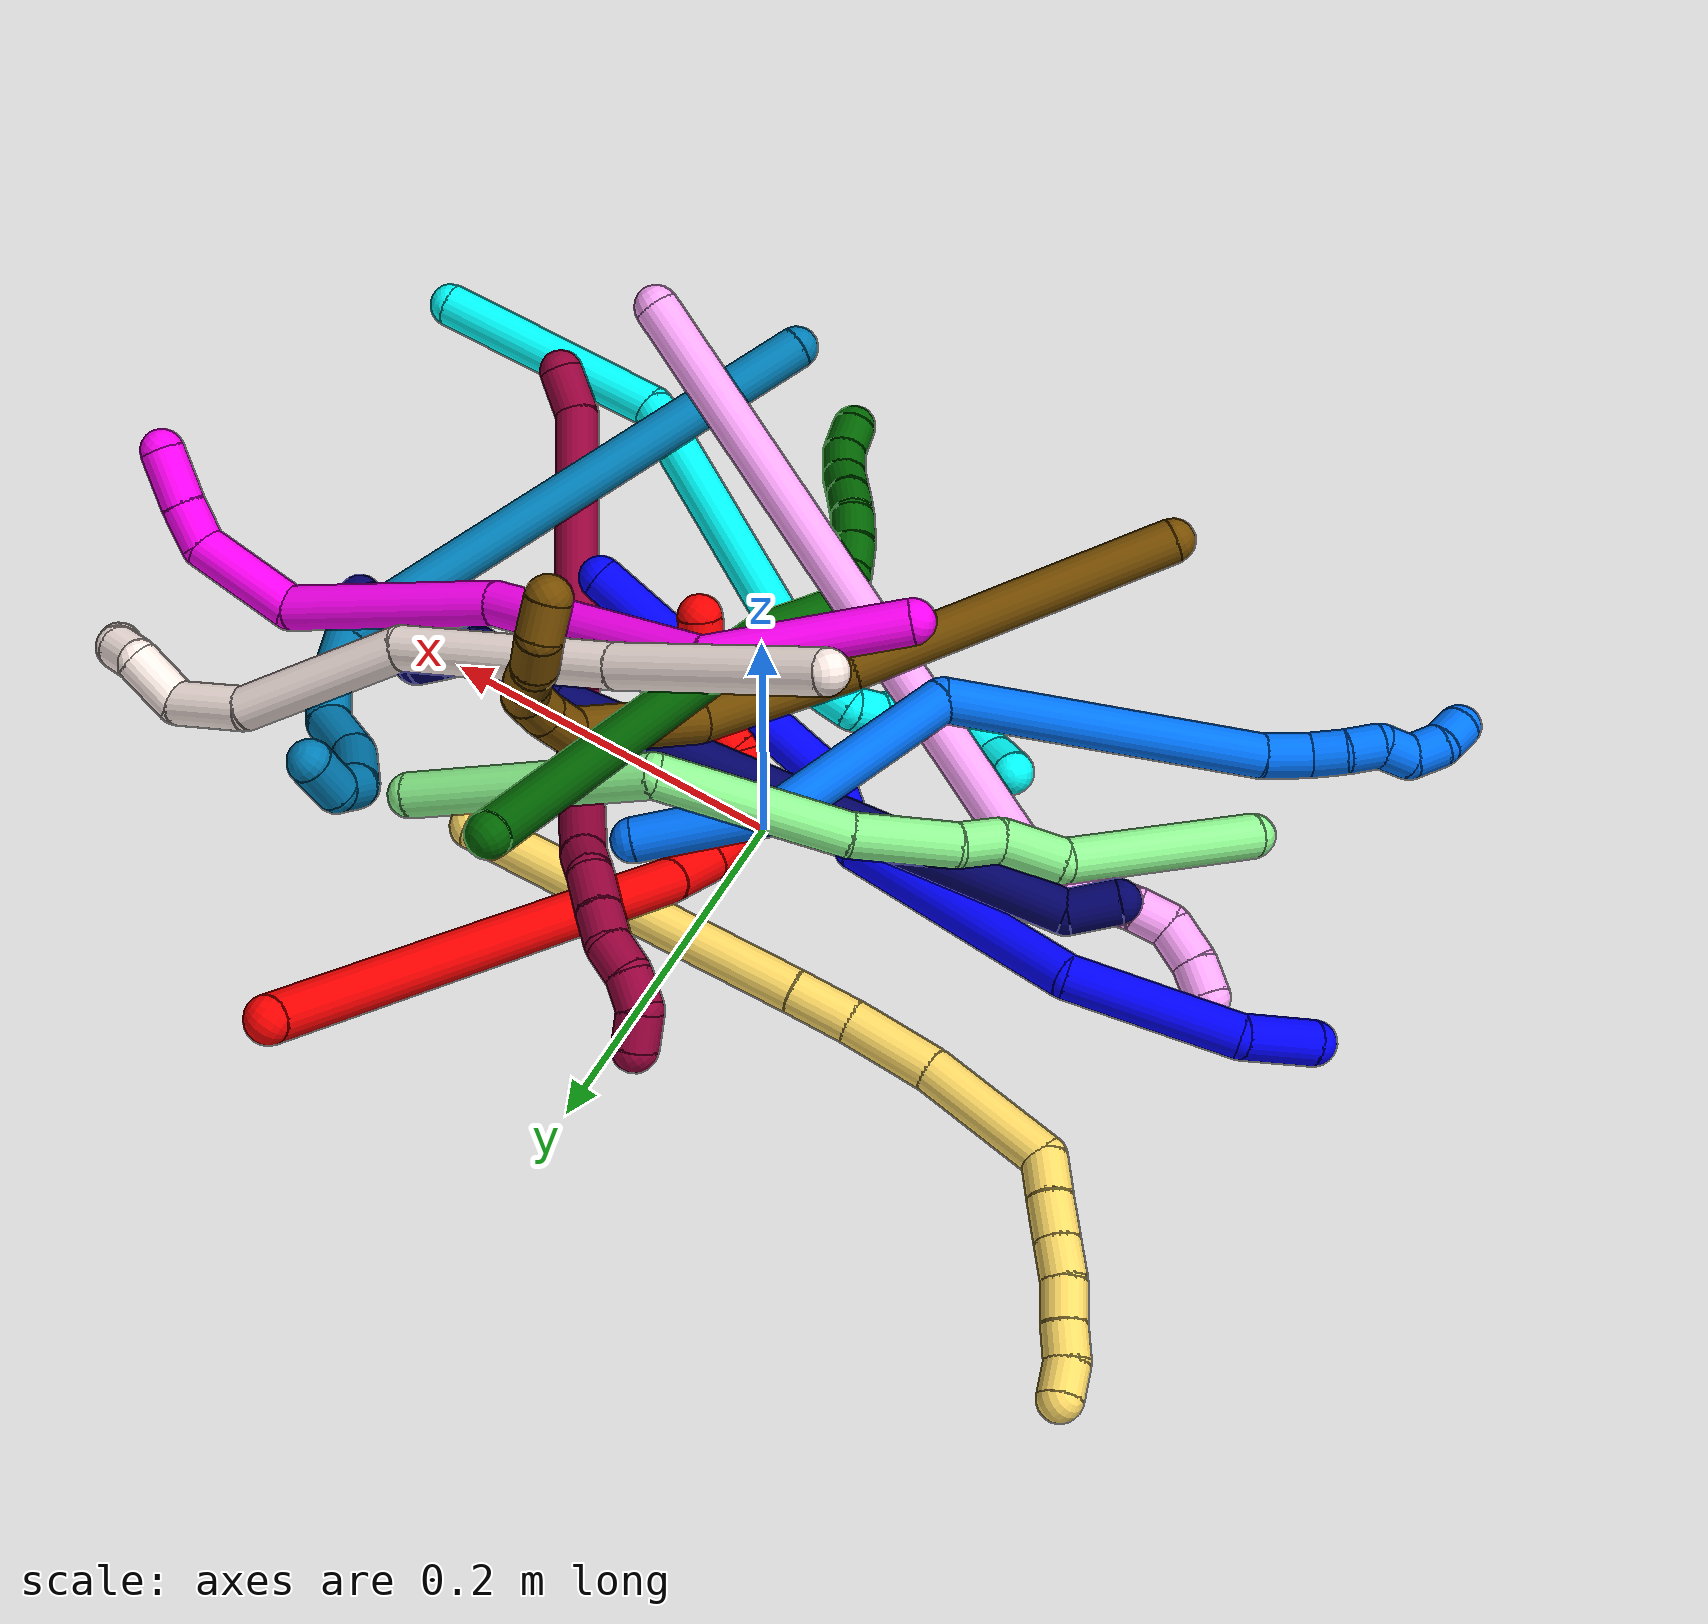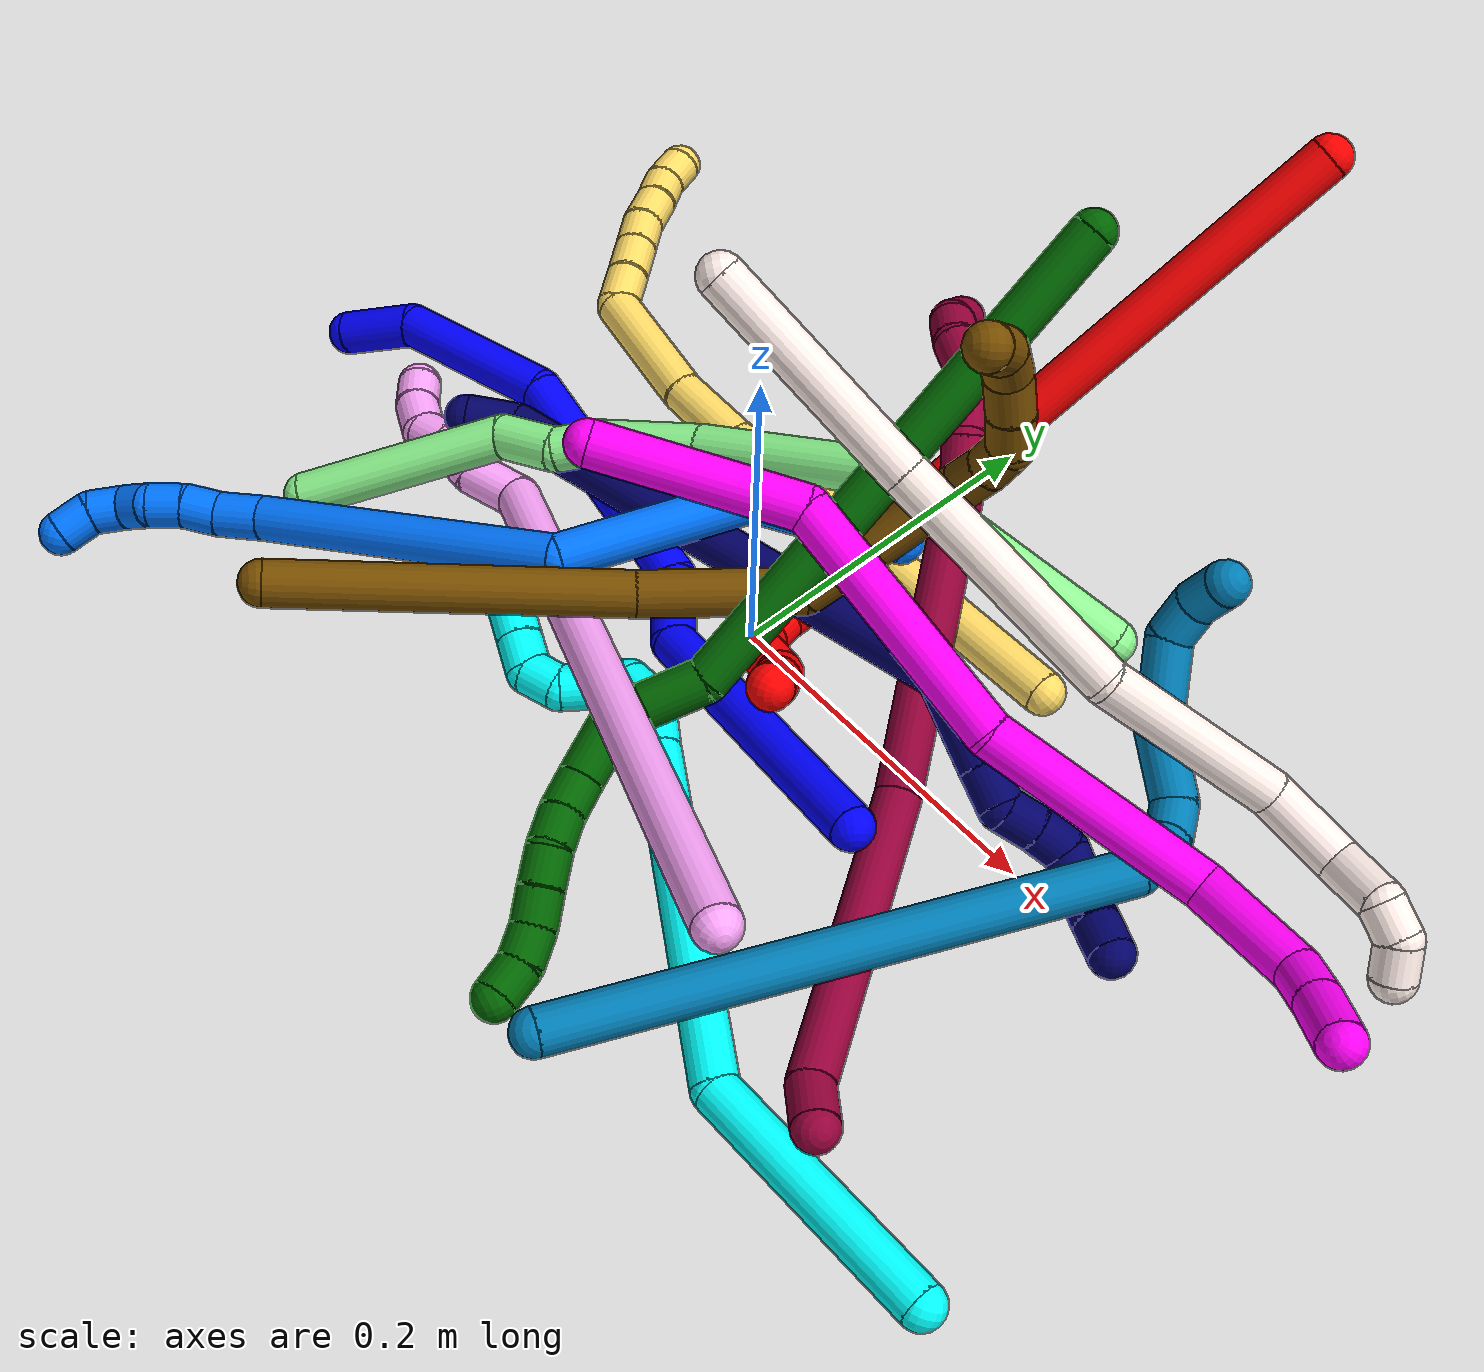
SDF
<sdf version="1.7">
 <world name="default">
  <plugin name="TubeGeneratorPlugin" filename="libtube_generator_plugin.so"/>
  <model name="photoneo_s_sensor">
   <static>1</static>
   <pose>0 0 2 1.57079 1.57079 3.14159</pose>
   <link name="link">
    <inertial><mass>0.1</mass></inertial>
    <sensor name="sensor" type="depth">
     <update_rate>30</update_rate>
     <camera>
      <horizontal_fov>1.22</horizontal_fov>
      <image><width>1920</width><height>1200</height><format>B8G8R8</format></image>
      <clip><near>0.1</near><far>4</far></clip>
      <depth_camera><output>points</output></depth_camera>
     </camera>
     <plugin name="camera_plugin" filename="libgazebo_ros_depth_camera.so">
      <baseline>0.2</baseline>
      <alwaysOn>1</alwaysOn>
      <updateRate>0.0</updateRate>
      <cameraName>camera_ir</cameraName>
      <imageTopicName>/camera/color/image_raw</imageTopicName>
      <cameraInfoTopicName>/camera/color/camera_info</cameraInfoTopicName>
      <depthImageTopicName>/camera/depth/image_raw</depthImageTopicName>
      <depthImageCameraInfoTopicName>/camera/depth/camera_info</depthImageCameraInfoTopicName>
      <pointCloudTopicName>/camera/depth/points</pointCloudTopicName>
      <frameName>fr_optical</frameName>
      <pointCloudCutoff>0.1</pointCloudCutoff>
      <pointCloudCutoffMax>2.0</pointCloudCutoffMax>
      <distortionK1>0</distortionK1>
      <distortionK2>0</distortionK2>
      <distortionK3>0</distortionK3>
      <distortionT1>0</distortionT1>
      <distortionT2>0</distortionT2>
      <CxPrime>0</CxPrime>
      <Cx>0</Cx>
      <Cy>0</Cy>
      <focalLength>0</focalLength>
      <hackBaseline>0</hackBaseline>
     </plugin>
    </sensor>
   </link>
  </model>
  <gravity>0 0 -9.8</gravity>
  <magnetic_field>6e-06 2.3e-05 -4.2e-05</magnetic_field>
  <atmosphere type="adiabatic"/>
  <physics name="default_physics" default="0" type="ode">
   <max_step_size>0.003</max_step_size>
   <real_time_factor>1</real_time_factor>
   <real_time_update_rate>1000</real_time_update_rate>
   <max_contacts>10000</max_contacts>
   <ode>
    <solver>
     <type>quick</type>
     <iters>100</iters>
     <sor>1.3</sor>
     <use_dynamic_moi_rescaling>0</use_dynamic_moi_rescaling>
    </solver>
    <constraints>
     <contact_max_correcting_vel>0</contact_max_correcting_vel>
     <contact_surface_layer>0.001</contact_surface_layer>
     <cfm>0</cfm>
     <erp>0.2</erp>
    </constraints>
   </ode>
  </physics>
  <scene><ambient>0.4 0.4 0.4 1</ambient><background>0.7 0.7 0.7 1</background><shadows>0</shadows></scene>
  <audio><device>default</device></audio>
  <spherical_coordinates>
   <surface_model>EARTH_WGS84</surface_model>
   <latitude_deg>0</latitude_deg>
   <longitude_deg>0</longitude_deg>
   <elevation>0</elevation>
   <heading_deg>0</heading_deg>
  </spherical_coordinates>
  <model name="bin">
   <static>1</static>
   <link name="bottom">
    <collision name="collision-bottom">
     <pose>0 0 -0.01 0 -0 0</pose>
     <geometry><box><size>0.8 0.6 0.02</size></box></geometry>
     <surface>
      <friction><ode><mu>100</mu><mu2>100</mu2></ode></friction>
      <contact><collide_bitmask>65535</collide_bitmask></contact>
     </surface>
    </collision>
   </link>
   <link name="west_wall">
    <collision name="collision-west_wall">
     <pose>-0.41 0 0.1 0 -0 0</pose>
     <geometry><box><size>0.02 0.6 0.2</size></box></geometry>
     <surface>
      <friction><ode><mu>100</mu><mu2>100</mu2></ode></friction>
      <contact><collide_bitmask>65535</collide_bitmask></contact>
     </surface>
    </collision>
   </link>
   <link name="east_wall">
    <collision name="collision-east_wall">
     <pose>0.41 0 0.1 0 -0 0</pose>
     <geometry><box><size>0.02 0.6 0.2</size></box></geometry>
     <surface>
      <friction><ode><mu>100</mu><mu2>100</mu2></ode></friction>
      <contact><collide_bitmask>65535</collide_bitmask></contact>
     </surface>
    </collision>
   </link>
   <link name="south_wall">
    <collision name="collision-south_wall">
     <pose>0 -0.31 0.1 0 -0 0</pose>
     <geometry><box><size>0.8 0.02 0.2</size></box></geometry>
     <surface>
      <friction><ode><mu>100</mu><mu2>100</mu2></ode></friction>
      <contact><collide_bitmask>65535</collide_bitmask></contact>
     </surface>
    </collision>
   </link>
   <link name="north_wall">
    <collision name="collision-north_wall">
     <pose>0 0.31 0.1 0 -0 0</pose>
     <geometry><box><size>0.8 0.02 0.2</size></box></geometry>
     <surface>
      <friction><ode><mu>100</mu><mu2>100</mu2></ode></friction>
      <contact><collide_bitmask>65535</collide_bitmask></contact>
     </surface>
    </collision>
   </link>
  </model>
  <model name="1">
   <static>0</static>
   <link name="1">
    <collision name="collision-cylinder-e_1_1_4">
     <pose>0.020949 -0.003981 0.004871 0.685206 1.27907 0.518649</pose>
     <geometry><cylinder><radius>0.0125</radius><length>0.043746</length></cylinder></geometry>
     <surface>
      <friction><ode><mu>1.16</mu><mu2>1.16</mu2><slip1>0</slip1><slip2>0</slip2></ode></friction>
      <contact><ode><kp>1e+06</kp><kd>1</kd><max_vel>0</max_vel><min_depth>0.001</min_depth></ode></contact>
     </surface>
    </collision>
    <visual name="visual-cylinder-e_1_1_4">
     <pose>0.020949 -0.003981 0.004871 0.685206 1.27907 0.518649</pose>
     <geometry><cylinder><radius>0.0125</radius><length>0.043746</length></cylinder></geometry>
     <material><ambient>0 0 1 1</ambient></material>
    </visual>
    <collision name="collision-cylinder-e_2_4_5">
     <pose>0.076763 -0.019196 0.041584 0.339181 0.801427 0.144829</pose>
     <geometry><cylinder><radius>0.0125</radius><length>0.097072</length></cylinder></geometry>
     <surface>
      <friction><ode><mu>1.16</mu><mu2>1.16</mu2><slip1>0</slip1><slip2>0</slip2></ode></friction>
      <contact><ode><kp>1e+06</kp><kd>1</kd><max_vel>0</max_vel><min_depth>0.001</min_depth></ode></contact>
     </surface>
    </collision>
    <visual name="visual-cylinder-e_2_4_5">
     <pose>0.076763 -0.019196 0.041584 0.339181 0.801427 0.144829</pose>
     <geometry><cylinder><radius>0.0125</radius><length>0.097072</length></cylinder></geometry>
     <material><ambient>0 0 1 1</ambient></material>
    </visual>
    <collision name="collision-cylinder-e_3_5_6">
     <pose>0.138997 -0.045238 0.138011 0.225371 0.391686 0.044893</pose>
     <geometry><cylinder><radius>0.0125</radius><length>0.143382</length></cylinder></geometry>
     <surface>
      <friction><ode><mu>1.16</mu><mu2>1.16</mu2><slip1>0</slip1><slip2>0</slip2></ode></friction>
      <contact><ode><kp>1e+06</kp><kd>1</kd><max_vel>0</max_vel><min_depth>0.001</min_depth></ode></contact>
     </surface>
    </collision>
    <visual name="visual-cylinder-e_3_5_6">
     <pose>0.138997 -0.045238 0.138011 0.225371 0.391686 0.044893</pose>
     <geometry><cylinder><radius>0.0125</radius><length>0.143382</length></cylinder></geometry>
     <material><ambient>0 0 1 1</ambient></material>
    </visual>
    <collision name="collision-cylinder-e_4_6_7">
     <pose>0.167414 -0.053848 0.224101 -0.280596 0.046857 -0.006619</pose>
     <geometry><cylinder><radius>0.0125</radius><length>0.044808</length></cylinder></geometry>
     <surface>
      <friction><ode><mu>1.16</mu><mu2>1.16</mu2><slip1>0</slip1><slip2>0</slip2></ode></friction>
      <contact><ode><kp>1e+06</kp><kd>1</kd><max_vel>0</max_vel><min_depth>0.001</min_depth></ode></contact>
     </surface>
    </collision>
    <visual name="visual-cylinder-e_4_6_7">
     <pose>0.167414 -0.053848 0.224101 -0.280596 0.046857 -0.006619</pose>
     <geometry><cylinder><radius>0.0125</radius><length>0.044808</length></cylinder></geometry>
     <material><ambient>0 0 1 1</ambient></material>
    </visual>
    <collision name="collision-cylinder-e_5_7_2">
     <pose>0.218235 -0.039325 0.31462 -0.120048 0.621376 -0.038587</pose>
     <geometry><cylinder><radius>0.0125</radius><length>0.170992</length></cylinder></geometry>
     <surface>
      <friction><ode><mu>1.16</mu><mu2>1.16</mu2><slip1>0</slip1><slip2>0</slip2></ode></friction>
      <contact><ode><kp>1e+06</kp><kd>1</kd><max_vel>0</max_vel><min_depth>0.001</min_depth></ode></contact>
     </surface>
    </collision>
    <visual name="visual-cylinder-e_5_7_2">
     <pose>0.218235 -0.039325 0.31462 -0.120048 0.621376 -0.038587</pose>
     <geometry><cylinder><radius>0.0125</radius><length>0.170992</length></cylinder></geometry>
     <material><ambient>0 0 1 1</ambient></material>
    </visual>
    <collision name="collision-sphere-2">
     <pose>0.268007 -0.031 0.383635 0 -0 0</pose>
     <geometry><sphere><radius>0.0125</radius></sphere></geometry>
     <surface>
      <friction><ode><mu>1.16</mu><mu2>1.16</mu2><slip1>0</slip1><slip2>0</slip2></ode></friction>
      <contact><ode><kp>1e+06</kp><kd>1</kd><max_vel>0</max_vel><min_depth>0.001</min_depth></ode></contact>
     </surface>
    </collision>
    <visual name="visual-sphere-2">
     <pose>0.268007 -0.031 0.383635 0 -0 0</pose>
     <geometry><sphere><radius>0.0125</radius></sphere></geometry>
     <material><ambient>0 0 1 1</ambient></material>
    </visual>
    <collision name="collision-sphere-7">
     <pose>0.168463 -0.04765 0.245606 0 -0 0</pose>
     <geometry><sphere><radius>0.0125</radius></sphere></geometry>
     <surface>
      <friction><ode><mu>1.16</mu><mu2>1.16</mu2><slip1>0</slip1><slip2>0</slip2></ode></friction>
      <contact><ode><kp>1e+06</kp><kd>1</kd><max_vel>0</max_vel><min_depth>0.001</min_depth></ode></contact>
     </surface>
    </collision>
    <visual name="visual-sphere-7">
     <pose>0.168463 -0.04765 0.245606 0 -0 0</pose>
     <geometry><sphere><radius>0.0125</radius></sphere></geometry>
     <material><ambient>0 0 1 1</ambient></material>
    </visual>
    <collision name="collision-sphere-6">
     <pose>0.166365 -0.060045 0.202597 0 -0 0</pose>
     <geometry><sphere><radius>0.0125</radius></sphere></geometry>
     <surface>
      <friction><ode><mu>1.16</mu><mu2>1.16</mu2><slip1>0</slip1><slip2>0</slip2></ode></friction>
      <contact><ode><kp>1e+06</kp><kd>1</kd><max_vel>0</max_vel><min_depth>0.001</min_depth></ode></contact>
     </surface>
    </collision>
    <visual name="visual-sphere-6">
     <pose>0.166365 -0.060045 0.202597 0 -0 0</pose>
     <geometry><sphere><radius>0.0125</radius></sphere></geometry>
     <material><ambient>0 0 1 1</ambient></material>
    </visual>
    <collision name="collision-sphere-5">
     <pose>0.111629 -0.030431 0.073425 0 -0 0</pose>
     <geometry><sphere><radius>0.0125</radius></sphere></geometry>
     <surface>
      <friction><ode><mu>1.16</mu><mu2>1.16</mu2><slip1>0</slip1><slip2>0</slip2></ode></friction>
      <contact><ode><kp>1e+06</kp><kd>1</kd><max_vel>0</max_vel><min_depth>0.001</min_depth></ode></contact>
     </surface>
    </collision>
    <visual name="visual-sphere-5">
     <pose>0.111629 -0.030431 0.073425 0 -0 0</pose>
     <geometry><sphere><radius>0.0125</radius></sphere></geometry>
     <material><ambient>0 0 1 1</ambient></material>
    </visual>
    <collision name="collision-sphere-1">
     <geometry><sphere><radius>0.0125</radius></sphere></geometry>
     <surface>
      <friction><ode><mu>1.16</mu><mu2>1.16</mu2><slip1>0</slip1><slip2>0</slip2></ode></friction>
      <contact><ode><kp>1e+06</kp><kd>1</kd><max_vel>0</max_vel><min_depth>0.001</min_depth></ode></contact>
     </surface>
    </collision>
    <visual name="visual-sphere-1">
     <geometry><sphere><radius>0.0125</radius></sphere></geometry>
     <material><ambient>0 0 1 1</ambient></material>
    </visual>
    <collision name="collision-sphere-4">
     <pose>0.041898 -0.007962 0.009742 0 -0 0</pose>
     <geometry><sphere><radius>0.0125</radius></sphere></geometry>
     <surface>
      <friction><ode><mu>1.16</mu><mu2>1.16</mu2><slip1>0</slip1><slip2>0</slip2></ode></friction>
      <contact><ode><kp>1e+06</kp><kd>1</kd><max_vel>0</max_vel><min_depth>0.001</min_depth></ode></contact>
     </surface>
    </collision>
    <visual name="visual-sphere-4">
     <pose>0.041898 -0.007962 0.009742 0 -0 0</pose>
     <geometry><sphere><radius>0.0125</radius></sphere></geometry>
     <material><ambient>0 0 1 1</ambient></material>
    </visual>
    <inertial>
     <pose>0.146231 -0.035322 0.175754 0 -0 0</pose>
     <mass>0.5</mass>
     <inertia>
      <ixx>0.00067</ixx>
      <ixy>0</ixy>
      <ixz>0</ixz>
      <iyy>0.000765</iyy>
      <iyz>0</iyz>
      <izz>-0.00035</izz>
     </inertia>
    </inertial>
   </link>
   <pose>-0.320092 -0.036986 0.011367 1.87793 -0.620649 0.804136</pose>
  </model>
  <model name="2">
   <static>0</static>
   <link name="2">
    <collision name="collision-cylinder-e_1_1_4">
     <pose>-0.049286 -0.130496 -0.066776 2.04377 -0.324347 -0.522774</pose>
     <geometry><cylinder><radius>0.0125</radius><length>0.309305</length></cylinder></geometry>
     <surface>
      <friction><ode><mu>1.16</mu><mu2>1.16</mu2><slip1>0</slip1><slip2>0</slip2></ode></friction>
      <contact><ode><kp>1e+06</kp><kd>1</kd><max_vel>0</max_vel><min_depth>0.001</min_depth></ode></contact>
     </surface>
    </collision>
    <visual name="visual-cylinder-e_1_1_4">
     <pose>-0.049286 -0.130496 -0.066776 2.04377 -0.324347 -0.522774</pose>
     <geometry><cylinder><radius>0.0125</radius><length>0.309305</length></cylinder></geometry>
     <material><ambient>1 0 0 1</ambient></material>
    </visual>
    <collision name="collision-cylinder-e_2_4_5">
     <pose>-0.104956 -0.277418 -0.139903 1.93978 -0.347762 -0.501716</pose>
     <geometry><cylinder><radius>0.0125</radius><length>0.037465</length></cylinder></geometry>
     <surface>
      <friction><ode><mu>1.16</mu><mu2>1.16</mu2><slip1>0</slip1><slip2>0</slip2></ode></friction>
      <contact><ode><kp>1e+06</kp><kd>1</kd><max_vel>0</max_vel><min_depth>0.001</min_depth></ode></contact>
     </surface>
    </collision>
    <visual name="visual-cylinder-e_2_4_5">
     <pose>-0.104956 -0.277418 -0.139903 1.93978 -0.347762 -0.501716</pose>
     <geometry><cylinder><radius>0.0125</radius><length>0.037465</length></cylinder></geometry>
     <material><ambient>1 0 0 1</ambient></material>
    </visual>
    <collision name="collision-cylinder-e_3_5_6">
     <pose>-0.120292 -0.303394 -0.148806 1.83178 -0.735899 -0.930455</pose>
     <geometry><cylinder><radius>0.0125</radius><length>0.026674</length></cylinder></geometry>
     <surface>
      <friction><ode><mu>1.16</mu><mu2>1.16</mu2><slip1>0</slip1><slip2>0</slip2></ode></friction>
      <contact><ode><kp>1e+06</kp><kd>1</kd><max_vel>0</max_vel><min_depth>0.001</min_depth></ode></contact>
     </surface>
    </collision>
    <visual name="visual-cylinder-e_3_5_6">
     <pose>-0.120292 -0.303394 -0.148806 1.83178 -0.735899 -0.930455</pose>
     <geometry><cylinder><radius>0.0125</radius><length>0.026674</length></cylinder></geometry>
     <material><ambient>1 0 0 1</ambient></material>
    </visual>
    <collision name="collision-cylinder-e_4_6_7">
     <pose>-0.139786 -0.31722 -0.145979 0.671642 -0.993217 -0.373879</pose>
     <geometry><cylinder><radius>0.0125</radius><length>0.025164</length></cylinder></geometry>
     <surface>
      <friction><ode><mu>1.16</mu><mu2>1.16</mu2><slip1>0</slip1><slip2>0</slip2></ode></friction>
      <contact><ode><kp>1e+06</kp><kd>1</kd><max_vel>0</max_vel><min_depth>0.001</min_depth></ode></contact>
     </surface>
    </collision>
    <visual name="visual-cylinder-e_4_6_7">
     <pose>-0.139786 -0.31722 -0.145979 0.671642 -0.993217 -0.373879</pose>
     <geometry><cylinder><radius>0.0125</radius><length>0.025164</length></cylinder></geometry>
     <material><ambient>1 0 0 1</ambient></material>
    </visual>
    <collision name="collision-cylinder-e_5_7_8">
     <pose>-0.157018 -0.322874 -0.132696 0.172761 -0.695018 -0.062711</pose>
     <geometry><cylinder><radius>0.0125</radius><length>0.020897</length></cylinder></geometry>
     <surface>
      <friction><ode><mu>1.16</mu><mu2>1.16</mu2><slip1>0</slip1><slip2>0</slip2></ode></friction>
      <contact><ode><kp>1e+06</kp><kd>1</kd><max_vel>0</max_vel><min_depth>0.001</min_depth></ode></contact>
     </surface>
    </collision>
    <visual name="visual-cylinder-e_5_7_8">
     <pose>-0.157018 -0.322874 -0.132696 0.172761 -0.695018 -0.062711</pose>
     <geometry><cylinder><radius>0.0125</radius><length>0.020897</length></cylinder></geometry>
     <material><ambient>1 0 0 1</ambient></material>
    </visual>
    <collision name="collision-cylinder-e_6_8_9">
     <pose>-0.165735 -0.326116 -0.11493 0.186601 -0.199185 -0.0187</pose>
     <geometry><cylinder><radius>0.0125</radius><length>0.020474</length></cylinder></geometry>
     <surface>
      <friction><ode><mu>1.16</mu><mu2>1.16</mu2><slip1>0</slip1><slip2>0</slip2></ode></friction>
      <contact><ode><kp>1e+06</kp><kd>1</kd><max_vel>0</max_vel><min_depth>0.001</min_depth></ode></contact>
     </surface>
    </collision>
    <visual name="visual-cylinder-e_6_8_9">
     <pose>-0.165735 -0.326116 -0.11493 0.186601 -0.199185 -0.0187</pose>
     <geometry><cylinder><radius>0.0125</radius><length>0.020474</length></cylinder></geometry>
     <material><ambient>1 0 0 1</ambient></material>
    </visual>
    <collision name="collision-cylinder-e_7_9_10">
     <pose>-0.175137 -0.327476 -0.098332 -0.074273 -0.829245 0.032702</pose>
     <geometry><cylinder><radius>0.0125</radius><length>0.020006</length></cylinder></geometry>
     <surface>
      <friction><ode><mu>1.16</mu><mu2>1.16</mu2><slip1>0</slip1><slip2>0</slip2></ode></friction>
      <contact><ode><kp>1e+06</kp><kd>1</kd><max_vel>0</max_vel><min_depth>0.001</min_depth></ode></contact>
     </surface>
    </collision>
    <visual name="visual-cylinder-e_7_9_10">
     <pose>-0.175137 -0.327476 -0.098332 -0.074273 -0.829245 0.032702</pose>
     <geometry><cylinder><radius>0.0125</radius><length>0.020006</length></cylinder></geometry>
     <material><ambient>1 0 0 1</ambient></material>
    </visual>
    <collision name="collision-cylinder-e_8_10_11">
     <pose>-0.189857 -0.326084 -0.084855 -0.131324 -0.823936 0.057452</pose>
     <geometry><cylinder><radius>0.0125</radius><length>0.020015</length></cylinder></geometry>
     <surface>
      <friction><ode><mu>1.16</mu><mu2>1.16</mu2><slip1>0</slip1><slip2>0</slip2></ode></friction>
      <contact><ode><kp>1e+06</kp><kd>1</kd><max_vel>0</max_vel><min_depth>0.001</min_depth></ode></contact>
     </surface>
    </collision>
    <visual name="visual-cylinder-e_8_10_11">
     <pose>-0.189857 -0.326084 -0.084855 -0.131324 -0.823936 0.057452</pose>
     <geometry><cylinder><radius>0.0125</radius><length>0.020015</length></cylinder></geometry>
     <material><ambient>1 0 0 1</ambient></material>
    </visual>
    <collision name="collision-cylinder-e_9_11_2">
     <pose>-0.204918 -0.32397 -0.071873 -0.193646 -0.881461 0.09156</pose>
     <geometry><cylinder><radius>0.0125</radius><length>0.020001</length></cylinder></geometry>
     <surface>
      <friction><ode><mu>1.16</mu><mu2>1.16</mu2><slip1>0</slip1><slip2>0</slip2></ode></friction>
      <contact><ode><kp>1e+06</kp><kd>1</kd><max_vel>0</max_vel><min_depth>0.001</min_depth></ode></contact>
     </surface>
    </collision>
    <visual name="visual-cylinder-e_9_11_2">
     <pose>-0.204918 -0.32397 -0.071873 -0.193646 -0.881461 0.09156</pose>
     <geometry><cylinder><radius>0.0125</radius><length>0.020001</length></cylinder></geometry>
     <material><ambient>1 0 0 1</ambient></material>
    </visual>
    <collision name="collision-sphere-2">
     <pose>-0.212635 -0.322746 -0.065631 0 -0 0</pose>
     <geometry><sphere><radius>0.0125</radius></sphere></geometry>
     <surface>
      <friction><ode><mu>1.16</mu><mu2>1.16</mu2><slip1>0</slip1><slip2>0</slip2></ode></friction>
      <contact><ode><kp>1e+06</kp><kd>1</kd><max_vel>0</max_vel><min_depth>0.001</min_depth></ode></contact>
     </surface>
    </collision>
    <visual name="visual-sphere-2">
     <pose>-0.212635 -0.322746 -0.065631 0 -0 0</pose>
     <geometry><sphere><radius>0.0125</radius></sphere></geometry>
     <material><ambient>1 0 0 1</ambient></material>
    </visual>
    <collision name="collision-sphere-11">
     <pose>-0.197201 -0.325194 -0.078115 0 -0 0</pose>
     <geometry><sphere><radius>0.0125</radius></sphere></geometry>
     <surface>
      <friction><ode><mu>1.16</mu><mu2>1.16</mu2><slip1>0</slip1><slip2>0</slip2></ode></friction>
      <contact><ode><kp>1e+06</kp><kd>1</kd><max_vel>0</max_vel><min_depth>0.001</min_depth></ode></contact>
     </surface>
    </collision>
    <visual name="visual-sphere-11">
     <pose>-0.197201 -0.325194 -0.078115 0 -0 0</pose>
     <geometry><sphere><radius>0.0125</radius></sphere></geometry>
     <material><ambient>1 0 0 1</ambient></material>
    </visual>
    <collision name="collision-sphere-10">
     <pose>-0.182514 -0.326974 -0.091595 0 -0 0</pose>
     <geometry><sphere><radius>0.0125</radius></sphere></geometry>
     <surface>
      <friction><ode><mu>1.16</mu><mu2>1.16</mu2><slip1>0</slip1><slip2>0</slip2></ode></friction>
      <contact><ode><kp>1e+06</kp><kd>1</kd><max_vel>0</max_vel><min_depth>0.001</min_depth></ode></contact>
     </surface>
    </collision>
    <visual name="visual-sphere-10">
     <pose>-0.182514 -0.326974 -0.091595 0 -0 0</pose>
     <geometry><sphere><radius>0.0125</radius></sphere></geometry>
     <material><ambient>1 0 0 1</ambient></material>
    </visual>
    <collision name="collision-sphere-9">
     <pose>-0.167761 -0.327977 -0.10507 0 -0 0</pose>
     <geometry><sphere><radius>0.0125</radius></sphere></geometry>
     <surface>
      <friction><ode><mu>1.16</mu><mu2>1.16</mu2><slip1>0</slip1><slip2>0</slip2></ode></friction>
      <contact><ode><kp>1e+06</kp><kd>1</kd><max_vel>0</max_vel><min_depth>0.001</min_depth></ode></contact>
     </surface>
    </collision>
    <visual name="visual-sphere-9">
     <pose>-0.167761 -0.327977 -0.10507 0 -0 0</pose>
     <geometry><sphere><radius>0.0125</radius></sphere></geometry>
     <material><ambient>1 0 0 1</ambient></material>
    </visual>
    <collision name="collision-sphere-4">
     <pose>-0.098572 -0.260992 -0.133552 0 -0 0</pose>
     <geometry><sphere><radius>0.0125</radius></sphere></geometry>
     <surface>
      <friction><ode><mu>1.16</mu><mu2>1.16</mu2><slip1>0</slip1><slip2>0</slip2></ode></friction>
      <contact><ode><kp>1e+06</kp><kd>1</kd><max_vel>0</max_vel><min_depth>0.001</min_depth></ode></contact>
     </surface>
    </collision>
    <visual name="visual-sphere-4">
     <pose>-0.098572 -0.260992 -0.133552 0 -0 0</pose>
     <geometry><sphere><radius>0.0125</radius></sphere></geometry>
     <material><ambient>1 0 0 1</ambient></material>
    </visual>
    <collision name="collision-sphere-1">
     <geometry><sphere><radius>0.0125</radius></sphere></geometry>
     <surface>
      <friction><ode><mu>1.16</mu><mu2>1.16</mu2><slip1>0</slip1><slip2>0</slip2></ode></friction>
      <contact><ode><kp>1e+06</kp><kd>1</kd><max_vel>0</max_vel><min_depth>0.001</min_depth></ode></contact>
     </surface>
    </collision>
    <visual name="visual-sphere-1">
     <geometry><sphere><radius>0.0125</radius></sphere></geometry>
     <material><ambient>1 0 0 1</ambient></material>
    </visual>
    <collision name="collision-sphere-8">
     <pose>-0.16371 -0.324254 -0.124791 0 -0 0</pose>
     <geometry><sphere><radius>0.0125</radius></sphere></geometry>
     <surface>
      <friction><ode><mu>1.16</mu><mu2>1.16</mu2><slip1>0</slip1><slip2>0</slip2></ode></friction>
      <contact><ode><kp>1e+06</kp><kd>1</kd><max_vel>0</max_vel><min_depth>0.001</min_depth></ode></contact>
     </surface>
    </collision>
    <visual name="visual-sphere-8">
     <pose>-0.16371 -0.324254 -0.124791 0 -0 0</pose>
     <geometry><sphere><radius>0.0125</radius></sphere></geometry>
     <material><ambient>1 0 0 1</ambient></material>
    </visual>
    <collision name="collision-sphere-5">
     <pose>-0.11134 -0.293843 -0.146255 0 -0 0</pose>
     <geometry><sphere><radius>0.0125</radius></sphere></geometry>
     <surface>
      <friction><ode><mu>1.16</mu><mu2>1.16</mu2><slip1>0</slip1><slip2>0</slip2></ode></friction>
      <contact><ode><kp>1e+06</kp><kd>1</kd><max_vel>0</max_vel><min_depth>0.001</min_depth></ode></contact>
     </surface>
    </collision>
    <visual name="visual-sphere-5">
     <pose>-0.11134 -0.293843 -0.146255 0 -0 0</pose>
     <geometry><sphere><radius>0.0125</radius></sphere></geometry>
     <material><ambient>1 0 0 1</ambient></material>
    </visual>
    <collision name="collision-sphere-6">
     <pose>-0.129245 -0.312945 -0.151357 0 -0 0</pose>
     <geometry><sphere><radius>0.0125</radius></sphere></geometry>
     <surface>
      <friction><ode><mu>1.16</mu><mu2>1.16</mu2><slip1>0</slip1><slip2>0</slip2></ode></friction>
      <contact><ode><kp>1e+06</kp><kd>1</kd><max_vel>0</max_vel><min_depth>0.001</min_depth></ode></contact>
     </surface>
    </collision>
    <visual name="visual-sphere-6">
     <pose>-0.129245 -0.312945 -0.151357 0 -0 0</pose>
     <geometry><sphere><radius>0.0125</radius></sphere></geometry>
     <material><ambient>1 0 0 1</ambient></material>
    </visual>
    <collision name="collision-sphere-7">
     <pose>-0.150327 -0.321495 -0.140601 0 -0 0</pose>
     <geometry><sphere><radius>0.0125</radius></sphere></geometry>
     <surface>
      <friction><ode><mu>1.16</mu><mu2>1.16</mu2><slip1>0</slip1><slip2>0</slip2></ode></friction>
      <contact><ode><kp>1e+06</kp><kd>1</kd><max_vel>0</max_vel><min_depth>0.001</min_depth></ode></contact>
     </surface>
    </collision>
    <visual name="visual-sphere-7">
     <pose>-0.150327 -0.321495 -0.140601 0 -0 0</pose>
     <geometry><sphere><radius>0.0125</radius></sphere></geometry>
     <material><ambient>1 0 0 1</ambient></material>
    </visual>
    <inertial>
     <pose>-0.087959 -0.199627 -0.087535 0 -0 0</pose>
     <mass>0.5</mass>
     <inertia>
      <ixx>0.000854</ixx>
      <ixy>0</ixy>
      <ixz>0</ixz>
      <iyy>-0.00182</iyy>
      <iyz>0</iyz>
      <izz>0.002894</izz>
     </inertia>
    </inertial>
   </link>
   <pose>0.085245 0.309718 0.221928 1.1243 0.611475 1.32199</pose>
  </model>
  <model name="3">
   <static>0</static>
   <link name="3">
    <collision name="collision-cylinder-e_1_1_4">
     <pose>-0.062421 -0.028847 0.012825 1.15245 -1.10255 -0.760203</pose>
     <geometry><cylinder><radius>0.0125</radius><length>0.139901</length></cylinder></geometry>
     <surface>
      <friction><ode><mu>1.16</mu><mu2>1.16</mu2><slip1>0</slip1><slip2>0</slip2></ode></friction>
      <contact><ode><kp>1e+06</kp><kd>1</kd><max_vel>0</max_vel><min_depth>0.001</min_depth></ode></contact>
     </surface>
    </collision>
    <visual name="visual-cylinder-e_1_1_4">
     <pose>-0.062421 -0.028847 0.012825 1.15245 -1.10255 -0.760203</pose>
     <geometry><cylinder><radius>0.0125</radius><length>0.139901</length></cylinder></geometry>
     <material><ambient>0.003922 1 0.996078 1</ambient></material>
    </visual>
    <collision name="collision-cylinder-e_2_4_5">
     <pose>-0.207688 -0.055006 0.076305 -0.053031 -1.02139 0.029716</pose>
     <geometry><cylinder><radius>0.0125</radius><length>0.194284</length></cylinder></geometry>
     <surface>
      <friction><ode><mu>1.16</mu><mu2>1.16</mu2><slip1>0</slip1><slip2>0</slip2></ode></friction>
      <contact><ode><kp>1e+06</kp><kd>1</kd><max_vel>0</max_vel><min_depth>0.001</min_depth></ode></contact>
     </surface>
    </collision>
    <visual name="visual-cylinder-e_2_4_5">
     <pose>-0.207688 -0.055006 0.076305 -0.053031 -1.02139 0.029716</pose>
     <geometry><cylinder><radius>0.0125</radius><length>0.194284</length></cylinder></geometry>
     <material><ambient>0.003922 1 0.996078 1</ambient></material>
    </visual>
    <collision name="collision-cylinder-e_3_5_6">
     <pose>-0.299492 -0.053366 0.135562 0.121323 -0.801953 -0.051486</pose>
     <geometry><cylinder><radius>0.0125</radius><length>0.024928</length></cylinder></geometry>
     <surface>
      <friction><ode><mu>1.16</mu><mu2>1.16</mu2><slip1>0</slip1><slip2>0</slip2></ode></friction>
      <contact><ode><kp>1e+06</kp><kd>1</kd><max_vel>0</max_vel><min_depth>0.001</min_depth></ode></contact>
     </surface>
    </collision>
    <visual name="visual-cylinder-e_3_5_6">
     <pose>-0.299492 -0.053366 0.135562 0.121323 -0.801953 -0.051486</pose>
     <geometry><cylinder><radius>0.0125</radius><length>0.024928</length></cylinder></geometry>
     <material><ambient>0.003922 1 0.996078 1</ambient></material>
    </visual>
    <collision name="collision-cylinder-e_4_6_7">
     <pose>-0.318025 -0.057337 0.145387 1.17469 -1.25138 -0.89667</pose>
     <geometry><cylinder><radius>0.0125</radius><length>0.020171</length></cylinder></geometry>
     <surface>
      <friction><ode><mu>1.16</mu><mu2>1.16</mu2><slip1>0</slip1><slip2>0</slip2></ode></friction>
      <contact><ode><kp>1e+06</kp><kd>1</kd><max_vel>0</max_vel><min_depth>0.001</min_depth></ode></contact>
     </surface>
    </collision>
    <visual name="visual-cylinder-e_4_6_7">
     <pose>-0.318025 -0.057337 0.145387 1.17469 -1.25138 -0.89667</pose>
     <geometry><cylinder><radius>0.0125</radius><length>0.020171</length></cylinder></geometry>
     <material><ambient>0.003922 1 0.996078 1</ambient></material>
    </visual>
    <collision name="collision-cylinder-e_5_7_8">
     <pose>-0.335168 -0.064282 0.141112 2.50968 -0.837928 -1.87512</pose>
     <geometry><cylinder><radius>0.0125</radius><length>0.020364</length></cylinder></geometry>
     <surface>
      <friction><ode><mu>1.16</mu><mu2>1.16</mu2><slip1>0</slip1><slip2>0</slip2></ode></friction>
      <contact><ode><kp>1e+06</kp><kd>1</kd><max_vel>0</max_vel><min_depth>0.001</min_depth></ode></contact>
     </surface>
    </collision>
    <visual name="visual-cylinder-e_5_7_8">
     <pose>-0.335168 -0.064282 0.141112 2.50968 -0.837928 -1.87512</pose>
     <geometry><cylinder><radius>0.0125</radius><length>0.020364</length></cylinder></geometry>
     <material><ambient>0.003922 1 0.996078 1</ambient></material>
    </visual>
    <collision name="collision-cylinder-e_6_8_9">
     <pose>-0.346434 -0.076746 0.131467 2.02764 -0.374667 -0.590956</pose>
     <geometry><cylinder><radius>0.0125</radius><length>0.020211</length></cylinder></geometry>
     <surface>
      <friction><ode><mu>1.16</mu><mu2>1.16</mu2><slip1>0</slip1><slip2>0</slip2></ode></friction>
      <contact><ode><kp>1e+06</kp><kd>1</kd><max_vel>0</max_vel><min_depth>0.001</min_depth></ode></contact>
     </surface>
    </collision>
    <visual name="visual-cylinder-e_6_8_9">
     <pose>-0.346434 -0.076746 0.131467 2.02764 -0.374667 -0.590956</pose>
     <geometry><cylinder><radius>0.0125</radius><length>0.020211</length></cylinder></geometry>
     <material><ambient>0.003922 1 0.996078 1</ambient></material>
    </visual>
    <collision name="collision-cylinder-e_7_9_10">
     <pose>-0.358281 -0.091019 0.127187 1.59338 -0.949415 -0.967899</pose>
     <geometry><cylinder><radius>0.0125</radius><length>0.020043</length></cylinder></geometry>
     <surface>
      <friction><ode><mu>1.16</mu><mu2>1.16</mu2><slip1>0</slip1><slip2>0</slip2></ode></friction>
      <contact><ode><kp>1e+06</kp><kd>1</kd><max_vel>0</max_vel><min_depth>0.001</min_depth></ode></contact>
     </surface>
    </collision>
    <visual name="visual-cylinder-e_7_9_10">
     <pose>-0.358281 -0.091019 0.127187 1.59338 -0.949415 -0.967899</pose>
     <geometry><cylinder><radius>0.0125</radius><length>0.020043</length></cylinder></geometry>
     <material><ambient>0.003922 1 0.996078 1</ambient></material>
    </visual>
    <collision name="collision-cylinder-e_8_10_11">
     <pose>-0.374458 -0.09866 0.132789 0.305615 -0.92804 -0.153848</pose>
     <geometry><cylinder><radius>0.0125</radius><length>0.02006</length></cylinder></geometry>
     <surface>
      <friction><ode><mu>1.16</mu><mu2>1.16</mu2><slip1>0</slip1><slip2>0</slip2></ode></friction>
      <contact><ode><kp>1e+06</kp><kd>1</kd><max_vel>0</max_vel><min_depth>0.001</min_depth></ode></contact>
     </surface>
    </collision>
    <visual name="visual-cylinder-e_8_10_11">
     <pose>-0.374458 -0.09866 0.132789 0.305615 -0.92804 -0.153848</pose>
     <geometry><cylinder><radius>0.0125</radius><length>0.02006</length></cylinder></geometry>
     <material><ambient>0.003922 1 0.996078 1</ambient></material>
    </visual>
    <collision name="collision-cylinder-e_9_11_12">
     <pose>-0.390473 -0.10235 0.144262 0.316706 -0.923266 -0.158554</pose>
     <geometry><cylinder><radius>0.0125</radius><length>0.020027</length></cylinder></geometry>
     <surface>
      <friction><ode><mu>1.16</mu><mu2>1.16</mu2><slip1>0</slip1><slip2>0</slip2></ode></friction>
      <contact><ode><kp>1e+06</kp><kd>1</kd><max_vel>0</max_vel><min_depth>0.001</min_depth></ode></contact>
     </surface>
    </collision>
    <visual name="visual-cylinder-e_9_11_12">
     <pose>-0.390473 -0.10235 0.144262 0.316706 -0.923266 -0.158554</pose>
     <geometry><cylinder><radius>0.0125</radius><length>0.020027</length></cylinder></geometry>
     <material><ambient>0.003922 1 0.996078 1</ambient></material>
    </visual>
    <collision name="collision-cylinder-e_10_12_2">
     <pose>-0.404326 -0.106809 0.157687 0.323623 -0.626433 -0.10564</pose>
     <geometry><cylinder><radius>0.0125</radius><length>0.02001</length></cylinder></geometry>
     <surface>
      <friction><ode><mu>1.16</mu><mu2>1.16</mu2><slip1>0</slip1><slip2>0</slip2></ode></friction>
      <contact><ode><kp>1e+06</kp><kd>1</kd><max_vel>0</max_vel><min_depth>0.001</min_depth></ode></contact>
     </surface>
    </collision>
    <visual name="visual-cylinder-e_10_12_2">
     <pose>-0.404326 -0.106809 0.157687 0.323623 -0.626433 -0.10564</pose>
     <geometry><cylinder><radius>0.0125</radius><length>0.02001</length></cylinder></geometry>
     <material><ambient>0.003922 1 0.996078 1</ambient></material>
    </visual>
    <collision name="collision-sphere-2">
     <pose>-0.410191 -0.109387 0.165372 0 -0 0</pose>
     <geometry><sphere><radius>0.0125</radius></sphere></geometry>
     <surface>
      <friction><ode><mu>1.16</mu><mu2>1.16</mu2><slip1>0</slip1><slip2>0</slip2></ode></friction>
      <contact><ode><kp>1e+06</kp><kd>1</kd><max_vel>0</max_vel><min_depth>0.001</min_depth></ode></contact>
     </surface>
    </collision>
    <visual name="visual-sphere-2">
     <pose>-0.410191 -0.109387 0.165372 0 -0 0</pose>
     <geometry><sphere><radius>0.0125</radius></sphere></geometry>
     <material><ambient>0.003922 1 0.996078 1</ambient></material>
    </visual>
    <collision name="collision-sphere-12">
     <pose>-0.39846 -0.104232 0.150002 0 -0 0</pose>
     <geometry><sphere><radius>0.0125</radius></sphere></geometry>
     <surface>
      <friction><ode><mu>1.16</mu><mu2>1.16</mu2><slip1>0</slip1><slip2>0</slip2></ode></friction>
      <contact><ode><kp>1e+06</kp><kd>1</kd><max_vel>0</max_vel><min_depth>0.001</min_depth></ode></contact>
     </surface>
    </collision>
    <visual name="visual-sphere-12">
     <pose>-0.39846 -0.104232 0.150002 0 -0 0</pose>
     <geometry><sphere><radius>0.0125</radius></sphere></geometry>
     <material><ambient>0.003922 1 0.996078 1</ambient></material>
    </visual>
    <collision name="collision-sphere-11">
     <pose>-0.382487 -0.100469 0.138522 0 -0 0</pose>
     <geometry><sphere><radius>0.0125</radius></sphere></geometry>
     <surface>
      <friction><ode><mu>1.16</mu><mu2>1.16</mu2><slip1>0</slip1><slip2>0</slip2></ode></friction>
      <contact><ode><kp>1e+06</kp><kd>1</kd><max_vel>0</max_vel><min_depth>0.001</min_depth></ode></contact>
     </surface>
    </collision>
    <visual name="visual-sphere-11">
     <pose>-0.382487 -0.100469 0.138522 0 -0 0</pose>
     <geometry><sphere><radius>0.0125</radius></sphere></geometry>
     <material><ambient>0.003922 1 0.996078 1</ambient></material>
    </visual>
    <collision name="collision-sphere-10">
     <pose>-0.366429 -0.096851 0.127055 0 -0 0</pose>
     <geometry><sphere><radius>0.0125</radius></sphere></geometry>
     <surface>
      <friction><ode><mu>1.16</mu><mu2>1.16</mu2><slip1>0</slip1><slip2>0</slip2></ode></friction>
      <contact><ode><kp>1e+06</kp><kd>1</kd><max_vel>0</max_vel><min_depth>0.001</min_depth></ode></contact>
     </surface>
    </collision>
    <visual name="visual-sphere-10">
     <pose>-0.366429 -0.096851 0.127055 0 -0 0</pose>
     <geometry><sphere><radius>0.0125</radius></sphere></geometry>
     <material><ambient>0.003922 1 0.996078 1</ambient></material>
    </visual>
    <collision name="collision-sphere-9">
     <pose>-0.350133 -0.085186 0.127318 0 -0 0</pose>
     <geometry><sphere><radius>0.0125</radius></sphere></geometry>
     <surface>
      <friction><ode><mu>1.16</mu><mu2>1.16</mu2><slip1>0</slip1><slip2>0</slip2></ode></friction>
      <contact><ode><kp>1e+06</kp><kd>1</kd><max_vel>0</max_vel><min_depth>0.001</min_depth></ode></contact>
     </surface>
    </collision>
    <visual name="visual-sphere-9">
     <pose>-0.350133 -0.085186 0.127318 0 -0 0</pose>
     <geometry><sphere><radius>0.0125</radius></sphere></geometry>
     <material><ambient>0.003922 1 0.996078 1</ambient></material>
    </visual>
    <collision name="collision-sphere-4">
     <pose>-0.124842 -0.057695 0.025651 0 -0 0</pose>
     <geometry><sphere><radius>0.0125</radius></sphere></geometry>
     <surface>
      <friction><ode><mu>1.16</mu><mu2>1.16</mu2><slip1>0</slip1><slip2>0</slip2></ode></friction>
      <contact><ode><kp>1e+06</kp><kd>1</kd><max_vel>0</max_vel><min_depth>0.001</min_depth></ode></contact>
     </surface>
    </collision>
    <visual name="visual-sphere-4">
     <pose>-0.124842 -0.057695 0.025651 0 -0 0</pose>
     <geometry><sphere><radius>0.0125</radius></sphere></geometry>
     <material><ambient>0.003922 1 0.996078 1</ambient></material>
    </visual>
    <collision name="collision-sphere-1">
     <geometry><sphere><radius>0.0125</radius></sphere></geometry>
     <surface>
      <friction><ode><mu>1.16</mu><mu2>1.16</mu2><slip1>0</slip1><slip2>0</slip2></ode></friction>
      <contact><ode><kp>1e+06</kp><kd>1</kd><max_vel>0</max_vel><min_depth>0.001</min_depth></ode></contact>
     </surface>
    </collision>
    <visual name="visual-sphere-1">
     <geometry><sphere><radius>0.0125</radius></sphere></geometry>
     <material><ambient>0.003922 1 0.996078 1</ambient></material>
    </visual>
    <collision name="collision-sphere-8">
     <pose>-0.342736 -0.068306 0.135615 0 -0 0</pose>
     <geometry><sphere><radius>0.0125</radius></sphere></geometry>
     <surface>
      <friction><ode><mu>1.16</mu><mu2>1.16</mu2><slip1>0</slip1><slip2>0</slip2></ode></friction>
      <contact><ode><kp>1e+06</kp><kd>1</kd><max_vel>0</max_vel><min_depth>0.001</min_depth></ode></contact>
     </surface>
    </collision>
    <visual name="visual-sphere-8">
     <pose>-0.342736 -0.068306 0.135615 0 -0 0</pose>
     <geometry><sphere><radius>0.0125</radius></sphere></geometry>
     <material><ambient>0.003922 1 0.996078 1</ambient></material>
    </visual>
    <collision name="collision-sphere-5">
     <pose>-0.290534 -0.052317 0.12696 0 -0 0</pose>
     <geometry><sphere><radius>0.0125</radius></sphere></geometry>
     <surface>
      <friction><ode><mu>1.16</mu><mu2>1.16</mu2><slip1>0</slip1><slip2>0</slip2></ode></friction>
      <contact><ode><kp>1e+06</kp><kd>1</kd><max_vel>0</max_vel><min_depth>0.001</min_depth></ode></contact>
     </surface>
    </collision>
    <visual name="visual-sphere-5">
     <pose>-0.290534 -0.052317 0.12696 0 -0 0</pose>
     <geometry><sphere><radius>0.0125</radius></sphere></geometry>
     <material><ambient>0.003922 1 0.996078 1</ambient></material>
    </visual>
    <collision name="collision-sphere-6">
     <pose>-0.30845 -0.054415 0.144165 0 -0 0</pose>
     <geometry><sphere><radius>0.0125</radius></sphere></geometry>
     <surface>
      <friction><ode><mu>1.16</mu><mu2>1.16</mu2><slip1>0</slip1><slip2>0</slip2></ode></friction>
      <contact><ode><kp>1e+06</kp><kd>1</kd><max_vel>0</max_vel><min_depth>0.001</min_depth></ode></contact>
     </surface>
    </collision>
    <visual name="visual-sphere-6">
     <pose>-0.30845 -0.054415 0.144165 0 -0 0</pose>
     <geometry><sphere><radius>0.0125</radius></sphere></geometry>
     <material><ambient>0.003922 1 0.996078 1</ambient></material>
    </visual>
    <collision name="collision-sphere-7">
     <pose>-0.3276 -0.060258 0.146608 0 -0 0</pose>
     <geometry><sphere><radius>0.0125</radius></sphere></geometry>
     <surface>
      <friction><ode><mu>1.16</mu><mu2>1.16</mu2><slip1>0</slip1><slip2>0</slip2></ode></friction>
      <contact><ode><kp>1e+06</kp><kd>1</kd><max_vel>0</max_vel><min_depth>0.001</min_depth></ode></contact>
     </surface>
    </collision>
    <visual name="visual-sphere-7">
     <pose>-0.3276 -0.060258 0.146608 0 -0 0</pose>
     <geometry><sphere><radius>0.0125</radius></sphere></geometry>
     <material><ambient>0.003922 1 0.996078 1</ambient></material>
    </visual>
    <inertial>
     <pose>-0.21479 -0.05612 0.079439 0 -0 0</pose>
     <mass>0.5</mass>
     <inertia>
      <ixx>0.000307</ixx>
      <ixy>0</ixy>
      <ixz>0</ixz>
      <iyy>0.000753</iyy>
      <iyz>0</iyz>
      <izz>0.000842</izz>
     </inertia>
    </inertial>
   </link>
   <pose>0.336557 -0.197663 0.012433 -0.631217 -0.41342 -0.224075</pose>
  </model>
  <model name="4">
   <static>0</static>
   <link name="4">
    <collision name="collision-cylinder-e_1_1_4">
     <pose>-0.001485 0.001238 -0.189655 -3.13506 -0.007828 1.75114</pose>
     <geometry><cylinder><radius>0.0125</radius><length>0.37933</length></cylinder></geometry>
     <surface>
      <friction><ode><mu>1.16</mu><mu2>1.16</mu2><slip1>0</slip1><slip2>0</slip2></ode></friction>
      <contact><ode><kp>1e+06</kp><kd>1</kd><max_vel>0</max_vel><min_depth>0.001</min_depth></ode></contact>
     </surface>
    </collision>
    <visual name="visual-cylinder-e_1_1_4">
     <pose>-0.001485 0.001238 -0.189655 -3.13506 -0.007828 1.75114</pose>
     <geometry><cylinder><radius>0.0125</radius><length>0.37933</length></cylinder></geometry>
     <material><ambient>1 0.65098 0.996078 1</ambient></material>
    </visual>
    <collision name="collision-cylinder-e_2_4_5">
     <pose>-0.009523 -0.005467 -0.392072 2.58484 -0.411118 -1.26057</pose>
     <geometry><cylinder><radius>0.0125</radius><length>0.032798</length></cylinder></geometry>
     <surface>
      <friction><ode><mu>1.16</mu><mu2>1.16</mu2><slip1>0</slip1><slip2>0</slip2></ode></friction>
      <contact><ode><kp>1e+06</kp><kd>1</kd><max_vel>0</max_vel><min_depth>0.001</min_depth></ode></contact>
     </surface>
    </collision>
    <visual name="visual-cylinder-e_2_4_5">
     <pose>-0.009523 -0.005467 -0.392072 2.58484 -0.411118 -1.26057</pose>
     <geometry><cylinder><radius>0.0125</radius><length>0.032798</length></cylinder></geometry>
     <material><ambient>1 0.65098 0.996078 1</ambient></material>
    </visual>
    <collision name="collision-cylinder-e_3_5_6">
     <pose>-0.023417 -0.015568 -0.413431 2.89573 -0.691695 -2.48094</pose>
     <geometry><cylinder><radius>0.0125</radius><length>0.023016</length></cylinder></geometry>
     <surface>
      <friction><ode><mu>1.16</mu><mu2>1.16</mu2><slip1>0</slip1><slip2>0</slip2></ode></friction>
      <contact><ode><kp>1e+06</kp><kd>1</kd><max_vel>0</max_vel><min_depth>0.001</min_depth></ode></contact>
     </surface>
    </collision>
    <visual name="visual-cylinder-e_3_5_6">
     <pose>-0.023417 -0.015568 -0.413431 2.89573 -0.691695 -2.48094</pose>
     <geometry><cylinder><radius>0.0125</radius><length>0.023016</length></cylinder></geometry>
     <material><ambient>1 0.65098 0.996078 1</ambient></material>
    </visual>
    <collision name="collision-cylinder-e_4_6_7">
     <pose>-0.033166 -0.022092 -0.430801 2.67971 -0.241033 -0.951196</pose>
     <geometry><cylinder><radius>0.0125</radius><length>0.020184</length></cylinder></geometry>
     <surface>
      <friction><ode><mu>1.16</mu><mu2>1.16</mu2><slip1>0</slip1><slip2>0</slip2></ode></friction>
      <contact><ode><kp>1e+06</kp><kd>1</kd><max_vel>0</max_vel><min_depth>0.001</min_depth></ode></contact>
     </surface>
    </collision>
    <visual name="visual-cylinder-e_4_6_7">
     <pose>-0.033166 -0.022092 -0.430801 2.67971 -0.241033 -0.951196</pose>
     <geometry><cylinder><radius>0.0125</radius><length>0.020184</length></cylinder></geometry>
     <material><ambient>1 0.65098 0.996078 1</ambient></material>
    </visual>
    <collision name="collision-cylinder-e_5_7_8">
     <pose>-0.037095 -0.025177 -0.45143 -3.03385 -0.126783 1.7332</pose>
     <geometry><cylinder><radius>0.0125</radius><length>0.024043</length></cylinder></geometry>
     <surface>
      <friction><ode><mu>1.16</mu><mu2>1.16</mu2><slip1>0</slip1><slip2>0</slip2></ode></friction>
      <contact><ode><kp>1e+06</kp><kd>1</kd><max_vel>0</max_vel><min_depth>0.001</min_depth></ode></contact>
     </surface>
    </collision>
    <visual name="visual-cylinder-e_5_7_8">
     <pose>-0.037095 -0.025177 -0.45143 -3.03385 -0.126783 1.7332</pose>
     <geometry><cylinder><radius>0.0125</radius><length>0.024043</length></cylinder></geometry>
     <material><ambient>1 0.65098 0.996078 1</ambient></material>
    </visual>
    <collision name="collision-cylinder-e_6_8_2">
     <pose>-0.038895 -0.020628 -0.473065 -2.81919 -0.027099 0.166275</pose>
     <geometry><cylinder><radius>0.0125</radius><length>0.02063</length></cylinder></geometry>
     <surface>
      <friction><ode><mu>1.16</mu><mu2>1.16</mu2><slip1>0</slip1><slip2>0</slip2></ode></friction>
      <contact><ode><kp>1e+06</kp><kd>1</kd><max_vel>0</max_vel><min_depth>0.001</min_depth></ode></contact>
     </surface>
    </collision>
    <visual name="visual-cylinder-e_6_8_2">
     <pose>-0.038895 -0.020628 -0.473065 -2.81919 -0.027099 0.166275</pose>
     <geometry><cylinder><radius>0.0125</radius><length>0.02063</length></cylinder></geometry>
     <material><ambient>1 0.65098 0.996078 1</ambient></material>
    </visual>
    <collision name="collision-sphere-2">
     <pose>-0.039174 -0.017361 -0.482845 0 -0 0</pose>
     <geometry><sphere><radius>0.0125</radius></sphere></geometry>
     <surface>
      <friction><ode><mu>1.16</mu><mu2>1.16</mu2><slip1>0</slip1><slip2>0</slip2></ode></friction>
      <contact><ode><kp>1e+06</kp><kd>1</kd><max_vel>0</max_vel><min_depth>0.001</min_depth></ode></contact>
     </surface>
    </collision>
    <visual name="visual-sphere-2">
     <pose>-0.039174 -0.017361 -0.482845 0 -0 0</pose>
     <geometry><sphere><radius>0.0125</radius></sphere></geometry>
     <material><ambient>1 0.65098 0.996078 1</ambient></material>
    </visual>
    <collision name="collision-sphere-4">
     <pose>-0.002969 0.002477 -0.37931 0 -0 0</pose>
     <geometry><sphere><radius>0.0125</radius></sphere></geometry>
     <surface>
      <friction><ode><mu>1.16</mu><mu2>1.16</mu2><slip1>0</slip1><slip2>0</slip2></ode></friction>
      <contact><ode><kp>1e+06</kp><kd>1</kd><max_vel>0</max_vel><min_depth>0.001</min_depth></ode></contact>
     </surface>
    </collision>
    <visual name="visual-sphere-4">
     <pose>-0.002969 0.002477 -0.37931 0 -0 0</pose>
     <geometry><sphere><radius>0.0125</radius></sphere></geometry>
     <material><ambient>1 0.65098 0.996078 1</ambient></material>
    </visual>
    <collision name="collision-sphere-1">
     <geometry><sphere><radius>0.0125</radius></sphere></geometry>
     <surface>
      <friction><ode><mu>1.16</mu><mu2>1.16</mu2><slip1>0</slip1><slip2>0</slip2></ode></friction>
      <contact><ode><kp>1e+06</kp><kd>1</kd><max_vel>0</max_vel><min_depth>0.001</min_depth></ode></contact>
     </surface>
    </collision>
    <visual name="visual-sphere-1">
     <geometry><sphere><radius>0.0125</radius></sphere></geometry>
     <material><ambient>1 0.65098 0.996078 1</ambient></material>
    </visual>
    <collision name="collision-sphere-8">
     <pose>-0.038615 -0.023895 -0.463285 0 -0 0</pose>
     <geometry><sphere><radius>0.0125</radius></sphere></geometry>
     <surface>
      <friction><ode><mu>1.16</mu><mu2>1.16</mu2><slip1>0</slip1><slip2>0</slip2></ode></friction>
      <contact><ode><kp>1e+06</kp><kd>1</kd><max_vel>0</max_vel><min_depth>0.001</min_depth></ode></contact>
     </surface>
    </collision>
    <visual name="visual-sphere-8">
     <pose>-0.038615 -0.023895 -0.463285 0 -0 0</pose>
     <geometry><sphere><radius>0.0125</radius></sphere></geometry>
     <material><ambient>1 0.65098 0.996078 1</ambient></material>
    </visual>
    <collision name="collision-sphere-5">
     <pose>-0.016077 -0.013411 -0.404834 0 -0 0</pose>
     <geometry><sphere><radius>0.0125</radius></sphere></geometry>
     <surface>
      <friction><ode><mu>1.16</mu><mu2>1.16</mu2><slip1>0</slip1><slip2>0</slip2></ode></friction>
      <contact><ode><kp>1e+06</kp><kd>1</kd><max_vel>0</max_vel><min_depth>0.001</min_depth></ode></contact>
     </surface>
    </collision>
    <visual name="visual-sphere-5">
     <pose>-0.016077 -0.013411 -0.404834 0 -0 0</pose>
     <geometry><sphere><radius>0.0125</radius></sphere></geometry>
     <material><ambient>1 0.65098 0.996078 1</ambient></material>
    </visual>
    <collision name="collision-sphere-6">
     <pose>-0.030757 -0.017725 -0.422027 0 -0 0</pose>
     <geometry><sphere><radius>0.0125</radius></sphere></geometry>
     <surface>
      <friction><ode><mu>1.16</mu><mu2>1.16</mu2><slip1>0</slip1><slip2>0</slip2></ode></friction>
      <contact><ode><kp>1e+06</kp><kd>1</kd><max_vel>0</max_vel><min_depth>0.001</min_depth></ode></contact>
     </surface>
    </collision>
    <visual name="visual-sphere-6">
     <pose>-0.030757 -0.017725 -0.422027 0 -0 0</pose>
     <geometry><sphere><radius>0.0125</radius></sphere></geometry>
     <material><ambient>1 0.65098 0.996078 1</ambient></material>
    </visual>
    <collision name="collision-sphere-7">
     <pose>-0.035575 -0.02646 -0.439574 0 -0 0</pose>
     <geometry><sphere><radius>0.0125</radius></sphere></geometry>
     <surface>
      <friction><ode><mu>1.16</mu><mu2>1.16</mu2><slip1>0</slip1><slip2>0</slip2></ode></friction>
      <contact><ode><kp>1e+06</kp><kd>1</kd><max_vel>0</max_vel><min_depth>0.001</min_depth></ode></contact>
     </surface>
    </collision>
    <visual name="visual-sphere-7">
     <pose>-0.035575 -0.02646 -0.439574 0 -0 0</pose>
     <geometry><sphere><radius>0.0125</radius></sphere></geometry>
     <material><ambient>1 0.65098 0.996078 1</ambient></material>
    </visual>
    <inertial>
     <pose>-0.007556 -0.003089 -0.247249 0 -0 0</pose>
     <mass>0.5</mass>
     <inertia>
      <ixx>0.003666</ixx>
      <ixy>0</ixy>
      <ixz>0</ixz>
      <iyy>0.005303</iyy>
      <iyz>0</iyz>
      <izz>-2.6e-05</izz>
     </inertia>
    </inertial>
   </link>
   <pose>0.182952 -0.186675 0.13498 0.811864 1.09427 0.467867</pose>
  </model>
  <model name="5">
   <static>0</static>
   <link name="5">
    <collision name="collision-cylinder-e_1_1_4">
     <pose>-0.022255 -0.083192 0.054402 0.991658 -0.220256 -0.119478</pose>
     <geometry><cylinder><radius>0.0125</radius><length>0.203722</length></cylinder></geometry>
     <surface>
      <friction><ode><mu>1.16</mu><mu2>1.16</mu2><slip1>0</slip1><slip2>0</slip2></ode></friction>
      <contact><ode><kp>1e+06</kp><kd>1</kd><max_vel>0</max_vel><min_depth>0.001</min_depth></ode></contact>
     </surface>
    </collision>
    <visual name="visual-cylinder-e_1_1_4">
     <pose>-0.022255 -0.083192 0.054402 0.991658 -0.220256 -0.119478</pose>
     <geometry><cylinder><radius>0.0125</radius><length>0.203722</length></cylinder></geometry>
     <material><ambient>1 0.858824 0.4 1</ambient></material>
    </visual>
    <collision name="collision-cylinder-e_2_4_5">
     <pose>-0.04776 -0.181348 0.117382 1.0503 -0.1863 -0.108155</pose>
     <geometry><cylinder><radius>0.0125</radius><length>0.035105</length></cylinder></geometry>
     <surface>
      <friction><ode><mu>1.16</mu><mu2>1.16</mu2><slip1>0</slip1><slip2>0</slip2></ode></friction>
      <contact><ode><kp>1e+06</kp><kd>1</kd><max_vel>0</max_vel><min_depth>0.001</min_depth></ode></contact>
     </surface>
    </collision>
    <visual name="visual-cylinder-e_2_4_5">
     <pose>-0.04776 -0.181348 0.117382 1.0503 -0.1863 -0.108155</pose>
     <geometry><cylinder><radius>0.0125</radius><length>0.035105</length></cylinder></geometry>
     <material><ambient>1 0.858824 0.4 1</ambient></material>
    </visual>
    <collision name="collision-cylinder-e_3_5_6">
     <pose>-0.057718 -0.217119 0.138294 1.0357 -0.270491 -0.154738</pose>
     <geometry><cylinder><radius>0.0125</radius><length>0.0502</length></cylinder></geometry>
     <surface>
      <friction><ode><mu>1.16</mu><mu2>1.16</mu2><slip1>0</slip1><slip2>0</slip2></ode></friction>
      <contact><ode><kp>1e+06</kp><kd>1</kd><max_vel>0</max_vel><min_depth>0.001</min_depth></ode></contact>
     </surface>
    </collision>
    <visual name="visual-cylinder-e_3_5_6">
     <pose>-0.057718 -0.217119 0.138294 1.0357 -0.270491 -0.154738</pose>
     <geometry><cylinder><radius>0.0125</radius><length>0.0502</length></cylinder></geometry>
     <material><ambient>1 0.858824 0.4 1</ambient></material>
    </visual>
    <collision name="collision-cylinder-e_4_6_7">
     <pose>-0.080258 -0.268475 0.16847 1.04219 -0.420795 -0.243953</pose>
     <geometry><cylinder><radius>0.0125</radius><length>0.07752</length></cylinder></geometry>
     <surface>
      <friction><ode><mu>1.16</mu><mu2>1.16</mu2><slip1>0</slip1><slip2>0</slip2></ode></friction>
      <contact><ode><kp>1e+06</kp><kd>1</kd><max_vel>0</max_vel><min_depth>0.001</min_depth></ode></contact>
     </surface>
    </collision>
    <visual name="visual-cylinder-e_4_6_7">
     <pose>-0.080258 -0.268475 0.16847 1.04219 -0.420795 -0.243953</pose>
     <geometry><cylinder><radius>0.0125</radius><length>0.07752</length></cylinder></geometry>
     <material><ambient>1 0.858824 0.4 1</ambient></material>
    </visual>
    <collision name="collision-cylinder-e_5_7_8">
     <pose>-0.106969 -0.304293 0.186828 1.47339 -1.11792 -1.03215</pose>
     <geometry><cylinder><radius>0.0125</radius><length>0.024195</length></cylinder></geometry>
     <surface>
      <friction><ode><mu>1.16</mu><mu2>1.16</mu2><slip1>0</slip1><slip2>0</slip2></ode></friction>
      <contact><ode><kp>1e+06</kp><kd>1</kd><max_vel>0</max_vel><min_depth>0.001</min_depth></ode></contact>
     </surface>
    </collision>
    <visual name="visual-cylinder-e_5_7_8">
     <pose>-0.106969 -0.304293 0.186828 1.47339 -1.11792 -1.03215</pose>
     <geometry><cylinder><radius>0.0125</radius><length>0.024195</length></cylinder></geometry>
     <material><ambient>1 0.858824 0.4 1</ambient></material>
    </visual>
    <collision name="collision-cylinder-e_6_8_9">
     <pose>-0.1284 -0.31568 0.187359 1.56808 -1.04535 -1.043</pose>
     <geometry><cylinder><radius>0.0125</radius><length>0.024397</length></cylinder></geometry>
     <surface>
      <friction><ode><mu>1.16</mu><mu2>1.16</mu2><slip1>0</slip1><slip2>0</slip2></ode></friction>
      <contact><ode><kp>1e+06</kp><kd>1</kd><max_vel>0</max_vel><min_depth>0.001</min_depth></ode></contact>
     </surface>
    </collision>
    <visual name="visual-cylinder-e_6_8_9">
     <pose>-0.1284 -0.31568 0.187359 1.56808 -1.04535 -1.043</pose>
     <geometry><cylinder><radius>0.0125</radius><length>0.024397</length></cylinder></geometry>
     <material><ambient>1 0.858824 0.4 1</ambient></material>
    </visual>
    <collision name="collision-cylinder-e_7_9_10">
     <pose>-0.148418 -0.327405 0.187382 1.56969 -1.03603 -1.03508</pose>
     <geometry><cylinder><radius>0.0125</radius><length>0.022003</length></cylinder></geometry>
     <surface>
      <friction><ode><mu>1.16</mu><mu2>1.16</mu2><slip1>0</slip1><slip2>0</slip2></ode></friction>
      <contact><ode><kp>1e+06</kp><kd>1</kd><max_vel>0</max_vel><min_depth>0.001</min_depth></ode></contact>
     </surface>
    </collision>
    <visual name="visual-cylinder-e_7_9_10">
     <pose>-0.148418 -0.327405 0.187382 1.56969 -1.03603 -1.03508</pose>
     <geometry><cylinder><radius>0.0125</radius><length>0.022003</length></cylinder></geometry>
     <material><ambient>1 0.858824 0.4 1</ambient></material>
    </visual>
    <collision name="collision-cylinder-e_8_10_11">
     <pose>-0.168039 -0.337964 0.185717 1.89626 -1.09553 -1.40864</pose>
     <geometry><cylinder><radius>0.0125</radius><length>0.022842</length></cylinder></geometry>
     <surface>
      <friction><ode><mu>1.16</mu><mu2>1.16</mu2><slip1>0</slip1><slip2>0</slip2></ode></friction>
      <contact><ode><kp>1e+06</kp><kd>1</kd><max_vel>0</max_vel><min_depth>0.001</min_depth></ode></contact>
     </surface>
    </collision>
    <visual name="visual-cylinder-e_8_10_11">
     <pose>-0.168039 -0.337964 0.185717 1.89626 -1.09553 -1.40864</pose>
     <geometry><cylinder><radius>0.0125</radius><length>0.022842</length></cylinder></geometry>
     <material><ambient>1 0.858824 0.4 1</ambient></material>
    </visual>
    <collision name="collision-cylinder-e_9_11_12">
     <pose>-0.186713 -0.348037 0.182885 1.79378 -1.0184 -1.22021</pose>
     <geometry><cylinder><radius>0.0125</radius><length>0.020016</length></cylinder></geometry>
     <surface>
      <friction><ode><mu>1.16</mu><mu2>1.16</mu2><slip1>0</slip1><slip2>0</slip2></ode></friction>
      <contact><ode><kp>1e+06</kp><kd>1</kd><max_vel>0</max_vel><min_depth>0.001</min_depth></ode></contact>
     </surface>
    </collision>
    <visual name="visual-cylinder-e_9_11_12">
     <pose>-0.186713 -0.348037 0.182885 1.79378 -1.0184 -1.22021</pose>
     <geometry><cylinder><radius>0.0125</radius><length>0.020016</length></cylinder></geometry>
     <material><ambient>1 0.858824 0.4 1</ambient></material>
    </visual>
    <collision name="collision-cylinder-e_10_12_2">
     <pose>-0.204565 -0.355884 0.179384 2.2801 -1.20331 -1.96194</pose>
     <geometry><cylinder><radius>0.0125</radius><length>0.020001</length></cylinder></geometry>
     <surface>
      <friction><ode><mu>1.16</mu><mu2>1.16</mu2><slip1>0</slip1><slip2>0</slip2></ode></friction>
      <contact><ode><kp>1e+06</kp><kd>1</kd><max_vel>0</max_vel><min_depth>0.001</min_depth></ode></contact>
     </surface>
    </collision>
    <visual name="visual-cylinder-e_10_12_2">
     <pose>-0.204565 -0.355884 0.179384 2.2801 -1.20331 -1.96194</pose>
     <geometry><cylinder><radius>0.0125</radius><length>0.020001</length></cylinder></geometry>
     <material><ambient>1 0.858824 0.4 1</ambient></material>
    </visual>
    <collision name="collision-sphere-2">
     <pose>-0.213898 -0.358611 0.177043 0 -0 0</pose>
     <geometry><sphere><radius>0.0125</radius></sphere></geometry>
     <surface>
      <friction><ode><mu>1.16</mu><mu2>1.16</mu2><slip1>0</slip1><slip2>0</slip2></ode></friction>
      <contact><ode><kp>1e+06</kp><kd>1</kd><max_vel>0</max_vel><min_depth>0.001</min_depth></ode></contact>
     </surface>
    </collision>
    <visual name="visual-sphere-2">
     <pose>-0.213898 -0.358611 0.177043 0 -0 0</pose>
     <geometry><sphere><radius>0.0125</radius></sphere></geometry>
     <material><ambient>1 0.858824 0.4 1</ambient></material>
    </visual>
    <collision name="collision-sphere-12">
     <pose>-0.195232 -0.353158 0.181724 0 -0 0</pose>
     <geometry><sphere><radius>0.0125</radius></sphere></geometry>
     <surface>
      <friction><ode><mu>1.16</mu><mu2>1.16</mu2><slip1>0</slip1><slip2>0</slip2></ode></friction>
      <contact><ode><kp>1e+06</kp><kd>1</kd><max_vel>0</max_vel><min_depth>0.001</min_depth></ode></contact>
     </surface>
    </collision>
    <visual name="visual-sphere-12">
     <pose>-0.195232 -0.353158 0.181724 0 -0 0</pose>
     <geometry><sphere><radius>0.0125</radius></sphere></geometry>
     <material><ambient>1 0.858824 0.4 1</ambient></material>
    </visual>
    <collision name="collision-sphere-11">
     <pose>-0.178194 -0.342915 0.184046 0 -0 0</pose>
     <geometry><sphere><radius>0.0125</radius></sphere></geometry>
     <surface>
      <friction><ode><mu>1.16</mu><mu2>1.16</mu2><slip1>0</slip1><slip2>0</slip2></ode></friction>
      <contact><ode><kp>1e+06</kp><kd>1</kd><max_vel>0</max_vel><min_depth>0.001</min_depth></ode></contact>
     </surface>
    </collision>
    <visual name="visual-sphere-11">
     <pose>-0.178194 -0.342915 0.184046 0 -0 0</pose>
     <geometry><sphere><radius>0.0125</radius></sphere></geometry>
     <material><ambient>1 0.858824 0.4 1</ambient></material>
    </visual>
    <collision name="collision-sphere-10">
     <pose>-0.157884 -0.333012 0.187388 0 -0 0</pose>
     <geometry><sphere><radius>0.0125</radius></sphere></geometry>
     <surface>
      <friction><ode><mu>1.16</mu><mu2>1.16</mu2><slip1>0</slip1><slip2>0</slip2></ode></friction>
      <contact><ode><kp>1e+06</kp><kd>1</kd><max_vel>0</max_vel><min_depth>0.001</min_depth></ode></contact>
     </surface>
    </collision>
    <visual name="visual-sphere-10">
     <pose>-0.157884 -0.333012 0.187388 0 -0 0</pose>
     <geometry><sphere><radius>0.0125</radius></sphere></geometry>
     <material><ambient>1 0.858824 0.4 1</ambient></material>
    </visual>
    <collision name="collision-sphere-9">
     <pose>-0.138953 -0.321799 0.187376 0 -0 0</pose>
     <geometry><sphere><radius>0.0125</radius></sphere></geometry>
     <surface>
      <friction><ode><mu>1.16</mu><mu2>1.16</mu2><slip1>0</slip1><slip2>0</slip2></ode></friction>
      <contact><ode><kp>1e+06</kp><kd>1</kd><max_vel>0</max_vel><min_depth>0.001</min_depth></ode></contact>
     </surface>
    </collision>
    <visual name="visual-sphere-9">
     <pose>-0.138953 -0.321799 0.187376 0 -0 0</pose>
     <geometry><sphere><radius>0.0125</radius></sphere></geometry>
     <material><ambient>1 0.858824 0.4 1</ambient></material>
    </visual>
    <collision name="collision-sphere-4">
     <pose>-0.044509 -0.166383 0.108804 0 -0 0</pose>
     <geometry><sphere><radius>0.0125</radius></sphere></geometry>
     <surface>
      <friction><ode><mu>1.16</mu><mu2>1.16</mu2><slip1>0</slip1><slip2>0</slip2></ode></friction>
      <contact><ode><kp>1e+06</kp><kd>1</kd><max_vel>0</max_vel><min_depth>0.001</min_depth></ode></contact>
     </surface>
    </collision>
    <visual name="visual-sphere-4">
     <pose>-0.044509 -0.166383 0.108804 0 -0 0</pose>
     <geometry><sphere><radius>0.0125</radius></sphere></geometry>
     <material><ambient>1 0.858824 0.4 1</ambient></material>
    </visual>
    <collision name="collision-sphere-1">
     <geometry><sphere><radius>0.0125</radius></sphere></geometry>
     <surface>
      <friction><ode><mu>1.16</mu><mu2>1.16</mu2><slip1>0</slip1><slip2>0</slip2></ode></friction>
      <contact><ode><kp>1e+06</kp><kd>1</kd><max_vel>0</max_vel><min_depth>0.001</min_depth></ode></contact>
     </surface>
    </collision>
    <visual name="visual-sphere-1">
     <geometry><sphere><radius>0.0125</radius></sphere></geometry>
     <material><ambient>1 0.858824 0.4 1</ambient></material>
    </visual>
    <collision name="collision-sphere-8">
     <pose>-0.117847 -0.309561 0.187342 0 -0 0</pose>
     <geometry><sphere><radius>0.0125</radius></sphere></geometry>
     <surface>
      <friction><ode><mu>1.16</mu><mu2>1.16</mu2><slip1>0</slip1><slip2>0</slip2></ode></friction>
      <contact><ode><kp>1e+06</kp><kd>1</kd><max_vel>0</max_vel><min_depth>0.001</min_depth></ode></contact>
     </surface>
    </collision>
    <visual name="visual-sphere-8">
     <pose>-0.117847 -0.309561 0.187342 0 -0 0</pose>
     <geometry><sphere><radius>0.0125</radius></sphere></geometry>
     <material><ambient>1 0.858824 0.4 1</ambient></material>
    </visual>
    <collision name="collision-sphere-5">
     <pose>-0.051012 -0.196313 0.12596 0 -0 0</pose>
     <geometry><sphere><radius>0.0125</radius></sphere></geometry>
     <surface>
      <friction><ode><mu>1.16</mu><mu2>1.16</mu2><slip1>0</slip1><slip2>0</slip2></ode></friction>
      <contact><ode><kp>1e+06</kp><kd>1</kd><max_vel>0</max_vel><min_depth>0.001</min_depth></ode></contact>
     </surface>
    </collision>
    <visual name="visual-sphere-5">
     <pose>-0.051012 -0.196313 0.12596 0 -0 0</pose>
     <geometry><sphere><radius>0.0125</radius></sphere></geometry>
     <material><ambient>1 0.858824 0.4 1</ambient></material>
    </visual>
    <collision name="collision-sphere-6">
     <pose>-0.064425 -0.237925 0.150628 0 -0 0</pose>
     <geometry><sphere><radius>0.0125</radius></sphere></geometry>
     <surface>
      <friction><ode><mu>1.16</mu><mu2>1.16</mu2><slip1>0</slip1><slip2>0</slip2></ode></friction>
      <contact><ode><kp>1e+06</kp><kd>1</kd><max_vel>0</max_vel><min_depth>0.001</min_depth></ode></contact>
     </surface>
    </collision>
    <visual name="visual-sphere-6">
     <pose>-0.064425 -0.237925 0.150628 0 -0 0</pose>
     <geometry><sphere><radius>0.0125</radius></sphere></geometry>
     <material><ambient>1 0.858824 0.4 1</ambient></material>
    </visual>
    <collision name="collision-sphere-7">
     <pose>-0.096091 -0.299025 0.186313 0 -0 0</pose>
     <geometry><sphere><radius>0.0125</radius></sphere></geometry>
     <surface>
      <friction><ode><mu>1.16</mu><mu2>1.16</mu2><slip1>0</slip1><slip2>0</slip2></ode></friction>
      <contact><ode><kp>1e+06</kp><kd>1</kd><max_vel>0</max_vel><min_depth>0.001</min_depth></ode></contact>
     </surface>
    </collision>
    <visual name="visual-sphere-7">
     <pose>-0.096091 -0.299025 0.186313 0 -0 0</pose>
     <geometry><sphere><radius>0.0125</radius></sphere></geometry>
     <material><ambient>1 0.858824 0.4 1</ambient></material>
    </visual>
    <inertial>
     <pose>-0.071965 -0.198195 0.119821 0 -0 0</pose>
     <mass>0.5</mass>
     <inertia>
      <ixx>0.00063</ixx>
      <ixy>0</ixy>
      <ixz>0</ixz>
      <iyy>0.000317</iyy>
      <iyz>0</iyz>
      <izz>0.000835</izz>
     </inertia>
    </inertial>
   </link>
   <pose>0.134587 0.086533 0.011499 0.641724 0.331585 -1.31828</pose>
  </model>
  <model name="6">
   <static>0</static>
   <link name="6">
    <collision name="collision-cylinder-e_1_1_4">
     <pose>-0.066591 -0.016334 -0.12907 3.01571 -0.473079 -2.63012</pose>
     <geometry><cylinder><radius>0.0125</radius><length>0.292302</length></cylinder></geometry>
     <surface>
      <friction><ode><mu>1.16</mu><mu2>1.16</mu2><slip1>0</slip1><slip2>0</slip2></ode></friction>
      <contact><ode><kp>1e+06</kp><kd>1</kd><max_vel>0</max_vel><min_depth>0.001</min_depth></ode></contact>
     </surface>
    </collision>
    <visual name="visual-cylinder-e_1_1_4">
     <pose>-0.066591 -0.016334 -0.12907 3.01571 -0.473079 -2.63012</pose>
     <geometry><cylinder><radius>0.0125</radius><length>0.292302</length></cylinder></geometry>
     <material><ambient>0 0.392157 0.003922 1</ambient></material>
    </visual>
    <collision name="collision-cylinder-e_2_4_5">
     <pose>-0.134299 -0.039733 -0.282119 2.85509 -0.044662 -0.30725</pose>
     <geometry><cylinder><radius>0.0125</radius><length>0.050048</length></cylinder></geometry>
     <surface>
      <friction><ode><mu>1.16</mu><mu2>1.16</mu2><slip1>0</slip1><slip2>0</slip2></ode></friction>
      <contact><ode><kp>1e+06</kp><kd>1</kd><max_vel>0</max_vel><min_depth>0.001</min_depth></ode></contact>
     </surface>
    </collision>
    <visual name="visual-cylinder-e_2_4_5">
     <pose>-0.134299 -0.039733 -0.282119 2.85509 -0.044662 -0.30725</pose>
     <geometry><cylinder><radius>0.0125</radius><length>0.050048</length></cylinder></geometry>
     <material><ambient>0 0.392157 0.003922 1</ambient></material>
    </visual>
    <collision name="collision-cylinder-e_3_5_6">
     <pose>-0.144595 -0.043338 -0.320962 -2.9129 -0.541539 2.35702</pose>
     <geometry><cylinder><radius>0.0125</radius><length>0.035616</length></cylinder></geometry>
     <surface>
      <friction><ode><mu>1.16</mu><mu2>1.16</mu2><slip1>0</slip1><slip2>0</slip2></ode></friction>
      <contact><ode><kp>1e+06</kp><kd>1</kd><max_vel>0</max_vel><min_depth>0.001</min_depth></ode></contact>
     </surface>
    </collision>
    <visual name="visual-cylinder-e_3_5_6">
     <pose>-0.144595 -0.043338 -0.320962 -2.9129 -0.541539 2.35702</pose>
     <geometry><cylinder><radius>0.0125</radius><length>0.035616</length></cylinder></geometry>
     <material><ambient>0 0.392157 0.003922 1</ambient></material>
    </visual>
    <collision name="collision-cylinder-e_4_6_7">
     <pose>-0.157671 -0.034364 -0.344336 -2.56666 -0.366838 1.1207</pose>
     <geometry><cylinder><radius>0.0125</radius><length>0.021729</length></cylinder></geometry>
     <surface>
      <friction><ode><mu>1.16</mu><mu2>1.16</mu2><slip1>0</slip1><slip2>0</slip2></ode></friction>
      <contact><ode><kp>1e+06</kp><kd>1</kd><max_vel>0</max_vel><min_depth>0.001</min_depth></ode></contact>
     </surface>
    </collision>
    <visual name="visual-cylinder-e_4_6_7">
     <pose>-0.157671 -0.034364 -0.344336 -2.56666 -0.366838 1.1207</pose>
     <geometry><cylinder><radius>0.0125</radius><length>0.021729</length></cylinder></geometry>
     <material><ambient>0 0.392157 0.003922 1</ambient></material>
    </visual>
    <collision name="collision-cylinder-e_5_7_8">
     <pose>-0.166097 -0.023142 -0.359821 -2.45572 -0.46571 1.17262</pose>
     <geometry><cylinder><radius>0.0125</radius><length>0.020172</length></cylinder></geometry>
     <surface>
      <friction><ode><mu>1.16</mu><mu2>1.16</mu2><slip1>0</slip1><slip2>0</slip2></ode></friction>
      <contact><ode><kp>1e+06</kp><kd>1</kd><max_vel>0</max_vel><min_depth>0.001</min_depth></ode></contact>
     </surface>
    </collision>
    <visual name="visual-cylinder-e_5_7_8">
     <pose>-0.166097 -0.023142 -0.359821 -2.45572 -0.46571 1.17262</pose>
     <geometry><cylinder><radius>0.0125</radius><length>0.020172</length></cylinder></geometry>
     <material><ambient>0 0.392157 0.003922 1</ambient></material>
    </visual>
    <collision name="collision-cylinder-e_6_8_9">
     <pose>-0.177191 -0.013214 -0.373131 -2.55397 -0.711631 1.77496</pose>
     <geometry><cylinder><radius>0.0125</radius><length>0.020103</length></cylinder></geometry>
     <surface>
      <friction><ode><mu>1.16</mu><mu2>1.16</mu2><slip1>0</slip1><slip2>0</slip2></ode></friction>
      <contact><ode><kp>1e+06</kp><kd>1</kd><max_vel>0</max_vel><min_depth>0.001</min_depth></ode></contact>
     </surface>
    </collision>
    <visual name="visual-cylinder-e_6_8_9">
     <pose>-0.177191 -0.013214 -0.373131 -2.55397 -0.711631 1.77496</pose>
     <geometry><cylinder><radius>0.0125</radius><length>0.020103</length></cylinder></geometry>
     <material><ambient>0 0.392157 0.003922 1</ambient></material>
    </visual>
    <collision name="collision-cylinder-e_7_9_10">
     <pose>-0.190821 -0.005387 -0.385555 -2.60687 -0.784581 1.97197</pose>
     <geometry><cylinder><radius>0.0125</radius><length>0.020002</length></cylinder></geometry>
     <surface>
      <friction><ode><mu>1.16</mu><mu2>1.16</mu2><slip1>0</slip1><slip2>0</slip2></ode></friction>
      <contact><ode><kp>1e+06</kp><kd>1</kd><max_vel>0</max_vel><min_depth>0.001</min_depth></ode></contact>
     </surface>
    </collision>
    <visual name="visual-cylinder-e_7_9_10">
     <pose>-0.190821 -0.005387 -0.385555 -2.60687 -0.784581 1.97197</pose>
     <geometry><cylinder><radius>0.0125</radius><length>0.020002</length></cylinder></geometry>
     <material><ambient>0 0.392157 0.003922 1</ambient></material>
    </visual>
    <collision name="collision-cylinder-e_8_10_11">
     <pose>-0.203152 0.002735 -0.398849 -2.58166 -0.554433 1.56039</pose>
     <geometry><cylinder><radius>0.0125</radius><length>0.02</length></cylinder></geometry>
     <surface>
      <friction><ode><mu>1.16</mu><mu2>1.16</mu2><slip1>0</slip1><slip2>0</slip2></ode></friction>
      <contact><ode><kp>1e+06</kp><kd>1</kd><max_vel>0</max_vel><min_depth>0.001</min_depth></ode></contact>
     </surface>
    </collision>
    <visual name="visual-cylinder-e_8_10_11">
     <pose>-0.203152 0.002735 -0.398849 -2.58166 -0.554433 1.56039</pose>
     <geometry><cylinder><radius>0.0125</radius><length>0.02</length></cylinder></geometry>
     <material><ambient>0 0.392157 0.003922 1</ambient></material>
    </visual>
    <collision name="collision-cylinder-e_9_11_2">
     <pose>-0.211139 0.011096 -0.414888 -2.73118 -0.275363 1.17468</pose>
     <geometry><cylinder><radius>0.0125</radius><length>0.020027</length></cylinder></geometry>
     <surface>
      <friction><ode><mu>1.16</mu><mu2>1.16</mu2><slip1>0</slip1><slip2>0</slip2></ode></friction>
      <contact><ode><kp>1e+06</kp><kd>1</kd><max_vel>0</max_vel><min_depth>0.001</min_depth></ode></contact>
     </surface>
    </collision>
    <visual name="visual-cylinder-e_9_11_2">
     <pose>-0.211139 0.011096 -0.414888 -2.73118 -0.275363 1.17468</pose>
     <geometry><cylinder><radius>0.0125</radius><length>0.020027</length></cylinder></geometry>
     <material><ambient>0 0.392157 0.003922 1</ambient></material>
    </visual>
    <collision name="collision-sphere-2">
     <pose>-0.213862 0.014941 -0.423725 0 -0 0</pose>
     <geometry><sphere><radius>0.0125</radius></sphere></geometry>
     <surface>
      <friction><ode><mu>1.16</mu><mu2>1.16</mu2><slip1>0</slip1><slip2>0</slip2></ode></friction>
      <contact><ode><kp>1e+06</kp><kd>1</kd><max_vel>0</max_vel><min_depth>0.001</min_depth></ode></contact>
     </surface>
    </collision>
    <visual name="visual-sphere-2">
     <pose>-0.213862 0.014941 -0.423725 0 -0 0</pose>
     <geometry><sphere><radius>0.0125</radius></sphere></geometry>
     <material><ambient>0 0.392157 0.003922 1</ambient></material>
    </visual>
    <collision name="collision-sphere-11">
     <pose>-0.208416 0.007251 -0.406052 0 -0 0</pose>
     <geometry><sphere><radius>0.0125</radius></sphere></geometry>
     <surface>
      <friction><ode><mu>1.16</mu><mu2>1.16</mu2><slip1>0</slip1><slip2>0</slip2></ode></friction>
      <contact><ode><kp>1e+06</kp><kd>1</kd><max_vel>0</max_vel><min_depth>0.001</min_depth></ode></contact>
     </surface>
    </collision>
    <visual name="visual-sphere-11">
     <pose>-0.208416 0.007251 -0.406052 0 -0 0</pose>
     <geometry><sphere><radius>0.0125</radius></sphere></geometry>
     <material><ambient>0 0.392157 0.003922 1</ambient></material>
    </visual>
    <collision name="collision-sphere-10">
     <pose>-0.197887 -0.00178 -0.391645 0 -0 0</pose>
     <geometry><sphere><radius>0.0125</radius></sphere></geometry>
     <surface>
      <friction><ode><mu>1.16</mu><mu2>1.16</mu2><slip1>0</slip1><slip2>0</slip2></ode></friction>
      <contact><ode><kp>1e+06</kp><kd>1</kd><max_vel>0</max_vel><min_depth>0.001</min_depth></ode></contact>
     </surface>
    </collision>
    <visual name="visual-sphere-10">
     <pose>-0.197887 -0.00178 -0.391645 0 -0 0</pose>
     <geometry><sphere><radius>0.0125</radius></sphere></geometry>
     <material><ambient>0 0.392157 0.003922 1</ambient></material>
    </visual>
    <collision name="collision-sphere-9">
     <pose>-0.183755 -0.008994 -0.379466 0 -0 0</pose>
     <geometry><sphere><radius>0.0125</radius></sphere></geometry>
     <surface>
      <friction><ode><mu>1.16</mu><mu2>1.16</mu2><slip1>0</slip1><slip2>0</slip2></ode></friction>
      <contact><ode><kp>1e+06</kp><kd>1</kd><max_vel>0</max_vel><min_depth>0.001</min_depth></ode></contact>
     </surface>
    </collision>
    <visual name="visual-sphere-9">
     <pose>-0.183755 -0.008994 -0.379466 0 -0 0</pose>
     <geometry><sphere><radius>0.0125</radius></sphere></geometry>
     <material><ambient>0 0.392157 0.003922 1</ambient></material>
    </visual>
    <collision name="collision-sphere-4">
     <pose>-0.133181 -0.032668 -0.258139 0 -0 0</pose>
     <geometry><sphere><radius>0.0125</radius></sphere></geometry>
     <surface>
      <friction><ode><mu>1.16</mu><mu2>1.16</mu2><slip1>0</slip1><slip2>0</slip2></ode></friction>
      <contact><ode><kp>1e+06</kp><kd>1</kd><max_vel>0</max_vel><min_depth>0.001</min_depth></ode></contact>
     </surface>
    </collision>
    <visual name="visual-sphere-4">
     <pose>-0.133181 -0.032668 -0.258139 0 -0 0</pose>
     <geometry><sphere><radius>0.0125</radius></sphere></geometry>
     <material><ambient>0 0.392157 0.003922 1</ambient></material>
    </visual>
    <collision name="collision-sphere-1">
     <geometry><sphere><radius>0.0125</radius></sphere></geometry>
     <surface>
      <friction><ode><mu>1.16</mu><mu2>1.16</mu2><slip1>0</slip1><slip2>0</slip2></ode></friction>
      <contact><ode><kp>1e+06</kp><kd>1</kd><max_vel>0</max_vel><min_depth>0.001</min_depth></ode></contact>
     </surface>
    </collision>
    <visual name="visual-sphere-1">
     <geometry><sphere><radius>0.0125</radius></sphere></geometry>
     <material><ambient>0 0.392157 0.003922 1</ambient></material>
    </visual>
    <collision name="collision-sphere-8">
     <pose>-0.170626 -0.017434 -0.366795 0 -0 0</pose>
     <geometry><sphere><radius>0.0125</radius></sphere></geometry>
     <surface>
      <friction><ode><mu>1.16</mu><mu2>1.16</mu2><slip1>0</slip1><slip2>0</slip2></ode></friction>
      <contact><ode><kp>1e+06</kp><kd>1</kd><max_vel>0</max_vel><min_depth>0.001</min_depth></ode></contact>
     </surface>
    </collision>
    <visual name="visual-sphere-8">
     <pose>-0.170626 -0.017434 -0.366795 0 -0 0</pose>
     <geometry><sphere><radius>0.0125</radius></sphere></geometry>
     <material><ambient>0 0.392157 0.003922 1</ambient></material>
    </visual>
    <collision name="collision-sphere-5">
     <pose>-0.135416 -0.046798 -0.306099 0 -0 0</pose>
     <geometry><sphere><radius>0.0125</radius></sphere></geometry>
     <surface>
      <friction><ode><mu>1.16</mu><mu2>1.16</mu2><slip1>0</slip1><slip2>0</slip2></ode></friction>
      <contact><ode><kp>1e+06</kp><kd>1</kd><max_vel>0</max_vel><min_depth>0.001</min_depth></ode></contact>
     </surface>
    </collision>
    <visual name="visual-sphere-5">
     <pose>-0.135416 -0.046798 -0.306099 0 -0 0</pose>
     <geometry><sphere><radius>0.0125</radius></sphere></geometry>
     <material><ambient>0 0.392157 0.003922 1</ambient></material>
    </visual>
    <collision name="collision-sphere-6">
     <pose>-0.153774 -0.039879 -0.335825 0 -0 0</pose>
     <geometry><sphere><radius>0.0125</radius></sphere></geometry>
     <surface>
      <friction><ode><mu>1.16</mu><mu2>1.16</mu2><slip1>0</slip1><slip2>0</slip2></ode></friction>
      <contact><ode><kp>1e+06</kp><kd>1</kd><max_vel>0</max_vel><min_depth>0.001</min_depth></ode></contact>
     </surface>
    </collision>
    <visual name="visual-sphere-6">
     <pose>-0.153774 -0.039879 -0.335825 0 -0 0</pose>
     <geometry><sphere><radius>0.0125</radius></sphere></geometry>
     <material><ambient>0 0.392157 0.003922 1</ambient></material>
    </visual>
    <collision name="collision-sphere-7">
     <pose>-0.161568 -0.028849 -0.352847 0 -0 0</pose>
     <geometry><sphere><radius>0.0125</radius></sphere></geometry>
     <surface>
      <friction><ode><mu>1.16</mu><mu2>1.16</mu2><slip1>0</slip1><slip2>0</slip2></ode></friction>
      <contact><ode><kp>1e+06</kp><kd>1</kd><max_vel>0</max_vel><min_depth>0.001</min_depth></ode></contact>
     </surface>
    </collision>
    <visual name="visual-sphere-7">
     <pose>-0.161568 -0.028849 -0.352847 0 -0 0</pose>
     <geometry><sphere><radius>0.0125</radius></sphere></geometry>
     <material><ambient>0 0.392157 0.003922 1</ambient></material>
    </visual>
    <inertial>
     <pose>-0.107566 -0.019233 -0.219036 0 -0 0</pose>
     <mass>0.5</mass>
     <inertia>
      <ixx>-0.002536</ixx>
      <ixy>0</ixy>
      <ixz>0</ixz>
      <iyy>0.000959</iyy>
      <iyz>0</iyz>
      <izz>0.00116</izz>
     </inertia>
    </inertial>
   </link>
   <pose>0.048631 0.174333 0.227417 1.35994 -0.923332 3.07341</pose>
  </model>
  <model name="7">
   <static>0</static>
   <link name="7">
    <collision name="collision-cylinder-e_1_1_4">
     <pose>0.001512 0.005085 0.013456 -0.361302 0.104737 -0.019146</pose>
     <geometry><cylinder><radius>0.0125</radius><length>0.028928</length></cylinder></geometry>
     <surface>
      <friction><ode><mu>1.16</mu><mu2>1.16</mu2><slip1>0</slip1><slip2>0</slip2></ode></friction>
      <contact><ode><kp>1e+06</kp><kd>1</kd><max_vel>0</max_vel><min_depth>0.001</min_depth></ode></contact>
     </surface>
    </collision>
    <visual name="visual-cylinder-e_1_1_4">
     <pose>0.001512 0.005085 0.013456 -0.361302 0.104737 -0.019146</pose>
     <geometry><cylinder><radius>0.0125</radius><length>0.028928</length></cylinder></geometry>
     <material><ambient>0.003922 0 0.403922 1</ambient></material>
    </visual>
    <collision name="collision-cylinder-e_2_4_5">
     <pose>0.057678 -0.016132 0.162302 0.191879 0.377284 0.036741</pose>
     <geometry><cylinder><radius>0.0125</radius><length>0.29671</length></cylinder></geometry>
     <surface>
      <friction><ode><mu>1.16</mu><mu2>1.16</mu2><slip1>0</slip1><slip2>0</slip2></ode></friction>
      <contact><ode><kp>1e+06</kp><kd>1</kd><max_vel>0</max_vel><min_depth>0.001</min_depth></ode></contact>
     </surface>
    </collision>
    <visual name="visual-cylinder-e_2_4_5">
     <pose>0.057678 -0.016132 0.162302 0.191879 0.377284 0.036741</pose>
     <geometry><cylinder><radius>0.0125</radius><length>0.29671</length></cylinder></geometry>
     <material><ambient>0.003922 0 0.403922 1</ambient></material>
    </visual>
    <collision name="collision-cylinder-e_3_5_6">
     <pose>0.134151 -0.044725 0.311102 0.16916 1.01325 0.094028</pose>
     <geometry><cylinder><radius>0.0125</radius><length>0.051427</length></cylinder></geometry>
     <surface>
      <friction><ode><mu>1.16</mu><mu2>1.16</mu2><slip1>0</slip1><slip2>0</slip2></ode></friction>
      <contact><ode><kp>1e+06</kp><kd>1</kd><max_vel>0</max_vel><min_depth>0.001</min_depth></ode></contact>
     </surface>
    </collision>
    <visual name="visual-cylinder-e_3_5_6">
     <pose>0.134151 -0.044725 0.311102 0.16916 1.01325 0.094028</pose>
     <geometry><cylinder><radius>0.0125</radius><length>0.051427</length></cylinder></geometry>
     <material><ambient>0.003922 0 0.403922 1</ambient></material>
    </visual>
    <collision name="collision-cylinder-e_4_6_7">
     <pose>0.165143 -0.048866 0.330635 0.293595 0.961955 0.154019</pose>
     <geometry><cylinder><radius>0.0125</radius><length>0.022366</length></cylinder></geometry>
     <surface>
      <friction><ode><mu>1.16</mu><mu2>1.16</mu2><slip1>0</slip1><slip2>0</slip2></ode></friction>
      <contact><ode><kp>1e+06</kp><kd>1</kd><max_vel>0</max_vel><min_depth>0.001</min_depth></ode></contact>
     </surface>
    </collision>
    <visual name="visual-cylinder-e_4_6_7">
     <pose>0.165143 -0.048866 0.330635 0.293595 0.961955 0.154019</pose>
     <geometry><cylinder><radius>0.0125</radius><length>0.022366</length></cylinder></geometry>
     <material><ambient>0.003922 0 0.403922 1</ambient></material>
    </visual>
    <collision name="collision-cylinder-e_5_7_8">
     <pose>0.179087 -0.045856 0.344319 -0.571334 0.487893 -0.145946</pose>
     <geometry><cylinder><radius>0.0125</radius><length>0.020354</length></cylinder></geometry>
     <surface>
      <friction><ode><mu>1.16</mu><mu2>1.16</mu2><slip1>0</slip1><slip2>0</slip2></ode></friction>
      <contact><ode><kp>1e+06</kp><kd>1</kd><max_vel>0</max_vel><min_depth>0.001</min_depth></ode></contact>
     </surface>
    </collision>
    <visual name="visual-cylinder-e_5_7_8">
     <pose>0.179087 -0.045856 0.344319 -0.571334 0.487893 -0.145946</pose>
     <geometry><cylinder><radius>0.0125</radius><length>0.020354</length></cylinder></geometry>
     <material><ambient>0.003922 0 0.403922 1</ambient></material>
    </visual>
    <collision name="collision-cylinder-e_6_8_9">
     <pose>0.189316 -0.036745 0.359225 -0.524554 0.571607 -0.157448</pose>
     <geometry><cylinder><radius>0.0125</radius><length>0.020179</length></cylinder></geometry>
     <surface>
      <friction><ode><mu>1.16</mu><mu2>1.16</mu2><slip1>0</slip1><slip2>0</slip2></ode></friction>
      <contact><ode><kp>1e+06</kp><kd>1</kd><max_vel>0</max_vel><min_depth>0.001</min_depth></ode></contact>
     </surface>
    </collision>
    <visual name="visual-cylinder-e_6_8_9">
     <pose>0.189316 -0.036745 0.359225 -0.524554 0.571607 -0.157448</pose>
     <geometry><cylinder><radius>0.0125</radius><length>0.020179</length></cylinder></geometry>
     <material><ambient>0.003922 0 0.403922 1</ambient></material>
    </visual>
    <collision name="collision-cylinder-e_7_9_10">
     <pose>0.203377 -0.034203 0.371378 0.341356 1.03546 0.195703</pose>
     <geometry><cylinder><radius>0.0125</radius><length>0.020004</length></cylinder></geometry>
     <surface>
      <friction><ode><mu>1.16</mu><mu2>1.16</mu2><slip1>0</slip1><slip2>0</slip2></ode></friction>
      <contact><ode><kp>1e+06</kp><kd>1</kd><max_vel>0</max_vel><min_depth>0.001</min_depth></ode></contact>
     </surface>
    </collision>
    <visual name="visual-cylinder-e_7_9_10">
     <pose>0.203377 -0.034203 0.371378 0.341356 1.03546 0.195703</pose>
     <geometry><cylinder><radius>0.0125</radius><length>0.020004</length></cylinder></geometry>
     <material><ambient>0.003922 0 0.403922 1</ambient></material>
    </visual>
    <collision name="collision-cylinder-e_8_10_11">
     <pose>0.219171 -0.040096 0.381751 0.64478 0.801502 0.281187</pose>
     <geometry><cylinder><radius>0.0125</radius><length>0.02002</length></cylinder></geometry>
     <surface>
      <friction><ode><mu>1.16</mu><mu2>1.16</mu2><slip1>0</slip1><slip2>0</slip2></ode></friction>
      <contact><ode><kp>1e+06</kp><kd>1</kd><max_vel>0</max_vel><min_depth>0.001</min_depth></ode></contact>
     </surface>
    </collision>
    <visual name="visual-cylinder-e_8_10_11">
     <pose>0.219171 -0.040096 0.381751 0.64478 0.801502 0.281187</pose>
     <geometry><cylinder><radius>0.0125</radius><length>0.02002</length></cylinder></geometry>
     <material><ambient>0.003922 0 0.403922 1</ambient></material>
    </visual>
    <collision name="collision-cylinder-e_9_11_2">
     <pose>0.232644 -0.049686 0.392926 0.766784 0.678647 0.282845</pose>
     <geometry><cylinder><radius>0.0125</radius><length>0.020013</length></cylinder></geometry>
     <surface>
      <friction><ode><mu>1.16</mu><mu2>1.16</mu2><slip1>0</slip1><slip2>0</slip2></ode></friction>
      <contact><ode><kp>1e+06</kp><kd>1</kd><max_vel>0</max_vel><min_depth>0.001</min_depth></ode></contact>
     </surface>
    </collision>
    <visual name="visual-cylinder-e_9_11_2">
     <pose>0.232644 -0.049686 0.392926 0.766784 0.678647 0.282845</pose>
     <geometry><cylinder><radius>0.0125</radius><length>0.020013</length></cylinder></geometry>
     <material><ambient>0.003922 0 0.403922 1</ambient></material>
    </visual>
    <collision name="collision-sphere-2">
     <pose>0.238925 -0.05509 0.398535 0 -0 0</pose>
     <geometry><sphere><radius>0.0125</radius></sphere></geometry>
     <surface>
      <friction><ode><mu>1.16</mu><mu2>1.16</mu2><slip1>0</slip1><slip2>0</slip2></ode></friction>
      <contact><ode><kp>1e+06</kp><kd>1</kd><max_vel>0</max_vel><min_depth>0.001</min_depth></ode></contact>
     </surface>
    </collision>
    <visual name="visual-sphere-2">
     <pose>0.238925 -0.05509 0.398535 0 -0 0</pose>
     <geometry><sphere><radius>0.0125</radius></sphere></geometry>
     <material><ambient>0.003922 0 0.403922 1</ambient></material>
    </visual>
    <collision name="collision-sphere-11">
     <pose>0.226362 -0.044281 0.387316 0 -0 0</pose>
     <geometry><sphere><radius>0.0125</radius></sphere></geometry>
     <surface>
      <friction><ode><mu>1.16</mu><mu2>1.16</mu2><slip1>0</slip1><slip2>0</slip2></ode></friction>
      <contact><ode><kp>1e+06</kp><kd>1</kd><max_vel>0</max_vel><min_depth>0.001</min_depth></ode></contact>
     </surface>
    </collision>
    <visual name="visual-sphere-11">
     <pose>0.226362 -0.044281 0.387316 0 -0 0</pose>
     <geometry><sphere><radius>0.0125</radius></sphere></geometry>
     <material><ambient>0.003922 0 0.403922 1</ambient></material>
    </visual>
    <collision name="collision-sphere-10">
     <pose>0.211979 -0.035911 0.376186 0 -0 0</pose>
     <geometry><sphere><radius>0.0125</radius></sphere></geometry>
     <surface>
      <friction><ode><mu>1.16</mu><mu2>1.16</mu2><slip1>0</slip1><slip2>0</slip2></ode></friction>
      <contact><ode><kp>1e+06</kp><kd>1</kd><max_vel>0</max_vel><min_depth>0.001</min_depth></ode></contact>
     </surface>
    </collision>
    <visual name="visual-sphere-10">
     <pose>0.211979 -0.035911 0.376186 0 -0 0</pose>
     <geometry><sphere><radius>0.0125</radius></sphere></geometry>
     <material><ambient>0.003922 0 0.403922 1</ambient></material>
    </visual>
    <collision name="collision-sphere-9">
     <pose>0.194774 -0.032495 0.36657 0 -0 0</pose>
     <geometry><sphere><radius>0.0125</radius></sphere></geometry>
     <surface>
      <friction><ode><mu>1.16</mu><mu2>1.16</mu2><slip1>0</slip1><slip2>0</slip2></ode></friction>
      <contact><ode><kp>1e+06</kp><kd>1</kd><max_vel>0</max_vel><min_depth>0.001</min_depth></ode></contact>
     </surface>
    </collision>
    <visual name="visual-sphere-9">
     <pose>0.194774 -0.032495 0.36657 0 -0 0</pose>
     <geometry><sphere><radius>0.0125</radius></sphere></geometry>
     <material><ambient>0.003922 0 0.403922 1</ambient></material>
    </visual>
    <collision name="collision-sphere-4">
     <pose>0.003024 0.01017 0.026912 0 -0 0</pose>
     <geometry><sphere><radius>0.0125</radius></sphere></geometry>
     <surface>
      <friction><ode><mu>1.16</mu><mu2>1.16</mu2><slip1>0</slip1><slip2>0</slip2></ode></friction>
      <contact><ode><kp>1e+06</kp><kd>1</kd><max_vel>0</max_vel><min_depth>0.001</min_depth></ode></contact>
     </surface>
    </collision>
    <visual name="visual-sphere-4">
     <pose>0.003024 0.01017 0.026912 0 -0 0</pose>
     <geometry><sphere><radius>0.0125</radius></sphere></geometry>
     <material><ambient>0.003922 0 0.403922 1</ambient></material>
    </visual>
    <collision name="collision-sphere-1">
     <geometry><sphere><radius>0.0125</radius></sphere></geometry>
     <surface>
      <friction><ode><mu>1.16</mu><mu2>1.16</mu2><slip1>0</slip1><slip2>0</slip2></ode></friction>
      <contact><ode><kp>1e+06</kp><kd>1</kd><max_vel>0</max_vel><min_depth>0.001</min_depth></ode></contact>
     </surface>
    </collision>
    <visual name="visual-sphere-1">
     <geometry><sphere><radius>0.0125</radius></sphere></geometry>
     <material><ambient>0.003922 0 0.403922 1</ambient></material>
    </visual>
    <collision name="collision-sphere-8">
     <pose>0.183858 -0.040995 0.351881 0 -0 0</pose>
     <geometry><sphere><radius>0.0125</radius></sphere></geometry>
     <surface>
      <friction><ode><mu>1.16</mu><mu2>1.16</mu2><slip1>0</slip1><slip2>0</slip2></ode></friction>
      <contact><ode><kp>1e+06</kp><kd>1</kd><max_vel>0</max_vel><min_depth>0.001</min_depth></ode></contact>
     </surface>
    </collision>
    <visual name="visual-sphere-8">
     <pose>0.183858 -0.040995 0.351881 0 -0 0</pose>
     <geometry><sphere><radius>0.0125</radius></sphere></geometry>
     <material><ambient>0.003922 0 0.403922 1</ambient></material>
    </visual>
    <collision name="collision-sphere-5">
     <pose>0.112331 -0.042434 0.297691 0 -0 0</pose>
     <geometry><sphere><radius>0.0125</radius></sphere></geometry>
     <surface>
      <friction><ode><mu>1.16</mu><mu2>1.16</mu2><slip1>0</slip1><slip2>0</slip2></ode></friction>
      <contact><ode><kp>1e+06</kp><kd>1</kd><max_vel>0</max_vel><min_depth>0.001</min_depth></ode></contact>
     </surface>
    </collision>
    <visual name="visual-sphere-5">
     <pose>0.112331 -0.042434 0.297691 0 -0 0</pose>
     <geometry><sphere><radius>0.0125</radius></sphere></geometry>
     <material><ambient>0.003922 0 0.403922 1</ambient></material>
    </visual>
    <collision name="collision-sphere-6">
     <pose>0.15597 -0.047015 0.324513 0 -0 0</pose>
     <geometry><sphere><radius>0.0125</radius></sphere></geometry>
     <surface>
      <friction><ode><mu>1.16</mu><mu2>1.16</mu2><slip1>0</slip1><slip2>0</slip2></ode></friction>
      <contact><ode><kp>1e+06</kp><kd>1</kd><max_vel>0</max_vel><min_depth>0.001</min_depth></ode></contact>
     </surface>
    </collision>
    <visual name="visual-sphere-6">
     <pose>0.15597 -0.047015 0.324513 0 -0 0</pose>
     <geometry><sphere><radius>0.0125</radius></sphere></geometry>
     <material><ambient>0.003922 0 0.403922 1</ambient></material>
    </visual>
    <collision name="collision-sphere-7">
     <pose>0.174316 -0.050717 0.336757 0 -0 0</pose>
     <geometry><sphere><radius>0.0125</radius></sphere></geometry>
     <surface>
      <friction><ode><mu>1.16</mu><mu2>1.16</mu2><slip1>0</slip1><slip2>0</slip2></ode></friction>
      <contact><ode><kp>1e+06</kp><kd>1</kd><max_vel>0</max_vel><min_depth>0.001</min_depth></ode></contact>
     </surface>
    </collision>
    <visual name="visual-sphere-7">
     <pose>0.174316 -0.050717 0.336757 0 -0 0</pose>
     <geometry><sphere><radius>0.0125</radius></sphere></geometry>
     <material><ambient>0.003922 0 0.403922 1</ambient></material>
    </visual>
    <inertial>
     <pose>0.096654 -0.024377 0.218264 0 -0 0</pose>
     <mass>0.5</mass>
     <inertia>
      <ixx>0.002144</ixx>
      <ixy>0</ixy>
      <ixz>0</ixz>
      <iyy>0.002248</iyy>
      <iyz>0</iyz>
      <izz>-0.000404</izz>
     </inertia>
    </inertial>
   </link>
   <pose>-0.196614 -0.041352 0.043726 -1.24084 0.749428 -0.794996</pose>
  </model>
  <model name="8">
   <static>0</static>
   <link name="8">
    <collision name="collision-cylinder-e_1_1_4">
     <pose>-0.005458 0.005488 0.011184 -0.456166 -0.412943 0.097162</pose>
     <geometry><cylinder><radius>0.0125</radius><length>0.027203</length></cylinder></geometry>
     <surface>
      <friction><ode><mu>1.16</mu><mu2>1.16</mu2><slip1>0</slip1><slip2>0</slip2></ode></friction>
      <contact><ode><kp>1e+06</kp><kd>1</kd><max_vel>0</max_vel><min_depth>0.001</min_depth></ode></contact>
     </surface>
    </collision>
    <visual name="visual-cylinder-e_1_1_4">
     <pose>-0.005458 0.005488 0.011184 -0.456166 -0.412943 0.097162</pose>
     <geometry><cylinder><radius>0.0125</radius><length>0.027203</length></cylinder></geometry>
     <material><ambient>0.584314 0 0.227451 1</ambient></material>
    </visual>
    <collision name="collision-cylinder-e_2_4_5">
     <pose>-0.072952 0.052062 0.069636 -0.715548 -0.780649 0.305248</pose>
     <geometry><cylinder><radius>0.0125</radius><length>0.176302</length></cylinder></geometry>
     <surface>
      <friction><ode><mu>1.16</mu><mu2>1.16</mu2><slip1>0</slip1><slip2>0</slip2></ode></friction>
      <contact><ode><kp>1e+06</kp><kd>1</kd><max_vel>0</max_vel><min_depth>0.001</min_depth></ode></contact>
     </surface>
    </collision>
    <visual name="visual-cylinder-e_2_4_5">
     <pose>-0.072952 0.052062 0.069636 -0.715548 -0.780649 0.305248</pose>
     <geometry><cylinder><radius>0.0125</radius><length>0.176302</length></cylinder></geometry>
     <material><ambient>0.584314 0 0.227451 1</ambient></material>
    </visual>
    <collision name="collision-cylinder-e_3_5_6">
     <pose>-0.185462 0.161341 0.126377 -1.43276 -0.632606 0.555216</pose>
     <geometry><cylinder><radius>0.0125</radius><length>0.170738</length></cylinder></geometry>
     <surface>
      <friction><ode><mu>1.16</mu><mu2>1.16</mu2><slip1>0</slip1><slip2>0</slip2></ode></friction>
      <contact><ode><kp>1e+06</kp><kd>1</kd><max_vel>0</max_vel><min_depth>0.001</min_depth></ode></contact>
     </surface>
    </collision>
    <visual name="visual-cylinder-e_3_5_6">
     <pose>-0.185462 0.161341 0.126377 -1.43276 -0.632606 0.555216</pose>
     <geometry><cylinder><radius>0.0125</radius><length>0.170738</length></cylinder></geometry>
     <material><ambient>0.584314 0 0.227451 1</ambient></material>
    </visual>
    <collision name="collision-cylinder-e_4_6_7">
     <pose>-0.240652 0.238705 0.137118 -1.43349 -0.471212 0.412401</pose>
     <geometry><cylinder><radius>0.0125</radius><length>0.020778</length></cylinder></geometry>
     <surface>
      <friction><ode><mu>1.16</mu><mu2>1.16</mu2><slip1>0</slip1><slip2>0</slip2></ode></friction>
      <contact><ode><kp>1e+06</kp><kd>1</kd><max_vel>0</max_vel><min_depth>0.001</min_depth></ode></contact>
     </surface>
    </collision>
    <visual name="visual-cylinder-e_4_6_7">
     <pose>-0.240652 0.238705 0.137118 -1.43349 -0.471212 0.412401</pose>
     <geometry><cylinder><radius>0.0125</radius><length>0.020778</length></cylinder></geometry>
     <material><ambient>0.584314 0 0.227451 1</ambient></material>
    </visual>
    <collision name="collision-cylinder-e_5_7_8">
     <pose>-0.252069 0.256565 0.143882 -1.00683 -0.577481 0.324314</pose>
     <geometry><cylinder><radius>0.0125</radius><length>0.024546</length></cylinder></geometry>
     <surface>
      <friction><ode><mu>1.16</mu><mu2>1.16</mu2><slip1>0</slip1><slip2>0</slip2></ode></friction>
      <contact><ode><kp>1e+06</kp><kd>1</kd><max_vel>0</max_vel><min_depth>0.001</min_depth></ode></contact>
     </surface>
    </collision>
    <visual name="visual-cylinder-e_5_7_8">
     <pose>-0.252069 0.256565 0.143882 -1.00683 -0.577481 0.324314</pose>
     <geometry><cylinder><radius>0.0125</radius><length>0.024546</length></cylinder></geometry>
     <material><ambient>0.584314 0 0.227451 1</ambient></material>
    </visual>
    <collision name="collision-cylinder-e_6_8_9">
     <pose>-0.264031 0.27206 0.154738 -0.903552 -0.54588 0.270014</pose>
     <geometry><cylinder><radius>0.0125</radius><length>0.02027</length></cylinder></geometry>
     <surface>
      <friction><ode><mu>1.16</mu><mu2>1.16</mu2><slip1>0</slip1><slip2>0</slip2></ode></friction>
      <contact><ode><kp>1e+06</kp><kd>1</kd><max_vel>0</max_vel><min_depth>0.001</min_depth></ode></contact>
     </surface>
    </collision>
    <visual name="visual-cylinder-e_6_8_9">
     <pose>-0.264031 0.27206 0.154738 -0.903552 -0.54588 0.270014</pose>
     <geometry><cylinder><radius>0.0125</radius><length>0.02027</length></cylinder></geometry>
     <material><ambient>0.584314 0 0.227451 1</ambient></material>
    </visual>
    <collision name="collision-cylinder-e_7_9_10">
     <pose>-0.271747 0.285728 0.167008 -0.782161 -0.246889 0.102228</pose>
     <geometry><cylinder><radius>0.0125</radius><length>0.020088</length></cylinder></geometry>
     <surface>
      <friction><ode><mu>1.16</mu><mu2>1.16</mu2><slip1>0</slip1><slip2>0</slip2></ode></friction>
      <contact><ode><kp>1e+06</kp><kd>1</kd><max_vel>0</max_vel><min_depth>0.001</min_depth></ode></contact>
     </surface>
    </collision>
    <visual name="visual-cylinder-e_7_9_10">
     <pose>-0.271747 0.285728 0.167008 -0.782161 -0.246889 0.102228</pose>
     <geometry><cylinder><radius>0.0125</radius><length>0.020088</length></cylinder></geometry>
     <material><ambient>0.584314 0 0.227451 1</ambient></material>
    </visual>
    <collision name="collision-cylinder-e_8_10_11">
     <pose>-0.278654 0.297173 0.181638 -0.535386 -0.460428 0.128387</pose>
     <geometry><cylinder><radius>0.0125</radius><length>0.020043</length></cylinder></geometry>
     <surface>
      <friction><ode><mu>1.16</mu><mu2>1.16</mu2><slip1>0</slip1><slip2>0</slip2></ode></friction>
      <contact><ode><kp>1e+06</kp><kd>1</kd><max_vel>0</max_vel><min_depth>0.001</min_depth></ode></contact>
     </surface>
    </collision>
    <visual name="visual-cylinder-e_8_10_11">
     <pose>-0.278654 0.297173 0.181638 -0.535386 -0.460428 0.128387</pose>
     <geometry><cylinder><radius>0.0125</radius><length>0.020043</length></cylinder></geometry>
     <material><ambient>0.584314 0 0.227451 1</ambient></material>
    </visual>
    <collision name="collision-cylinder-e_9_11_2">
     <pose>-0.289773 0.300749 0.196769 0.134706 -0.728097 -0.051394</pose>
     <geometry><cylinder><radius>0.0125</radius><length>0.020032</length></cylinder></geometry>
     <surface>
      <friction><ode><mu>1.16</mu><mu2>1.16</mu2><slip1>0</slip1><slip2>0</slip2></ode></friction>
      <contact><ode><kp>1e+06</kp><kd>1</kd><max_vel>0</max_vel><min_depth>0.001</min_depth></ode></contact>
     </surface>
    </collision>
    <visual name="visual-cylinder-e_9_11_2">
     <pose>-0.289773 0.300749 0.196769 0.134706 -0.728097 -0.051394</pose>
     <geometry><cylinder><radius>0.0125</radius><length>0.020032</length></cylinder></geometry>
     <material><ambient>0.584314 0 0.227451 1</ambient></material>
    </visual>
    <collision name="collision-sphere-2">
     <pose>-0.296438 0.299745 0.204178 0 -0 0</pose>
     <geometry><sphere><radius>0.0125</radius></sphere></geometry>
     <surface>
      <friction><ode><mu>1.16</mu><mu2>1.16</mu2><slip1>0</slip1><slip2>0</slip2></ode></friction>
      <contact><ode><kp>1e+06</kp><kd>1</kd><max_vel>0</max_vel><min_depth>0.001</min_depth></ode></contact>
     </surface>
    </collision>
    <visual name="visual-sphere-2">
     <pose>-0.296438 0.299745 0.204178 0 -0 0</pose>
     <geometry><sphere><radius>0.0125</radius></sphere></geometry>
     <material><ambient>0.584314 0 0.227451 1</ambient></material>
    </visual>
    <collision name="collision-sphere-11">
     <pose>-0.283107 0.301753 0.18936 0 -0 0</pose>
     <geometry><sphere><radius>0.0125</radius></sphere></geometry>
     <surface>
      <friction><ode><mu>1.16</mu><mu2>1.16</mu2><slip1>0</slip1><slip2>0</slip2></ode></friction>
      <contact><ode><kp>1e+06</kp><kd>1</kd><max_vel>0</max_vel><min_depth>0.001</min_depth></ode></contact>
     </surface>
    </collision>
    <visual name="visual-sphere-11">
     <pose>-0.283107 0.301753 0.18936 0 -0 0</pose>
     <geometry><sphere><radius>0.0125</radius></sphere></geometry>
     <material><ambient>0.584314 0 0.227451 1</ambient></material>
    </visual>
    <collision name="collision-sphere-10">
     <pose>-0.274201 0.292593 0.173917 0 -0 0</pose>
     <geometry><sphere><radius>0.0125</radius></sphere></geometry>
     <surface>
      <friction><ode><mu>1.16</mu><mu2>1.16</mu2><slip1>0</slip1><slip2>0</slip2></ode></friction>
      <contact><ode><kp>1e+06</kp><kd>1</kd><max_vel>0</max_vel><min_depth>0.001</min_depth></ode></contact>
     </surface>
    </collision>
    <visual name="visual-sphere-10">
     <pose>-0.274201 0.292593 0.173917 0 -0 0</pose>
     <geometry><sphere><radius>0.0125</radius></sphere></geometry>
     <material><ambient>0.584314 0 0.227451 1</ambient></material>
    </visual>
    <collision name="collision-sphere-9">
     <pose>-0.269292 0.278864 0.160099 0 -0 0</pose>
     <geometry><sphere><radius>0.0125</radius></sphere></geometry>
     <surface>
      <friction><ode><mu>1.16</mu><mu2>1.16</mu2><slip1>0</slip1><slip2>0</slip2></ode></friction>
      <contact><ode><kp>1e+06</kp><kd>1</kd><max_vel>0</max_vel><min_depth>0.001</min_depth></ode></contact>
     </surface>
    </collision>
    <visual name="visual-sphere-9">
     <pose>-0.269292 0.278864 0.160099 0 -0 0</pose>
     <geometry><sphere><radius>0.0125</radius></sphere></geometry>
     <material><ambient>0.584314 0 0.227451 1</ambient></material>
    </visual>
    <collision name="collision-sphere-4">
     <pose>-0.010917 0.010976 0.022369 0 -0 0</pose>
     <geometry><sphere><radius>0.0125</radius></sphere></geometry>
     <surface>
      <friction><ode><mu>1.16</mu><mu2>1.16</mu2><slip1>0</slip1><slip2>0</slip2></ode></friction>
      <contact><ode><kp>1e+06</kp><kd>1</kd><max_vel>0</max_vel><min_depth>0.001</min_depth></ode></contact>
     </surface>
    </collision>
    <visual name="visual-sphere-4">
     <pose>-0.010917 0.010976 0.022369 0 -0 0</pose>
     <geometry><sphere><radius>0.0125</radius></sphere></geometry>
     <material><ambient>0.584314 0 0.227451 1</ambient></material>
    </visual>
    <collision name="collision-sphere-1">
     <geometry><sphere><radius>0.0125</radius></sphere></geometry>
     <surface>
      <friction><ode><mu>1.16</mu><mu2>1.16</mu2><slip1>0</slip1><slip2>0</slip2></ode></friction>
      <contact><ode><kp>1e+06</kp><kd>1</kd><max_vel>0</max_vel><min_depth>0.001</min_depth></ode></contact>
     </surface>
    </collision>
    <visual name="visual-sphere-1">
     <geometry><sphere><radius>0.0125</radius></sphere></geometry>
     <material><ambient>0.584314 0 0.227451 1</ambient></material>
    </visual>
    <collision name="collision-sphere-8">
     <pose>-0.258769 0.265256 0.149378 0 -0 0</pose>
     <geometry><sphere><radius>0.0125</radius></sphere></geometry>
     <surface>
      <friction><ode><mu>1.16</mu><mu2>1.16</mu2><slip1>0</slip1><slip2>0</slip2></ode></friction>
      <contact><ode><kp>1e+06</kp><kd>1</kd><max_vel>0</max_vel><min_depth>0.001</min_depth></ode></contact>
     </surface>
    </collision>
    <visual name="visual-sphere-8">
     <pose>-0.258769 0.265256 0.149378 0 -0 0</pose>
     <geometry><sphere><radius>0.0125</radius></sphere></geometry>
     <material><ambient>0.584314 0 0.227451 1</ambient></material>
    </visual>
    <collision name="collision-sphere-5">
     <pose>-0.134988 0.093147 0.116903 0 -0 0</pose>
     <geometry><sphere><radius>0.0125</radius></sphere></geometry>
     <surface>
      <friction><ode><mu>1.16</mu><mu2>1.16</mu2><slip1>0</slip1><slip2>0</slip2></ode></friction>
      <contact><ode><kp>1e+06</kp><kd>1</kd><max_vel>0</max_vel><min_depth>0.001</min_depth></ode></contact>
     </surface>
    </collision>
    <visual name="visual-sphere-5">
     <pose>-0.134988 0.093147 0.116903 0 -0 0</pose>
     <geometry><sphere><radius>0.0125</radius></sphere></geometry>
     <material><ambient>0.584314 0 0.227451 1</ambient></material>
    </visual>
    <collision name="collision-sphere-6">
     <pose>-0.235936 0.229535 0.135851 0 -0 0</pose>
     <geometry><sphere><radius>0.0125</radius></sphere></geometry>
     <surface>
      <friction><ode><mu>1.16</mu><mu2>1.16</mu2><slip1>0</slip1><slip2>0</slip2></ode></friction>
      <contact><ode><kp>1e+06</kp><kd>1</kd><max_vel>0</max_vel><min_depth>0.001</min_depth></ode></contact>
     </surface>
    </collision>
    <visual name="visual-sphere-6">
     <pose>-0.235936 0.229535 0.135851 0 -0 0</pose>
     <geometry><sphere><radius>0.0125</radius></sphere></geometry>
     <material><ambient>0.584314 0 0.227451 1</ambient></material>
    </visual>
    <collision name="collision-sphere-7">
     <pose>-0.245369 0.247875 0.138385 0 -0 0</pose>
     <geometry><sphere><radius>0.0125</radius></sphere></geometry>
     <surface>
      <friction><ode><mu>1.16</mu><mu2>1.16</mu2><slip1>0</slip1><slip2>0</slip2></ode></friction>
      <contact><ode><kp>1e+06</kp><kd>1</kd><max_vel>0</max_vel><min_depth>0.001</min_depth></ode></contact>
     </surface>
    </collision>
    <visual name="visual-sphere-7">
     <pose>-0.245369 0.247875 0.138385 0 -0 0</pose>
     <geometry><sphere><radius>0.0125</radius></sphere></geometry>
     <material><ambient>0.584314 0 0.227451 1</ambient></material>
    </visual>
    <inertial>
     <pose>-0.156127 0.142735 0.109226 0 -0 0</pose>
     <mass>0.5</mass>
     <inertia><ixx>0.00087</ixx><ixy>0</ixy><ixz>0</ixz><iyy>0.00089</iyy><iyz>0</iyz><izz>3.8e-05</izz></inertia>
    </inertial>
   </link>
   <pose>0.248175 -0.18157 0.030353 2.37104 0.008391 -1.7894</pose>
  </model>
  <model name="9">
   <static>0</static>
   <link name="9">
    <collision name="collision-cylinder-e_1_1_4">
     <pose>0.087411 0.112492 0.058898 -1.08847 0.602893 -0.371989</pose>
     <geometry><cylinder><radius>0.0125</radius><length>0.308312</length></cylinder></geometry>
     <surface>
      <friction><ode><mu>1.16</mu><mu2>1.16</mu2><slip1>0</slip1><slip2>0</slip2></ode></friction>
      <contact><ode><kp>1e+06</kp><kd>1</kd><max_vel>0</max_vel><min_depth>0.001</min_depth></ode></contact>
     </surface>
    </collision>
    <visual name="visual-cylinder-e_1_1_4">
     <pose>0.087411 0.112492 0.058898 -1.08847 0.602893 -0.371989</pose>
     <geometry><cylinder><radius>0.0125</radius><length>0.308312</length></cylinder></geometry>
     <material><ambient>0 0.490196 0.709804 1</ambient></material>
    </visual>
    <collision name="collision-cylinder-e_2_4_5">
     <pose>0.180581 0.241214 0.114313 -1.78218 0.334017 -0.411288</pose>
     <geometry><cylinder><radius>0.0125</radius><length>0.035141</length></cylinder></geometry>
     <surface>
      <friction><ode><mu>1.16</mu><mu2>1.16</mu2><slip1>0</slip1><slip2>0</slip2></ode></friction>
      <contact><ode><kp>1e+06</kp><kd>1</kd><max_vel>0</max_vel><min_depth>0.001</min_depth></ode></contact>
     </surface>
    </collision>
    <visual name="visual-cylinder-e_2_4_5">
     <pose>0.180581 0.241214 0.114313 -1.78218 0.334017 -0.411288</pose>
     <geometry><cylinder><radius>0.0125</radius><length>0.035141</length></cylinder></geometry>
     <material><ambient>0 0.490196 0.709804 1</ambient></material>
    </visual>
    <collision name="collision-cylinder-e_3_5_6">
     <pose>0.183706 0.267607 0.110102 -1.64238 -0.253074 0.271647</pose>
     <geometry><cylinder><radius>0.0125</radius><length>0.02105</length></cylinder></geometry>
     <surface>
      <friction><ode><mu>1.16</mu><mu2>1.16</mu2><slip1>0</slip1><slip2>0</slip2></ode></friction>
      <contact><ode><kp>1e+06</kp><kd>1</kd><max_vel>0</max_vel><min_depth>0.001</min_depth></ode></contact>
     </surface>
    </collision>
    <visual name="visual-cylinder-e_3_5_6">
     <pose>0.183706 0.267607 0.110102 -1.64238 -0.253074 0.271647</pose>
     <geometry><cylinder><radius>0.0125</radius><length>0.02105</length></cylinder></geometry>
     <material><ambient>0 0.490196 0.709804 1</ambient></material>
    </visual>
    <collision name="collision-cylinder-e_4_6_7">
     <pose>0.166867 0.290951 0.109183 -1.58523 -0.822717 0.833352</pose>
     <geometry><cylinder><radius>0.0125</radius><length>0.038756</length></cylinder></geometry>
     <surface>
      <friction><ode><mu>1.16</mu><mu2>1.16</mu2><slip1>0</slip1><slip2>0</slip2></ode></friction>
      <contact><ode><kp>1e+06</kp><kd>1</kd><max_vel>0</max_vel><min_depth>0.001</min_depth></ode></contact>
     </surface>
    </collision>
    <visual name="visual-cylinder-e_4_6_7">
     <pose>0.166867 0.290951 0.109183 -1.58523 -0.822717 0.833352</pose>
     <geometry><cylinder><radius>0.0125</radius><length>0.038756</length></cylinder></geometry>
     <material><ambient>0 0.490196 0.709804 1</ambient></material>
    </visual>
    <collision name="collision-cylinder-e_5_7_8">
     <pose>0.138406 0.321355 0.116721 -1.14902 -0.646826 0.427334</pose>
     <geometry><cylinder><radius>0.0125</radius><length>0.047313</length></cylinder></geometry>
     <surface>
      <friction><ode><mu>1.16</mu><mu2>1.16</mu2><slip1>0</slip1><slip2>0</slip2></ode></friction>
      <contact><ode><kp>1e+06</kp><kd>1</kd><max_vel>0</max_vel><min_depth>0.001</min_depth></ode></contact>
     </surface>
    </collision>
    <visual name="visual-cylinder-e_5_7_8">
     <pose>0.138406 0.321355 0.116721 -1.14902 -0.646826 0.427334</pose>
     <geometry><cylinder><radius>0.0125</radius><length>0.047313</length></cylinder></geometry>
     <material><ambient>0 0.490196 0.709804 1</ambient></material>
    </visual>
    <collision name="collision-cylinder-e_6_8_9">
     <pose>0.121306 0.345303 0.133026 -0.664928 -0.255254 0.088558</pose>
     <geometry><cylinder><radius>0.0125</radius><length>0.022527</length></cylinder></geometry>
     <surface>
      <friction><ode><mu>1.16</mu><mu2>1.16</mu2><slip1>0</slip1><slip2>0</slip2></ode></friction>
      <contact><ode><kp>1e+06</kp><kd>1</kd><max_vel>0</max_vel><min_depth>0.001</min_depth></ode></contact>
     </surface>
    </collision>
    <visual name="visual-cylinder-e_6_8_9">
     <pose>0.121306 0.345303 0.133026 -0.664928 -0.255254 0.088558</pose>
     <geometry><cylinder><radius>0.0125</radius><length>0.022527</length></cylinder></geometry>
     <material><ambient>0 0.490196 0.709804 1</ambient></material>
    </visual>
    <collision name="collision-cylinder-e_7_9_2">
     <pose>0.115748 0.351533 0.154767 0.037546 -0.203148 -0.003827</pose>
     <geometry><cylinder><radius>0.0125</radius><length>0.026901</length></cylinder></geometry>
     <surface>
      <friction><ode><mu>1.16</mu><mu2>1.16</mu2><slip1>0</slip1><slip2>0</slip2></ode></friction>
      <contact><ode><kp>1e+06</kp><kd>1</kd><max_vel>0</max_vel><min_depth>0.001</min_depth></ode></contact>
     </surface>
    </collision>
    <visual name="visual-cylinder-e_7_9_2">
     <pose>0.115748 0.351533 0.154767 0.037546 -0.203148 -0.003827</pose>
     <geometry><cylinder><radius>0.0125</radius><length>0.026901</length></cylinder></geometry>
     <material><ambient>0 0.490196 0.709804 1</ambient></material>
    </visual>
    <collision name="collision-sphere-2">
     <pose>0.113034 0.351038 0.167932 0 -0 0</pose>
     <geometry><sphere><radius>0.0125</radius></sphere></geometry>
     <surface>
      <friction><ode><mu>1.16</mu><mu2>1.16</mu2><slip1>0</slip1><slip2>0</slip2></ode></friction>
      <contact><ode><kp>1e+06</kp><kd>1</kd><max_vel>0</max_vel><min_depth>0.001</min_depth></ode></contact>
     </surface>
    </collision>
    <visual name="visual-sphere-2">
     <pose>0.113034 0.351038 0.167932 0 -0 0</pose>
     <geometry><sphere><radius>0.0125</radius></sphere></geometry>
     <material><ambient>0 0.490196 0.709804 1</ambient></material>
    </visual>
    <collision name="collision-sphere-9">
     <pose>0.118462 0.352027 0.141603 0 -0 0</pose>
     <geometry><sphere><radius>0.0125</radius></sphere></geometry>
     <surface>
      <friction><ode><mu>1.16</mu><mu2>1.16</mu2><slip1>0</slip1><slip2>0</slip2></ode></friction>
      <contact><ode><kp>1e+06</kp><kd>1</kd><max_vel>0</max_vel><min_depth>0.001</min_depth></ode></contact>
     </surface>
    </collision>
    <visual name="visual-sphere-9">
     <pose>0.118462 0.352027 0.141603 0 -0 0</pose>
     <geometry><sphere><radius>0.0125</radius></sphere></geometry>
     <material><ambient>0 0.490196 0.709804 1</ambient></material>
    </visual>
    <collision name="collision-sphere-4">
     <pose>0.174821 0.224984 0.117796 0 -0 0</pose>
     <geometry><sphere><radius>0.0125</radius></sphere></geometry>
     <surface>
      <friction><ode><mu>1.16</mu><mu2>1.16</mu2><slip1>0</slip1><slip2>0</slip2></ode></friction>
      <contact><ode><kp>1e+06</kp><kd>1</kd><max_vel>0</max_vel><min_depth>0.001</min_depth></ode></contact>
     </surface>
    </collision>
    <visual name="visual-sphere-4">
     <pose>0.174821 0.224984 0.117796 0 -0 0</pose>
     <geometry><sphere><radius>0.0125</radius></sphere></geometry>
     <material><ambient>0 0.490196 0.709804 1</ambient></material>
    </visual>
    <collision name="collision-sphere-1">
     <geometry><sphere><radius>0.0125</radius></sphere></geometry>
     <surface>
      <friction><ode><mu>1.16</mu><mu2>1.16</mu2><slip1>0</slip1><slip2>0</slip2></ode></friction>
      <contact><ode><kp>1e+06</kp><kd>1</kd><max_vel>0</max_vel><min_depth>0.001</min_depth></ode></contact>
     </surface>
    </collision>
    <visual name="visual-sphere-1">
     <geometry><sphere><radius>0.0125</radius></sphere></geometry>
     <material><ambient>0 0.490196 0.709804 1</ambient></material>
    </visual>
    <collision name="collision-sphere-8">
     <pose>0.12415 0.338578 0.124449 0 -0 0</pose>
     <geometry><sphere><radius>0.0125</radius></sphere></geometry>
     <surface>
      <friction><ode><mu>1.16</mu><mu2>1.16</mu2><slip1>0</slip1><slip2>0</slip2></ode></friction>
      <contact><ode><kp>1e+06</kp><kd>1</kd><max_vel>0</max_vel><min_depth>0.001</min_depth></ode></contact>
     </surface>
    </collision>
    <visual name="visual-sphere-8">
     <pose>0.12415 0.338578 0.124449 0 -0 0</pose>
     <geometry><sphere><radius>0.0125</radius></sphere></geometry>
     <material><ambient>0 0.490196 0.709804 1</ambient></material>
    </visual>
    <collision name="collision-sphere-5">
     <pose>0.186342 0.257443 0.11083 0 -0 0</pose>
     <geometry><sphere><radius>0.0125</radius></sphere></geometry>
     <surface>
      <friction><ode><mu>1.16</mu><mu2>1.16</mu2><slip1>0</slip1><slip2>0</slip2></ode></friction>
      <contact><ode><kp>1e+06</kp><kd>1</kd><max_vel>0</max_vel><min_depth>0.001</min_depth></ode></contact>
     </surface>
    </collision>
    <visual name="visual-sphere-5">
     <pose>0.186342 0.257443 0.11083 0 -0 0</pose>
     <geometry><sphere><radius>0.0125</radius></sphere></geometry>
     <material><ambient>0 0.490196 0.709804 1</ambient></material>
    </visual>
    <collision name="collision-sphere-6">
     <pose>0.181071 0.277771 0.109373 0 -0 0</pose>
     <geometry><sphere><radius>0.0125</radius></sphere></geometry>
     <surface>
      <friction><ode><mu>1.16</mu><mu2>1.16</mu2><slip1>0</slip1><slip2>0</slip2></ode></friction>
      <contact><ode><kp>1e+06</kp><kd>1</kd><max_vel>0</max_vel><min_depth>0.001</min_depth></ode></contact>
     </surface>
    </collision>
    <visual name="visual-sphere-6">
     <pose>0.181071 0.277771 0.109373 0 -0 0</pose>
     <geometry><sphere><radius>0.0125</radius></sphere></geometry>
     <material><ambient>0 0.490196 0.709804 1</ambient></material>
    </visual>
    <collision name="collision-sphere-7">
     <pose>0.152663 0.304131 0.108992 0 -0 0</pose>
     <geometry><sphere><radius>0.0125</radius></sphere></geometry>
     <surface>
      <friction><ode><mu>1.16</mu><mu2>1.16</mu2><slip1>0</slip1><slip2>0</slip2></ode></friction>
      <contact><ode><kp>1e+06</kp><kd>1</kd><max_vel>0</max_vel><min_depth>0.001</min_depth></ode></contact>
     </surface>
    </collision>
    <visual name="visual-sphere-7">
     <pose>0.152663 0.304131 0.108992 0 -0 0</pose>
     <geometry><sphere><radius>0.0125</radius></sphere></geometry>
     <material><ambient>0 0.490196 0.709804 1</ambient></material>
    </visual>
    <inertial>
     <pose>0.112049 0.185016 0.082815 0 -0 0</pose>
     <mass>0.5</mass>
     <inertia>
      <ixx>0.001184</ixx>
      <ixy>0</ixy>
      <ixz>0</ixz>
      <iyy>0.00082</iyy>
      <iyz>0</iyz>
      <izz>-0.003178</izz>
     </inertia>
    </inertial>
   </link>
   <pose>0.133671 -0.254962 0.0494 0.009958 0.666478 0.363456</pose>
  </model>
  <model name="10">
   <static>0</static>
   <link name="10">
    <collision name="collision-cylinder-e_1_1_4">
     <pose>0.042057 0.016371 0.033213 -0.457947 0.8489 -0.209876</pose>
     <geometry><cylinder><radius>0.0125</radius><length>0.11207</length></cylinder></geometry>
     <surface>
      <friction><ode><mu>1.16</mu><mu2>1.16</mu2><slip1>0</slip1><slip2>0</slip2></ode></friction>
      <contact><ode><kp>1e+06</kp><kd>1</kd><max_vel>0</max_vel><min_depth>0.001</min_depth></ode></contact>
     </surface>
    </collision>
    <visual name="visual-cylinder-e_1_1_4">
     <pose>0.042057 0.016371 0.033213 -0.457947 0.8489 -0.209876</pose>
     <geometry><cylinder><radius>0.0125</radius><length>0.11207</length></cylinder></geometry>
     <material><ambient>1 0 0.964706 1</ambient></material>
    </visual>
    <collision name="collision-cylinder-e_2_4_5">
     <pose>0.115081 0.088812 0.096155 -1.08329 0.453951 -0.276147</pose>
     <geometry><cylinder><radius>0.0125</radius><length>0.141233</length></cylinder></geometry>
     <surface>
      <friction><ode><mu>1.16</mu><mu2>1.16</mu2><slip1>0</slip1><slip2>0</slip2></ode></friction>
      <contact><ode><kp>1e+06</kp><kd>1</kd><max_vel>0</max_vel><min_depth>0.001</min_depth></ode></contact>
     </surface>
    </collision>
    <visual name="visual-cylinder-e_2_4_5">
     <pose>0.115081 0.088812 0.096155 -1.08329 0.453951 -0.276147</pose>
     <geometry><cylinder><radius>0.0125</radius><length>0.141233</length></cylinder></geometry>
     <material><ambient>1 0 0.964706 1</ambient></material>
    </visual>
    <collision name="collision-cylinder-e_3_5_6">
     <pose>0.183148 0.181309 0.162283 -0.785759 0.624323 -0.265902</pose>
     <geometry><cylinder><radius>0.0125</radius><length>0.126936</length></cylinder></geometry>
     <surface>
      <friction><ode><mu>1.16</mu><mu2>1.16</mu2><slip1>0</slip1><slip2>0</slip2></ode></friction>
      <contact><ode><kp>1e+06</kp><kd>1</kd><max_vel>0</max_vel><min_depth>0.001</min_depth></ode></contact>
     </surface>
    </collision>
    <visual name="visual-cylinder-e_3_5_6">
     <pose>0.183148 0.181309 0.162283 -0.785759 0.624323 -0.265902</pose>
     <geometry><cylinder><radius>0.0125</radius><length>0.126936</length></cylinder></geometry>
     <material><ambient>1 0 0.964706 1</ambient></material>
    </visual>
    <collision name="collision-cylinder-e_4_6_7">
     <pose>0.241139 0.240725 0.198356 -1.58499 0.737563 -0.74716</pose>
     <geometry><cylinder><radius>0.0125</radius><length>0.062132</length></cylinder></geometry>
     <surface>
      <friction><ode><mu>1.16</mu><mu2>1.16</mu2><slip1>0</slip1><slip2>0</slip2></ode></friction>
      <contact><ode><kp>1e+06</kp><kd>1</kd><max_vel>0</max_vel><min_depth>0.001</min_depth></ode></contact>
     </surface>
    </collision>
    <visual name="visual-cylinder-e_4_6_7">
     <pose>0.241139 0.240725 0.198356 -1.58499 0.737563 -0.74716</pose>
     <geometry><cylinder><radius>0.0125</radius><length>0.062132</length></cylinder></geometry>
     <material><ambient>1 0 0.964706 1</ambient></material>
    </visual>
    <collision name="collision-cylinder-e_5_7_8">
     <pose>0.268231 0.272603 0.191715 -2.18844 0.51704 -0.94674</pose>
     <geometry><cylinder><radius>0.0125</radius><length>0.025085</length></cylinder></geometry>
     <surface>
      <friction><ode><mu>1.16</mu><mu2>1.16</mu2><slip1>0</slip1><slip2>0</slip2></ode></friction>
      <contact><ode><kp>1e+06</kp><kd>1</kd><max_vel>0</max_vel><min_depth>0.001</min_depth></ode></contact>
     </surface>
    </collision>
    <visual name="visual-cylinder-e_5_7_8">
     <pose>0.268231 0.272603 0.191715 -2.18844 0.51704 -0.94674</pose>
     <geometry><cylinder><radius>0.0125</radius><length>0.025085</length></cylinder></geometry>
     <material><ambient>1 0 0.964706 1</ambient></material>
    </visual>
    <collision name="collision-cylinder-e_6_8_2">
     <pose>0.281565 0.292869 0.176211 -2.25025 0.453894 -0.900532</pose>
     <geometry><cylinder><radius>0.0125</radius><length>0.032544</length></cylinder></geometry>
     <surface>
      <friction><ode><mu>1.16</mu><mu2>1.16</mu2><slip1>0</slip1><slip2>0</slip2></ode></friction>
      <contact><ode><kp>1e+06</kp><kd>1</kd><max_vel>0</max_vel><min_depth>0.001</min_depth></ode></contact>
     </surface>
    </collision>
    <visual name="visual-cylinder-e_6_8_2">
     <pose>0.281565 0.292869 0.176211 -2.25025 0.453894 -0.900532</pose>
     <geometry><cylinder><radius>0.0125</radius><length>0.032544</length></cylinder></geometry>
     <material><ambient>1 0 0.964706 1</ambient></material>
    </visual>
    <collision name="collision-sphere-2">
     <pose>0.2887 0.304245 0.167022 0 -0 0</pose>
     <geometry><sphere><radius>0.0125</radius></sphere></geometry>
     <surface>
      <friction><ode><mu>1.16</mu><mu2>1.16</mu2><slip1>0</slip1><slip2>0</slip2></ode></friction>
      <contact><ode><kp>1e+06</kp><kd>1</kd><max_vel>0</max_vel><min_depth>0.001</min_depth></ode></contact>
     </surface>
    </collision>
    <visual name="visual-sphere-2">
     <pose>0.2887 0.304245 0.167022 0 -0 0</pose>
     <geometry><sphere><radius>0.0125</radius></sphere></geometry>
     <material><ambient>1 0 0.964706 1</ambient></material>
    </visual>
    <collision name="collision-sphere-4">
     <pose>0.084114 0.032741 0.066426 0 -0 0</pose>
     <geometry><sphere><radius>0.0125</radius></sphere></geometry>
     <surface>
      <friction><ode><mu>1.16</mu><mu2>1.16</mu2><slip1>0</slip1><slip2>0</slip2></ode></friction>
      <contact><ode><kp>1e+06</kp><kd>1</kd><max_vel>0</max_vel><min_depth>0.001</min_depth></ode></contact>
     </surface>
    </collision>
    <visual name="visual-sphere-4">
     <pose>0.084114 0.032741 0.066426 0 -0 0</pose>
     <geometry><sphere><radius>0.0125</radius></sphere></geometry>
     <material><ambient>1 0 0.964706 1</ambient></material>
    </visual>
    <collision name="collision-sphere-1">
     <geometry><sphere><radius>0.0125</radius></sphere></geometry>
     <surface>
      <friction><ode><mu>1.16</mu><mu2>1.16</mu2><slip1>0</slip1><slip2>0</slip2></ode></friction>
      <contact><ode><kp>1e+06</kp><kd>1</kd><max_vel>0</max_vel><min_depth>0.001</min_depth></ode></contact>
     </surface>
    </collision>
    <visual name="visual-sphere-1">
     <geometry><sphere><radius>0.0125</radius></sphere></geometry>
     <material><ambient>1 0 0.964706 1</ambient></material>
    </visual>
    <collision name="collision-sphere-8">
     <pose>0.274431 0.281492 0.185401 0 -0 0</pose>
     <geometry><sphere><radius>0.0125</radius></sphere></geometry>
     <surface>
      <friction><ode><mu>1.16</mu><mu2>1.16</mu2><slip1>0</slip1><slip2>0</slip2></ode></friction>
      <contact><ode><kp>1e+06</kp><kd>1</kd><max_vel>0</max_vel><min_depth>0.001</min_depth></ode></contact>
     </surface>
    </collision>
    <visual name="visual-sphere-8">
     <pose>0.274431 0.281492 0.185401 0 -0 0</pose>
     <geometry><sphere><radius>0.0125</radius></sphere></geometry>
     <material><ambient>1 0 0.964706 1</ambient></material>
    </visual>
    <collision name="collision-sphere-5">
     <pose>0.146048 0.144883 0.125883 0 -0 0</pose>
     <geometry><sphere><radius>0.0125</radius></sphere></geometry>
     <surface>
      <friction><ode><mu>1.16</mu><mu2>1.16</mu2><slip1>0</slip1><slip2>0</slip2></ode></friction>
      <contact><ode><kp>1e+06</kp><kd>1</kd><max_vel>0</max_vel><min_depth>0.001</min_depth></ode></contact>
     </surface>
    </collision>
    <visual name="visual-sphere-5">
     <pose>0.146048 0.144883 0.125883 0 -0 0</pose>
     <geometry><sphere><radius>0.0125</radius></sphere></geometry>
     <material><ambient>1 0 0.964706 1</ambient></material>
    </visual>
    <collision name="collision-sphere-6">
     <pose>0.220248 0.217735 0.198682 0 -0 0</pose>
     <geometry><sphere><radius>0.0125</radius></sphere></geometry>
     <surface>
      <friction><ode><mu>1.16</mu><mu2>1.16</mu2><slip1>0</slip1><slip2>0</slip2></ode></friction>
      <contact><ode><kp>1e+06</kp><kd>1</kd><max_vel>0</max_vel><min_depth>0.001</min_depth></ode></contact>
     </surface>
    </collision>
    <visual name="visual-sphere-6">
     <pose>0.220248 0.217735 0.198682 0 -0 0</pose>
     <geometry><sphere><radius>0.0125</radius></sphere></geometry>
     <material><ambient>1 0 0.964706 1</ambient></material>
    </visual>
    <collision name="collision-sphere-7">
     <pose>0.262031 0.263715 0.198029 0 -0 0</pose>
     <geometry><sphere><radius>0.0125</radius></sphere></geometry>
     <surface>
      <friction><ode><mu>1.16</mu><mu2>1.16</mu2><slip1>0</slip1><slip2>0</slip2></ode></friction>
      <contact><ode><kp>1e+06</kp><kd>1</kd><max_vel>0</max_vel><min_depth>0.001</min_depth></ode></contact>
     </surface>
    </collision>
    <visual name="visual-sphere-7">
     <pose>0.262031 0.263715 0.198029 0 -0 0</pose>
     <geometry><sphere><radius>0.0125</radius></sphere></geometry>
     <material><ambient>1 0 0.964706 1</ambient></material>
    </visual>
    <inertial>
     <pose>0.150178 0.137437 0.12154 0 -0 0</pose>
     <mass>0.5</mass>
     <inertia>
      <ixx>0.000333</ixx>
      <ixy>0</ixy>
      <ixz>0</ixz>
      <iyy>0.000292</iyy>
      <iyz>0</iyz>
      <izz>-0.000652</izz>
     </inertia>
    </inertial>
   </link>
   <pose>-0.049108 -0.068527 0.166913 -2.75 -0.534385 0.683692</pose>
  </model>
  <model name="11">
   <static>0</static>
   <link name="11">
    <collision name="collision-cylinder-e_1_1_4">
     <pose>0.044483 0.037676 0.029669 -0.903729 0.747847 -0.376385</pose>
     <geometry><cylinder><radius>0.0125</radius><length>0.13082</length></cylinder></geometry>
     <surface>
      <friction><ode><mu>1.16</mu><mu2>1.16</mu2><slip1>0</slip1><slip2>0</slip2></ode></friction>
      <contact><ode><kp>1e+06</kp><kd>1</kd><max_vel>0</max_vel><min_depth>0.001</min_depth></ode></contact>
     </surface>
    </collision>
    <visual name="visual-cylinder-e_1_1_4">
     <pose>0.044483 0.037676 0.029669 -0.903729 0.747847 -0.376385</pose>
     <geometry><cylinder><radius>0.0125</radius><length>0.13082</length></cylinder></geometry>
     <material><ambient>1 0.933333 0.909804 1</ambient></material>
    </visual>
    <collision name="collision-cylinder-e_2_4_5">
     <pose>0.138002 0.112032 0.09287 -0.830231 0.778709 -0.357795</pose>
     <geometry><cylinder><radius>0.0125</radius><length>0.139634</length></cylinder></geometry>
     <surface>
      <friction><ode><mu>1.16</mu><mu2>1.16</mu2><slip1>0</slip1><slip2>0</slip2></ode></friction>
      <contact><ode><kp>1e+06</kp><kd>1</kd><max_vel>0</max_vel><min_depth>0.001</min_depth></ode></contact>
     </surface>
    </collision>
    <visual name="visual-cylinder-e_2_4_5">
     <pose>0.138002 0.112032 0.09287 -0.830231 0.778709 -0.357795</pose>
     <geometry><cylinder><radius>0.0125</radius><length>0.139634</length></cylinder></geometry>
     <material><ambient>1 0.933333 0.909804 1</ambient></material>
    </visual>
    <collision name="collision-cylinder-e_3_5_6">
     <pose>0.208201 0.188159 0.156631 -0.916897 0.402566 -0.200724</pose>
     <geometry><cylinder><radius>0.0125</radius><length>0.108031</length></cylinder></geometry>
     <surface>
      <friction><ode><mu>1.16</mu><mu2>1.16</mu2><slip1>0</slip1><slip2>0</slip2></ode></friction>
      <contact><ode><kp>1e+06</kp><kd>1</kd><max_vel>0</max_vel><min_depth>0.001</min_depth></ode></contact>
     </surface>
    </collision>
    <visual name="visual-cylinder-e_3_5_6">
     <pose>0.208201 0.188159 0.156631 -0.916897 0.402566 -0.200724</pose>
     <geometry><cylinder><radius>0.0125</radius><length>0.108031</length></cylinder></geometry>
     <material><ambient>1 0.933333 0.909804 1</ambient></material>
    </visual>
    <collision name="collision-cylinder-e_4_6_7">
     <pose>0.245814 0.240019 0.198665 -0.810578 0.765162 -0.341929</pose>
     <geometry><cylinder><radius>0.0125</radius><length>0.047501</length></cylinder></geometry>
     <surface>
      <friction><ode><mu>1.16</mu><mu2>1.16</mu2><slip1>0</slip1><slip2>0</slip2></ode></friction>
      <contact><ode><kp>1e+06</kp><kd>1</kd><max_vel>0</max_vel><min_depth>0.001</min_depth></ode></contact>
     </surface>
    </collision>
    <visual name="visual-cylinder-e_4_6_7">
     <pose>0.245814 0.240019 0.198665 -0.810578 0.765162 -0.341929</pose>
     <geometry><cylinder><radius>0.0125</radius><length>0.047501</length></cylinder></geometry>
     <material><ambient>1 0.933333 0.909804 1</ambient></material>
    </visual>
    <collision name="collision-cylinder-e_5_7_8">
     <pose>0.276837 0.248766 0.217951 0.455725 1.05137 0.267447</pose>
     <geometry><cylinder><radius>0.0125</radius><length>0.033571</length></cylinder></geometry>
     <surface>
      <friction><ode><mu>1.16</mu><mu2>1.16</mu2><slip1>0</slip1><slip2>0</slip2></ode></friction>
      <contact><ode><kp>1e+06</kp><kd>1</kd><max_vel>0</max_vel><min_depth>0.001</min_depth></ode></contact>
     </surface>
    </collision>
    <visual name="visual-cylinder-e_5_7_8">
     <pose>0.276837 0.248766 0.217951 0.455725 1.05137 0.267447</pose>
     <geometry><cylinder><radius>0.0125</radius><length>0.033571</length></cylinder></geometry>
     <material><ambient>1 0.933333 0.909804 1</ambient></material>
    </visual>
    <collision name="collision-cylinder-e_6_8_9">
     <pose>0.300483 0.248947 0.227333 -1.11218 1.12909 -0.749969</pose>
     <geometry><cylinder><radius>0.0125</radius><length>0.020077</length></cylinder></geometry>
     <surface>
      <friction><ode><mu>1.16</mu><mu2>1.16</mu2><slip1>0</slip1><slip2>0</slip2></ode></friction>
      <contact><ode><kp>1e+06</kp><kd>1</kd><max_vel>0</max_vel><min_depth>0.001</min_depth></ode></contact>
     </surface>
    </collision>
    <visual name="visual-cylinder-e_6_8_9">
     <pose>0.300483 0.248947 0.227333 -1.11218 1.12909 -0.749969</pose>
     <geometry><cylinder><radius>0.0125</radius><length>0.020077</length></cylinder></geometry>
     <material><ambient>1 0.933333 0.909804 1</ambient></material>
    </visual>
    <collision name="collision-cylinder-e_7_9_2">
     <pose>0.316488 0.259289 0.22556 -2.0855 0.748465 -1.18518</pose>
     <geometry><cylinder><radius>0.0125</radius><length>0.020366</length></cylinder></geometry>
     <surface>
      <friction><ode><mu>1.16</mu><mu2>1.16</mu2><slip1>0</slip1><slip2>0</slip2></ode></friction>
      <contact><ode><kp>1e+06</kp><kd>1</kd><max_vel>0</max_vel><min_depth>0.001</min_depth></ode></contact>
     </surface>
    </collision>
    <visual name="visual-cylinder-e_7_9_2">
     <pose>0.316488 0.259289 0.22556 -2.0855 0.748465 -1.18518</pose>
     <geometry><cylinder><radius>0.0125</radius><length>0.020366</length></cylinder></geometry>
     <material><ambient>1 0.933333 0.909804 1</ambient></material>
    </visual>
    <collision name="collision-sphere-2">
     <pose>0.323418 0.265784 0.221886 0 -0 0</pose>
     <geometry><sphere><radius>0.0125</radius></sphere></geometry>
     <surface>
      <friction><ode><mu>1.16</mu><mu2>1.16</mu2><slip1>0</slip1><slip2>0</slip2></ode></friction>
      <contact><ode><kp>1e+06</kp><kd>1</kd><max_vel>0</max_vel><min_depth>0.001</min_depth></ode></contact>
     </surface>
    </collision>
    <visual name="visual-sphere-2">
     <pose>0.323418 0.265784 0.221886 0 -0 0</pose>
     <geometry><sphere><radius>0.0125</radius></sphere></geometry>
     <material><ambient>1 0.933333 0.909804 1</ambient></material>
    </visual>
    <collision name="collision-sphere-9">
     <pose>0.309558 0.252794 0.229233 0 -0 0</pose>
     <geometry><sphere><radius>0.0125</radius></sphere></geometry>
     <surface>
      <friction><ode><mu>1.16</mu><mu2>1.16</mu2><slip1>0</slip1><slip2>0</slip2></ode></friction>
      <contact><ode><kp>1e+06</kp><kd>1</kd><max_vel>0</max_vel><min_depth>0.001</min_depth></ode></contact>
     </surface>
    </collision>
    <visual name="visual-sphere-9">
     <pose>0.309558 0.252794 0.229233 0 -0 0</pose>
     <geometry><sphere><radius>0.0125</radius></sphere></geometry>
     <material><ambient>1 0.933333 0.909804 1</ambient></material>
    </visual>
    <collision name="collision-sphere-4">
     <pose>0.088965 0.075352 0.059339 0 -0 0</pose>
     <geometry><sphere><radius>0.0125</radius></sphere></geometry>
     <surface>
      <friction><ode><mu>1.16</mu><mu2>1.16</mu2><slip1>0</slip1><slip2>0</slip2></ode></friction>
      <contact><ode><kp>1e+06</kp><kd>1</kd><max_vel>0</max_vel><min_depth>0.001</min_depth></ode></contact>
     </surface>
    </collision>
    <visual name="visual-sphere-4">
     <pose>0.088965 0.075352 0.059339 0 -0 0</pose>
     <geometry><sphere><radius>0.0125</radius></sphere></geometry>
     <material><ambient>1 0.933333 0.909804 1</ambient></material>
    </visual>
    <collision name="collision-sphere-1">
     <geometry><sphere><radius>0.0125</radius></sphere></geometry>
     <surface>
      <friction><ode><mu>1.16</mu><mu2>1.16</mu2><slip1>0</slip1><slip2>0</slip2></ode></friction>
      <contact><ode><kp>1e+06</kp><kd>1</kd><max_vel>0</max_vel><min_depth>0.001</min_depth></ode></contact>
     </surface>
    </collision>
    <visual name="visual-sphere-1">
     <geometry><sphere><radius>0.0125</radius></sphere></geometry>
     <material><ambient>1 0.933333 0.909804 1</ambient></material>
    </visual>
    <collision name="collision-sphere-8">
     <pose>0.291408 0.245099 0.225433 0 -0 0</pose>
     <geometry><sphere><radius>0.0125</radius></sphere></geometry>
     <surface>
      <friction><ode><mu>1.16</mu><mu2>1.16</mu2><slip1>0</slip1><slip2>0</slip2></ode></friction>
      <contact><ode><kp>1e+06</kp><kd>1</kd><max_vel>0</max_vel><min_depth>0.001</min_depth></ode></contact>
     </surface>
    </collision>
    <visual name="visual-sphere-8">
     <pose>0.291408 0.245099 0.225433 0 -0 0</pose>
     <geometry><sphere><radius>0.0125</radius></sphere></geometry>
     <material><ambient>1 0.933333 0.909804 1</ambient></material>
    </visual>
    <collision name="collision-sphere-5">
     <pose>0.187039 0.148713 0.126401 0 -0 0</pose>
     <geometry><sphere><radius>0.0125</radius></sphere></geometry>
     <surface>
      <friction><ode><mu>1.16</mu><mu2>1.16</mu2><slip1>0</slip1><slip2>0</slip2></ode></friction>
      <contact><ode><kp>1e+06</kp><kd>1</kd><max_vel>0</max_vel><min_depth>0.001</min_depth></ode></contact>
     </surface>
    </collision>
    <visual name="visual-sphere-5">
     <pose>0.187039 0.148713 0.126401 0 -0 0</pose>
     <geometry><sphere><radius>0.0125</radius></sphere></geometry>
     <material><ambient>1 0.933333 0.909804 1</ambient></material>
    </visual>
    <collision name="collision-sphere-6">
     <pose>0.229363 0.227605 0.186861 0 -0 0</pose>
     <geometry><sphere><radius>0.0125</radius></sphere></geometry>
     <surface>
      <friction><ode><mu>1.16</mu><mu2>1.16</mu2><slip1>0</slip1><slip2>0</slip2></ode></friction>
      <contact><ode><kp>1e+06</kp><kd>1</kd><max_vel>0</max_vel><min_depth>0.001</min_depth></ode></contact>
     </surface>
    </collision>
    <visual name="visual-sphere-6">
     <pose>0.229363 0.227605 0.186861 0 -0 0</pose>
     <geometry><sphere><radius>0.0125</radius></sphere></geometry>
     <material><ambient>1 0.933333 0.909804 1</ambient></material>
    </visual>
    <collision name="collision-sphere-7">
     <pose>0.262265 0.252433 0.21047 0 -0 0</pose>
     <geometry><sphere><radius>0.0125</radius></sphere></geometry>
     <surface>
      <friction><ode><mu>1.16</mu><mu2>1.16</mu2><slip1>0</slip1><slip2>0</slip2></ode></friction>
      <contact><ode><kp>1e+06</kp><kd>1</kd><max_vel>0</max_vel><min_depth>0.001</min_depth></ode></contact>
     </surface>
    </collision>
    <visual name="visual-sphere-7">
     <pose>0.262265 0.252433 0.21047 0 -0 0</pose>
     <geometry><sphere><radius>0.0125</radius></sphere></geometry>
     <material><ambient>1 0.933333 0.909804 1</ambient></material>
    </visual>
    <inertial>
     <pose>0.16206 0.141861 0.119363 0 -0 0</pose>
     <mass>0.5</mass>
     <inertia>
      <ixx>0.000287</ixx>
      <ixy>0</ixy>
      <ixz>0</ixz>
      <iyy>0.000311</iyy>
      <iyz>0</iyz>
      <izz>-0.000651</izz>
     </inertia>
    </inertial>
   </link>
   <pose>-0.045121 0.013172 0.231374 -1.23133 0.13734 -0.597788</pose>
  </model>
  <model name="12">
   <static>0</static>
   <link name="12">
    <collision name="collision-cylinder-e_1_1_4">
     <pose>0.014028 0.003342 -0.092817 -3.1056 0.1499 -2.67109</pose>
     <geometry><cylinder><radius>0.0125</radius><length>0.187861</length></cylinder></geometry>
     <surface>
      <friction><ode><mu>1.16</mu><mu2>1.16</mu2><slip1>0</slip1><slip2>0</slip2></ode></friction>
      <contact><ode><kp>1e+06</kp><kd>1</kd><max_vel>0</max_vel><min_depth>0.001</min_depth></ode></contact>
     </surface>
    </collision>
    <visual name="visual-cylinder-e_1_1_4">
     <pose>0.014028 0.003342 -0.092817 -3.1056 0.1499 -2.67109</pose>
     <geometry><cylinder><radius>0.0125</radius><length>0.187861</length></cylinder></geometry>
     <material><ambient>0.466667 0.301961 0 1</ambient></material>
    </visual>
    <collision name="collision-cylinder-e_2_4_5">
     <pose>0.037002 0.011066 -0.22828 -3.03921 0.205745 -2.22026</pose>
     <geometry><cylinder><radius>0.0125</radius><length>0.087588</length></cylinder></geometry>
     <surface>
      <friction><ode><mu>1.16</mu><mu2>1.16</mu2><slip1>0</slip1><slip2>0</slip2></ode></friction>
      <contact><ode><kp>1e+06</kp><kd>1</kd><max_vel>0</max_vel><min_depth>0.001</min_depth></ode></contact>
     </surface>
    </collision>
    <visual name="visual-cylinder-e_2_4_5">
     <pose>0.037002 0.011066 -0.22828 -3.03921 0.205745 -2.22026</pose>
     <geometry><cylinder><radius>0.0125</radius><length>0.087588</length></cylinder></geometry>
     <material><ambient>0.466667 0.301961 0 1</ambient></material>
    </visual>
    <collision name="collision-cylinder-e_3_5_6">
     <pose>0.064507 0.0494 -0.301466 -2.30332 0.385997 -0.82674</pose>
     <geometry><cylinder><radius>0.0125</radius><length>0.098588</length></cylinder></geometry>
     <surface>
      <friction><ode><mu>1.16</mu><mu2>1.16</mu2><slip1>0</slip1><slip2>0</slip2></ode></friction>
      <contact><ode><kp>1e+06</kp><kd>1</kd><max_vel>0</max_vel><min_depth>0.001</min_depth></ode></contact>
     </surface>
    </collision>
    <visual name="visual-cylinder-e_3_5_6">
     <pose>0.064507 0.0494 -0.301466 -2.30332 0.385997 -0.82674</pose>
     <geometry><cylinder><radius>0.0125</radius><length>0.098588</length></cylinder></geometry>
     <material><ambient>0.466667 0.301961 0 1</ambient></material>
    </visual>
    <collision name="collision-cylinder-e_4_6_7">
     <pose>0.090766 0.090075 -0.335251 -2.02059 0.800928 -1.1868</pose>
     <geometry><cylinder><radius>0.0125</radius><length>0.021449</length></cylinder></geometry>
     <surface>
      <friction><ode><mu>1.16</mu><mu2>1.16</mu2><slip1>0</slip1><slip2>0</slip2></ode></friction>
      <contact><ode><kp>1e+06</kp><kd>1</kd><max_vel>0</max_vel><min_depth>0.001</min_depth></ode></contact>
     </surface>
    </collision>
    <visual name="visual-cylinder-e_4_6_7">
     <pose>0.090766 0.090075 -0.335251 -2.02059 0.800928 -1.1868</pose>
     <geometry><cylinder><radius>0.0125</radius><length>0.021449</length></cylinder></geometry>
     <material><ambient>0.466667 0.301961 0 1</ambient></material>
    </visual>
    <collision name="collision-cylinder-e_5_7_8">
     <pose>0.105575 0.103707 -0.340237 -1.81752 0.784193 -0.975597</pose>
     <geometry><cylinder><radius>0.0125</radius><length>0.020131</length></cylinder></geometry>
     <surface>
      <friction><ode><mu>1.16</mu><mu2>1.16</mu2><slip1>0</slip1><slip2>0</slip2></ode></friction>
      <contact><ode><kp>1e+06</kp><kd>1</kd><max_vel>0</max_vel><min_depth>0.001</min_depth></ode></contact>
     </surface>
    </collision>
    <visual name="visual-cylinder-e_5_7_8">
     <pose>0.105575 0.103707 -0.340237 -1.81752 0.784193 -0.975597</pose>
     <geometry><cylinder><radius>0.0125</radius><length>0.020131</length></cylinder></geometry>
     <material><ambient>0.466667 0.301961 0 1</ambient></material>
    </visual>
    <collision name="collision-cylinder-e_6_8_9">
     <pose>0.116273 0.119596 -0.339398 -1.29112 0.366838 -0.277654</pose>
     <geometry><cylinder><radius>0.0125</radius><length>0.020015</length></cylinder></geometry>
     <surface>
      <friction><ode><mu>1.16</mu><mu2>1.16</mu2><slip1>0</slip1><slip2>0</slip2></ode></friction>
      <contact><ode><kp>1e+06</kp><kd>1</kd><max_vel>0</max_vel><min_depth>0.001</min_depth></ode></contact>
     </surface>
    </collision>
    <visual name="visual-cylinder-e_6_8_9">
     <pose>0.116273 0.119596 -0.339398 -1.29112 0.366838 -0.277654</pose>
     <geometry><cylinder><radius>0.0125</radius><length>0.020015</length></cylinder></geometry>
     <material><ambient>0.466667 0.301961 0 1</ambient></material>
    </visual>
    <collision name="collision-cylinder-e_7_9_10">
     <pose>0.123032 0.138988 -0.333206 -1.23675 0.280062 -0.199896</pose>
     <geometry><cylinder><radius>0.0125</radius><length>0.022938</length></cylinder></geometry>
     <surface>
      <friction><ode><mu>1.16</mu><mu2>1.16</mu2><slip1>0</slip1><slip2>0</slip2></ode></friction>
      <contact><ode><kp>1e+06</kp><kd>1</kd><max_vel>0</max_vel><min_depth>0.001</min_depth></ode></contact>
     </surface>
    </collision>
    <visual name="visual-cylinder-e_7_9_10">
     <pose>0.123032 0.138988 -0.333206 -1.23675 0.280062 -0.199896</pose>
     <geometry><cylinder><radius>0.0125</radius><length>0.022938</length></cylinder></geometry>
     <material><ambient>0.466667 0.301961 0 1</ambient></material>
    </visual>
    <collision name="collision-cylinder-e_8_10_11">
     <pose>0.132488 0.156 -0.324691 -0.932025 0.652837 -0.337297</pose>
     <geometry><cylinder><radius>0.0125</radius><length>0.020695</length></cylinder></geometry>
     <surface>
      <friction><ode><mu>1.16</mu><mu2>1.16</mu2><slip1>0</slip1><slip2>0</slip2></ode></friction>
      <contact><ode><kp>1e+06</kp><kd>1</kd><max_vel>0</max_vel><min_depth>0.001</min_depth></ode></contact>
     </surface>
    </collision>
    <visual name="visual-cylinder-e_8_10_11">
     <pose>0.132488 0.156 -0.324691 -0.932025 0.652837 -0.337297</pose>
     <geometry><cylinder><radius>0.0125</radius><length>0.020695</length></cylinder></geometry>
     <material><ambient>0.466667 0.301961 0 1</ambient></material>
    </visual>
    <collision name="collision-cylinder-e_9_11_2">
     <pose>0.14624 0.164812 -0.312947 -0.312793 0.804075 -0.133893</pose>
     <geometry><cylinder><radius>0.0125</radius><length>0.020735</length></cylinder></geometry>
     <surface>
      <friction><ode><mu>1.16</mu><mu2>1.16</mu2><slip1>0</slip1><slip2>0</slip2></ode></friction>
      <contact><ode><kp>1e+06</kp><kd>1</kd><max_vel>0</max_vel><min_depth>0.001</min_depth></ode></contact>
     </surface>
    </collision>
    <visual name="visual-cylinder-e_9_11_2">
     <pose>0.14624 0.164812 -0.312947 -0.312793 0.804075 -0.133893</pose>
     <geometry><cylinder><radius>0.0125</radius><length>0.020735</length></cylinder></geometry>
     <material><ambient>0.466667 0.301961 0 1</ambient></material>
    </visual>
    <collision name="collision-sphere-2">
     <pose>0.153707 0.167026 -0.306103 0 -0 0</pose>
     <geometry><sphere><radius>0.0125</radius></sphere></geometry>
     <surface>
      <friction><ode><mu>1.16</mu><mu2>1.16</mu2><slip1>0</slip1><slip2>0</slip2></ode></friction>
      <contact><ode><kp>1e+06</kp><kd>1</kd><max_vel>0</max_vel><min_depth>0.001</min_depth></ode></contact>
     </surface>
    </collision>
    <visual name="visual-sphere-2">
     <pose>0.153707 0.167026 -0.306103 0 -0 0</pose>
     <geometry><sphere><radius>0.0125</radius></sphere></geometry>
     <material><ambient>0.466667 0.301961 0 1</ambient></material>
    </visual>
    <collision name="collision-sphere-11">
     <pose>0.138774 0.162599 -0.31979 0 -0 0</pose>
     <geometry><sphere><radius>0.0125</radius></sphere></geometry>
     <surface>
      <friction><ode><mu>1.16</mu><mu2>1.16</mu2><slip1>0</slip1><slip2>0</slip2></ode></friction>
      <contact><ode><kp>1e+06</kp><kd>1</kd><max_vel>0</max_vel><min_depth>0.001</min_depth></ode></contact>
     </surface>
    </collision>
    <visual name="visual-sphere-11">
     <pose>0.138774 0.162599 -0.31979 0 -0 0</pose>
     <geometry><sphere><radius>0.0125</radius></sphere></geometry>
     <material><ambient>0.466667 0.301961 0 1</ambient></material>
    </visual>
    <collision name="collision-sphere-10">
     <pose>0.126203 0.149401 -0.329592 0 -0 0</pose>
     <geometry><sphere><radius>0.0125</radius></sphere></geometry>
     <surface>
      <friction><ode><mu>1.16</mu><mu2>1.16</mu2><slip1>0</slip1><slip2>0</slip2></ode></friction>
      <contact><ode><kp>1e+06</kp><kd>1</kd><max_vel>0</max_vel><min_depth>0.001</min_depth></ode></contact>
     </surface>
    </collision>
    <visual name="visual-sphere-10">
     <pose>0.126203 0.149401 -0.329592 0 -0 0</pose>
     <geometry><sphere><radius>0.0125</radius></sphere></geometry>
     <material><ambient>0.466667 0.301961 0 1</ambient></material>
    </visual>
    <collision name="collision-sphere-9">
     <pose>0.119862 0.128575 -0.33682 0 -0 0</pose>
     <geometry><sphere><radius>0.0125</radius></sphere></geometry>
     <surface>
      <friction><ode><mu>1.16</mu><mu2>1.16</mu2><slip1>0</slip1><slip2>0</slip2></ode></friction>
      <contact><ode><kp>1e+06</kp><kd>1</kd><max_vel>0</max_vel><min_depth>0.001</min_depth></ode></contact>
     </surface>
    </collision>
    <visual name="visual-sphere-9">
     <pose>0.119862 0.128575 -0.33682 0 -0 0</pose>
     <geometry><sphere><radius>0.0125</radius></sphere></geometry>
     <material><ambient>0.466667 0.301961 0 1</ambient></material>
    </visual>
    <collision name="collision-sphere-4">
     <pose>0.028055 0.006684 -0.185634 0 -0 0</pose>
     <geometry><sphere><radius>0.0125</radius></sphere></geometry>
     <surface>
      <friction><ode><mu>1.16</mu><mu2>1.16</mu2><slip1>0</slip1><slip2>0</slip2></ode></friction>
      <contact><ode><kp>1e+06</kp><kd>1</kd><max_vel>0</max_vel><min_depth>0.001</min_depth></ode></contact>
     </surface>
    </collision>
    <visual name="visual-sphere-4">
     <pose>0.028055 0.006684 -0.185634 0 -0 0</pose>
     <geometry><sphere><radius>0.0125</radius></sphere></geometry>
     <material><ambient>0.466667 0.301961 0 1</ambient></material>
    </visual>
    <collision name="collision-sphere-1">
     <geometry><sphere><radius>0.0125</radius></sphere></geometry>
     <surface>
      <friction><ode><mu>1.16</mu><mu2>1.16</mu2><slip1>0</slip1><slip2>0</slip2></ode></friction>
      <contact><ode><kp>1e+06</kp><kd>1</kd><max_vel>0</max_vel><min_depth>0.001</min_depth></ode></contact>
     </surface>
    </collision>
    <visual name="visual-sphere-1">
     <geometry><sphere><radius>0.0125</radius></sphere></geometry>
     <material><ambient>0.466667 0.301961 0 1</ambient></material>
    </visual>
    <collision name="collision-sphere-8">
     <pose>0.112683 0.110618 -0.341977 0 -0 0</pose>
     <geometry><sphere><radius>0.0125</radius></sphere></geometry>
     <surface>
      <friction><ode><mu>1.16</mu><mu2>1.16</mu2><slip1>0</slip1><slip2>0</slip2></ode></friction>
      <contact><ode><kp>1e+06</kp><kd>1</kd><max_vel>0</max_vel><min_depth>0.001</min_depth></ode></contact>
     </surface>
    </collision>
    <visual name="visual-sphere-8">
     <pose>0.112683 0.110618 -0.341977 0 -0 0</pose>
     <geometry><sphere><radius>0.0125</radius></sphere></geometry>
     <material><ambient>0.466667 0.301961 0 1</ambient></material>
    </visual>
    <collision name="collision-sphere-5">
     <pose>0.045949 0.015447 -0.270926 0 -0 0</pose>
     <geometry><sphere><radius>0.0125</radius></sphere></geometry>
     <surface>
      <friction><ode><mu>1.16</mu><mu2>1.16</mu2><slip1>0</slip1><slip2>0</slip2></ode></friction>
      <contact><ode><kp>1e+06</kp><kd>1</kd><max_vel>0</max_vel><min_depth>0.001</min_depth></ode></contact>
     </surface>
    </collision>
    <visual name="visual-sphere-5">
     <pose>0.045949 0.015447 -0.270926 0 -0 0</pose>
     <geometry><sphere><radius>0.0125</radius></sphere></geometry>
     <material><ambient>0.466667 0.301961 0 1</ambient></material>
    </visual>
    <collision name="collision-sphere-6">
     <pose>0.083066 0.083353 -0.332005 0 -0 0</pose>
     <geometry><sphere><radius>0.0125</radius></sphere></geometry>
     <surface>
      <friction><ode><mu>1.16</mu><mu2>1.16</mu2><slip1>0</slip1><slip2>0</slip2></ode></friction>
      <contact><ode><kp>1e+06</kp><kd>1</kd><max_vel>0</max_vel><min_depth>0.001</min_depth></ode></contact>
     </surface>
    </collision>
    <visual name="visual-sphere-6">
     <pose>0.083066 0.083353 -0.332005 0 -0 0</pose>
     <geometry><sphere><radius>0.0125</radius></sphere></geometry>
     <material><ambient>0.466667 0.301961 0 1</ambient></material>
    </visual>
    <collision name="collision-sphere-7">
     <pose>0.098466 0.096797 -0.338496 0 -0 0</pose>
     <geometry><sphere><radius>0.0125</radius></sphere></geometry>
     <surface>
      <friction><ode><mu>1.16</mu><mu2>1.16</mu2><slip1>0</slip1><slip2>0</slip2></ode></friction>
      <contact><ode><kp>1e+06</kp><kd>1</kd><max_vel>0</max_vel><min_depth>0.001</min_depth></ode></contact>
     </surface>
    </collision>
    <visual name="visual-sphere-7">
     <pose>0.098466 0.096797 -0.338496 0 -0 0</pose>
     <geometry><sphere><radius>0.0125</radius></sphere></geometry>
     <material><ambient>0.466667 0.301961 0 1</ambient></material>
    </visual>
    <inertial>
     <pose>0.054463 0.04543 -0.217674 0 -0 0</pose>
     <mass>0.5</mass>
     <inertia>
      <ixx>-0.000815</ixx>
      <ixy>0</ixy>
      <ixz>0</ixz>
      <iyy>0.000177</iyy>
      <iyz>0</iyz>
      <izz>-0.000246</izz>
     </inertia>
    </inertial>
   </link>
   <pose>-0.126548 -0.218435 0.105769 1.29842 -0.566272 -0.400822</pose>
  </model>
  <model name="13">
   <static>0</static>
   <link name="13">
    <collision name="collision-cylinder-e_1_1_4">
     <pose>-0.046031 -0.057749 -0.005483 1.66546 -0.670777 -0.731916</pose>
     <geometry><cylinder><radius>0.0125</radius><length>0.148105</length></cylinder></geometry>
     <surface>
      <friction><ode><mu>1.16</mu><mu2>1.16</mu2><slip1>0</slip1><slip2>0</slip2></ode></friction>
      <contact><ode><kp>1e+06</kp><kd>1</kd><max_vel>0</max_vel><min_depth>0.001</min_depth></ode></contact>
     </surface>
    </collision>
    <visual name="visual-cylinder-e_1_1_4">
     <pose>-0.046031 -0.057749 -0.005483 1.66546 -0.670777 -0.731916</pose>
     <geometry><cylinder><radius>0.0125</radius><length>0.148105</length></cylinder></geometry>
     <material><ambient>0.564706 0.984314 0.572549 1</ambient></material>
    </visual>
    <collision name="collision-cylinder-e_2_4_5">
     <pose>-0.092885 -0.167275 0.00523 1.26763 -0.015177 -0.011155</pose>
     <geometry><cylinder><radius>0.0125</radius><length>0.108517</length></cylinder></geometry>
     <surface>
      <friction><ode><mu>1.16</mu><mu2>1.16</mu2><slip1>0</slip1><slip2>0</slip2></ode></friction>
      <contact><ode><kp>1e+06</kp><kd>1</kd><max_vel>0</max_vel><min_depth>0.001</min_depth></ode></contact>
     </surface>
    </collision>
    <visual name="visual-cylinder-e_2_4_5">
     <pose>-0.092885 -0.167275 0.00523 1.26763 -0.015177 -0.011155</pose>
     <geometry><cylinder><radius>0.0125</radius><length>0.108517</length></cylinder></geometry>
     <material><ambient>0.564706 0.984314 0.572549 1</ambient></material>
    </visual>
    <collision name="collision-cylinder-e_3_5_6">
     <pose>-0.098433 -0.245669 0.033851 1.13405 -0.159475 -0.101679</pose>
     <geometry><cylinder><radius>0.0125</radius><length>0.059501</length></cylinder></geometry>
     <surface>
      <friction><ode><mu>1.16</mu><mu2>1.16</mu2><slip1>0</slip1><slip2>0</slip2></ode></friction>
      <contact><ode><kp>1e+06</kp><kd>1</kd><max_vel>0</max_vel><min_depth>0.001</min_depth></ode></contact>
     </surface>
    </collision>
    <visual name="visual-cylinder-e_3_5_6">
     <pose>-0.098433 -0.245669 0.033851 1.13405 -0.159475 -0.101679</pose>
     <geometry><cylinder><radius>0.0125</radius><length>0.059501</length></cylinder></geometry>
     <material><ambient>0.564706 0.984314 0.572549 1</ambient></material>
    </visual>
    <collision name="collision-cylinder-e_4_6_7">
     <pose>-0.105696 -0.281698 0.054045 0.880734 -0.205101 -0.096914</pose>
     <geometry><cylinder><radius>0.0125</radius><length>0.024932</length></cylinder></geometry>
     <surface>
      <friction><ode><mu>1.16</mu><mu2>1.16</mu2><slip1>0</slip1><slip2>0</slip2></ode></friction>
      <contact><ode><kp>1e+06</kp><kd>1</kd><max_vel>0</max_vel><min_depth>0.001</min_depth></ode></contact>
     </surface>
    </collision>
    <visual name="visual-cylinder-e_4_6_7">
     <pose>-0.105696 -0.281698 0.054045 0.880734 -0.205101 -0.096914</pose>
     <geometry><cylinder><radius>0.0125</radius><length>0.024932</length></cylinder></geometry>
     <material><ambient>0.564706 0.984314 0.572549 1</ambient></material>
    </visual>
    <collision name="collision-cylinder-e_5_7_8">
     <pose>-0.10915 -0.308697 0.065749 1.35068 -0.050737 -0.040642</pose>
     <geometry><cylinder><radius>0.0125</radius><length>0.03609</length></cylinder></geometry>
     <surface>
      <friction><ode><mu>1.16</mu><mu2>1.16</mu2><slip1>0</slip1><slip2>0</slip2></ode></friction>
      <contact><ode><kp>1e+06</kp><kd>1</kd><max_vel>0</max_vel><min_depth>0.001</min_depth></ode></contact>
     </surface>
    </collision>
    <visual name="visual-cylinder-e_5_7_8">
     <pose>-0.10915 -0.308697 0.065749 1.35068 -0.050737 -0.040642</pose>
     <geometry><cylinder><radius>0.0125</radius><length>0.03609</length></cylinder></geometry>
     <material><ambient>0.564706 0.984314 0.572549 1</ambient></material>
    </visual>
    <collision name="collision-cylinder-e_6_8_2">
     <pose>-0.118469 -0.369902 0.112112 0.799228 -0.137242 -0.058037</pose>
     <geometry><cylinder><radius>0.0125</radius><length>0.122855</length></cylinder></geometry>
     <surface>
      <friction><ode><mu>1.16</mu><mu2>1.16</mu2><slip1>0</slip1><slip2>0</slip2></ode></friction>
      <contact><ode><kp>1e+06</kp><kd>1</kd><max_vel>0</max_vel><min_depth>0.001</min_depth></ode></contact>
     </surface>
    </collision>
    <visual name="visual-cylinder-e_6_8_2">
     <pose>-0.118469 -0.369902 0.112112 0.799228 -0.137242 -0.058037</pose>
     <geometry><cylinder><radius>0.0125</radius><length>0.122855</length></cylinder></geometry>
     <material><ambient>0.564706 0.984314 0.572549 1</ambient></material>
    </visual>
    <collision name="collision-sphere-2">
     <pose>-0.126873 -0.41352 0.15454 0 -0 0</pose>
     <geometry><sphere><radius>0.0125</radius></sphere></geometry>
     <surface>
      <friction><ode><mu>1.16</mu><mu2>1.16</mu2><slip1>0</slip1><slip2>0</slip2></ode></friction>
      <contact><ode><kp>1e+06</kp><kd>1</kd><max_vel>0</max_vel><min_depth>0.001</min_depth></ode></contact>
     </surface>
    </collision>
    <visual name="visual-sphere-2">
     <pose>-0.126873 -0.41352 0.15454 0 -0 0</pose>
     <geometry><sphere><radius>0.0125</radius></sphere></geometry>
     <material><ambient>0.564706 0.984314 0.572549 1</ambient></material>
    </visual>
    <collision name="collision-sphere-4">
     <pose>-0.092061 -0.115497 -0.010967 0 -0 0</pose>
     <geometry><sphere><radius>0.0125</radius></sphere></geometry>
     <surface>
      <friction><ode><mu>1.16</mu><mu2>1.16</mu2><slip1>0</slip1><slip2>0</slip2></ode></friction>
      <contact><ode><kp>1e+06</kp><kd>1</kd><max_vel>0</max_vel><min_depth>0.001</min_depth></ode></contact>
     </surface>
    </collision>
    <visual name="visual-sphere-4">
     <pose>-0.092061 -0.115497 -0.010967 0 -0 0</pose>
     <geometry><sphere><radius>0.0125</radius></sphere></geometry>
     <material><ambient>0.564706 0.984314 0.572549 1</ambient></material>
    </visual>
    <collision name="collision-sphere-1">
     <geometry><sphere><radius>0.0125</radius></sphere></geometry>
     <surface>
      <friction><ode><mu>1.16</mu><mu2>1.16</mu2><slip1>0</slip1><slip2>0</slip2></ode></friction>
      <contact><ode><kp>1e+06</kp><kd>1</kd><max_vel>0</max_vel><min_depth>0.001</min_depth></ode></contact>
     </surface>
    </collision>
    <visual name="visual-sphere-1">
     <geometry><sphere><radius>0.0125</radius></sphere></geometry>
     <material><ambient>0.564706 0.984314 0.572549 1</ambient></material>
    </visual>
    <collision name="collision-sphere-8">
     <pose>-0.110065 -0.326283 0.069684 0 -0 0</pose>
     <geometry><sphere><radius>0.0125</radius></sphere></geometry>
     <surface>
      <friction><ode><mu>1.16</mu><mu2>1.16</mu2><slip1>0</slip1><slip2>0</slip2></ode></friction>
      <contact><ode><kp>1e+06</kp><kd>1</kd><max_vel>0</max_vel><min_depth>0.001</min_depth></ode></contact>
     </surface>
    </collision>
    <visual name="visual-sphere-8">
     <pose>-0.110065 -0.326283 0.069684 0 -0 0</pose>
     <geometry><sphere><radius>0.0125</radius></sphere></geometry>
     <material><ambient>0.564706 0.984314 0.572549 1</ambient></material>
    </visual>
    <collision name="collision-sphere-5">
     <pose>-0.093708 -0.219053 0.021427 0 -0 0</pose>
     <geometry><sphere><radius>0.0125</radius></sphere></geometry>
     <surface>
      <friction><ode><mu>1.16</mu><mu2>1.16</mu2><slip1>0</slip1><slip2>0</slip2></ode></friction>
      <contact><ode><kp>1e+06</kp><kd>1</kd><max_vel>0</max_vel><min_depth>0.001</min_depth></ode></contact>
     </surface>
    </collision>
    <visual name="visual-sphere-5">
     <pose>-0.093708 -0.219053 0.021427 0 -0 0</pose>
     <geometry><sphere><radius>0.0125</radius></sphere></geometry>
     <material><ambient>0.564706 0.984314 0.572549 1</ambient></material>
    </visual>
    <collision name="collision-sphere-6">
     <pose>-0.103157 -0.272285 0.046276 0 -0 0</pose>
     <geometry><sphere><radius>0.0125</radius></sphere></geometry>
     <surface>
      <friction><ode><mu>1.16</mu><mu2>1.16</mu2><slip1>0</slip1><slip2>0</slip2></ode></friction>
      <contact><ode><kp>1e+06</kp><kd>1</kd><max_vel>0</max_vel><min_depth>0.001</min_depth></ode></contact>
     </surface>
    </collision>
    <visual name="visual-sphere-6">
     <pose>-0.103157 -0.272285 0.046276 0 -0 0</pose>
     <geometry><sphere><radius>0.0125</radius></sphere></geometry>
     <material><ambient>0.564706 0.984314 0.572549 1</ambient></material>
    </visual>
    <collision name="collision-sphere-7">
     <pose>-0.108235 -0.29111 0.061814 0 -0 0</pose>
     <geometry><sphere><radius>0.0125</radius></sphere></geometry>
     <surface>
      <friction><ode><mu>1.16</mu><mu2>1.16</mu2><slip1>0</slip1><slip2>0</slip2></ode></friction>
      <contact><ode><kp>1e+06</kp><kd>1</kd><max_vel>0</max_vel><min_depth>0.001</min_depth></ode></contact>
     </surface>
    </collision>
    <visual name="visual-sphere-7">
     <pose>-0.108235 -0.29111 0.061814 0 -0 0</pose>
     <geometry><sphere><radius>0.0125</radius></sphere></geometry>
     <material><ambient>0.564706 0.984314 0.572549 1</ambient></material>
    </visual>
    <inertial>
     <pose>-0.087766 -0.209862 0.038527 0 -0 0</pose>
     <mass>0.5</mass>
     <inertia><ixx>0.000289</ixx><ixy>0</ixy><ixz>0</ixz><iyy>6.1e-05</iyy><iyz>0</iyz><izz>0.00067</izz></inertia>
    </inertial>
   </link>
   <pose>0.15617 0.107626 0.059999 2.78033 1.00575 1.36253</pose>
  </model>
  <model name="14">
   <static>0</static>
   <link name="14">
    <collision name="collision-cylinder-e_1_1_4">
     <pose>-0.00066 7.5e-05 0.04087 -0.001825 -0.016141 1.5e-05</pose>
     <geometry><cylinder><radius>0.0125</radius><length>0.081751</length></cylinder></geometry>
     <surface>
      <friction><ode><mu>1.16</mu><mu2>1.16</mu2><slip1>0</slip1><slip2>0</slip2></ode></friction>
      <contact><ode><kp>1e+06</kp><kd>1</kd><max_vel>0</max_vel><min_depth>0.001</min_depth></ode></contact>
     </surface>
    </collision>
    <visual name="visual-cylinder-e_1_1_4">
     <pose>-0.00066 7.5e-05 0.04087 -0.001825 -0.016141 1.5e-05</pose>
     <geometry><cylinder><radius>0.0125</radius><length>0.081751</length></cylinder></geometry>
     <material><ambient>0 0.462745 1 1</ambient></material>
    </visual>
    <collision name="collision-cylinder-e_2_4_5">
     <pose>-0.011082 -0.028775 0.127272 0.565944 -0.179039 -0.052188</pose>
     <geometry><cylinder><radius>0.0125</radius><length>0.109637</length></cylinder></geometry>
     <surface>
      <friction><ode><mu>1.16</mu><mu2>1.16</mu2><slip1>0</slip1><slip2>0</slip2></ode></friction>
      <contact><ode><kp>1e+06</kp><kd>1</kd><max_vel>0</max_vel><min_depth>0.001</min_depth></ode></contact>
     </surface>
    </collision>
    <visual name="visual-cylinder-e_2_4_5">
     <pose>-0.011082 -0.028775 0.127272 0.565944 -0.179039 -0.052188</pose>
     <geometry><cylinder><radius>0.0125</radius><length>0.109637</length></cylinder></geometry>
     <material><ambient>0 0.462745 1 1</ambient></material>
    </visual>
    <collision name="collision-cylinder-e_3_5_6">
     <pose>-0.060591 -0.042813 0.253212 -0.183066 -0.452424 0.042245</pose>
     <geometry><cylinder><radius>0.0125</radius><length>0.181846</length></cylinder></geometry>
     <surface>
      <friction><ode><mu>1.16</mu><mu2>1.16</mu2><slip1>0</slip1><slip2>0</slip2></ode></friction>
      <contact><ode><kp>1e+06</kp><kd>1</kd><max_vel>0</max_vel><min_depth>0.001</min_depth></ode></contact>
     </surface>
    </collision>
    <visual name="visual-cylinder-e_3_5_6">
     <pose>-0.060591 -0.042813 0.253212 -0.183066 -0.452424 0.042245</pose>
     <geometry><cylinder><radius>0.0125</radius><length>0.181846</length></cylinder></geometry>
     <material><ambient>0 0.462745 1 1</ambient></material>
    </visual>
    <collision name="collision-cylinder-e_4_6_7">
     <pose>-0.104773 -0.027614 0.346213 -0.024828 -0.338553 0.004244</pose>
     <geometry><cylinder><radius>0.0125</radius><length>0.026709</length></cylinder></geometry>
     <surface>
      <friction><ode><mu>1.16</mu><mu2>1.16</mu2><slip1>0</slip1><slip2>0</slip2></ode></friction>
      <contact><ode><kp>1e+06</kp><kd>1</kd><max_vel>0</max_vel><min_depth>0.001</min_depth></ode></contact>
     </surface>
    </collision>
    <visual name="visual-cylinder-e_4_6_7">
     <pose>-0.104773 -0.027614 0.346213 -0.024828 -0.338553 0.004244</pose>
     <geometry><cylinder><radius>0.0125</radius><length>0.026709</length></cylinder></geometry>
     <material><ambient>0 0.462745 1 1</ambient></material>
    </visual>
    <collision name="collision-cylinder-e_5_7_8">
     <pose>-0.110567 -0.026818 0.368729 -0.04858 -0.135948 0.003308</pose>
     <geometry><cylinder><radius>0.0125</radius><length>0.020055</length></cylinder></geometry>
     <surface>
      <friction><ode><mu>1.16</mu><mu2>1.16</mu2><slip1>0</slip1><slip2>0</slip2></ode></friction>
      <contact><ode><kp>1e+06</kp><kd>1</kd><max_vel>0</max_vel><min_depth>0.001</min_depth></ode></contact>
     </surface>
    </collision>
    <visual name="visual-cylinder-e_5_7_8">
     <pose>-0.110567 -0.026818 0.368729 -0.04858 -0.135948 0.003308</pose>
     <geometry><cylinder><radius>0.0125</radius><length>0.020055</length></cylinder></geometry>
     <material><ambient>0 0.462745 1 1</ambient></material>
    </visual>
    <collision name="collision-cylinder-e_6_8_9">
     <pose>-0.114676 -0.027497 0.388197 0.121056 -0.278598 -0.016993</pose>
     <geometry><cylinder><radius>0.0125</radius><length>0.020002</length></cylinder></geometry>
     <surface>
      <friction><ode><mu>1.16</mu><mu2>1.16</mu2><slip1>0</slip1><slip2>0</slip2></ode></friction>
      <contact><ode><kp>1e+06</kp><kd>1</kd><max_vel>0</max_vel><min_depth>0.001</min_depth></ode></contact>
     </surface>
    </collision>
    <visual name="visual-cylinder-e_6_8_9">
     <pose>-0.114676 -0.027497 0.388197 0.121056 -0.278598 -0.016993</pose>
     <geometry><cylinder><radius>0.0125</radius><length>0.020002</length></cylinder></geometry>
     <material><ambient>0 0.462745 1 1</ambient></material>
    </visual>
    <collision name="collision-cylinder-e_7_9_10">
     <pose>-0.124044 -0.026798 0.405005 -0.250713 -0.723138 0.095246</pose>
     <geometry><cylinder><radius>0.0125</radius><length>0.02</length></cylinder></geometry>
     <surface>
      <friction><ode><mu>1.16</mu><mu2>1.16</mu2><slip1>0</slip1><slip2>0</slip2></ode></friction>
      <contact><ode><kp>1e+06</kp><kd>1</kd><max_vel>0</max_vel><min_depth>0.001</min_depth></ode></contact>
     </surface>
    </collision>
    <visual name="visual-cylinder-e_7_9_10">
     <pose>-0.124044 -0.026798 0.405005 -0.250713 -0.723138 0.095246</pose>
     <geometry><cylinder><radius>0.0125</radius><length>0.02</length></cylinder></geometry>
     <material><ambient>0 0.462745 1 1</ambient></material>
    </visual>
    <collision name="collision-cylinder-e_8_10_11">
     <pose>-0.133367 -0.02814 0.421348 0.339038 -0.273945 -0.047176</pose>
     <geometry><cylinder><radius>0.0125</radius><length>0.02</length></cylinder></geometry>
     <surface>
      <friction><ode><mu>1.16</mu><mu2>1.16</mu2><slip1>0</slip1><slip2>0</slip2></ode></friction>
      <contact><ode><kp>1e+06</kp><kd>1</kd><max_vel>0</max_vel><min_depth>0.001</min_depth></ode></contact>
     </surface>
    </collision>
    <visual name="visual-cylinder-e_8_10_11">
     <pose>-0.133367 -0.02814 0.421348 0.339038 -0.273945 -0.047176</pose>
     <geometry><cylinder><radius>0.0125</radius><length>0.02</length></cylinder></geometry>
     <material><ambient>0 0.462745 1 1</ambient></material>
    </visual>
    <collision name="collision-cylinder-e_9_11_2">
     <pose>-0.140156 -0.037986 0.436685 0.815311 -0.420675 -0.183875</pose>
     <geometry><cylinder><radius>0.0125</radius><length>0.02</length></cylinder></geometry>
     <surface>
      <friction><ode><mu>1.16</mu><mu2>1.16</mu2><slip1>0</slip1><slip2>0</slip2></ode></friction>
      <contact><ode><kp>1e+06</kp><kd>1</kd><max_vel>0</max_vel><min_depth>0.001</min_depth></ode></contact>
     </surface>
    </collision>
    <visual name="visual-cylinder-e_9_11_2">
     <pose>-0.140156 -0.037986 0.436685 0.815311 -0.420675 -0.183875</pose>
     <geometry><cylinder><radius>0.0125</radius><length>0.02</length></cylinder></geometry>
     <material><ambient>0 0.462745 1 1</ambient></material>
    </visual>
    <collision name="collision-sphere-2">
     <pose>-0.14424 -0.044631 0.442944 0 -0 0</pose>
     <geometry><sphere><radius>0.0125</radius></sphere></geometry>
     <surface>
      <friction><ode><mu>1.16</mu><mu2>1.16</mu2><slip1>0</slip1><slip2>0</slip2></ode></friction>
      <contact><ode><kp>1e+06</kp><kd>1</kd><max_vel>0</max_vel><min_depth>0.001</min_depth></ode></contact>
     </surface>
    </collision>
    <visual name="visual-sphere-2">
     <pose>-0.14424 -0.044631 0.442944 0 -0 0</pose>
     <geometry><sphere><radius>0.0125</radius></sphere></geometry>
     <material><ambient>0 0.462745 1 1</ambient></material>
    </visual>
    <collision name="collision-sphere-11">
     <pose>-0.136073 -0.031342 0.430427 0 -0 0</pose>
     <geometry><sphere><radius>0.0125</radius></sphere></geometry>
     <surface>
      <friction><ode><mu>1.16</mu><mu2>1.16</mu2><slip1>0</slip1><slip2>0</slip2></ode></friction>
      <contact><ode><kp>1e+06</kp><kd>1</kd><max_vel>0</max_vel><min_depth>0.001</min_depth></ode></contact>
     </surface>
    </collision>
    <visual name="visual-sphere-11">
     <pose>-0.136073 -0.031342 0.430427 0 -0 0</pose>
     <geometry><sphere><radius>0.0125</radius></sphere></geometry>
     <material><ambient>0 0.462745 1 1</ambient></material>
    </visual>
    <collision name="collision-sphere-10">
     <pose>-0.130662 -0.024938 0.412268 0 -0 0</pose>
     <geometry><sphere><radius>0.0125</radius></sphere></geometry>
     <surface>
      <friction><ode><mu>1.16</mu><mu2>1.16</mu2><slip1>0</slip1><slip2>0</slip2></ode></friction>
      <contact><ode><kp>1e+06</kp><kd>1</kd><max_vel>0</max_vel><min_depth>0.001</min_depth></ode></contact>
     </surface>
    </collision>
    <visual name="visual-sphere-10">
     <pose>-0.130662 -0.024938 0.412268 0 -0 0</pose>
     <geometry><sphere><radius>0.0125</radius></sphere></geometry>
     <material><ambient>0 0.462745 1 1</ambient></material>
    </visual>
    <collision name="collision-sphere-9">
     <pose>-0.117427 -0.028658 0.397742 0 -0 0</pose>
     <geometry><sphere><radius>0.0125</radius></sphere></geometry>
     <surface>
      <friction><ode><mu>1.16</mu><mu2>1.16</mu2><slip1>0</slip1><slip2>0</slip2></ode></friction>
      <contact><ode><kp>1e+06</kp><kd>1</kd><max_vel>0</max_vel><min_depth>0.001</min_depth></ode></contact>
     </surface>
    </collision>
    <visual name="visual-sphere-9">
     <pose>-0.117427 -0.028658 0.397742 0 -0 0</pose>
     <geometry><sphere><radius>0.0125</radius></sphere></geometry>
     <material><ambient>0 0.462745 1 1</ambient></material>
    </visual>
    <collision name="collision-sphere-4">
     <pose>-0.001319 0.000149 0.08174 0 -0 0</pose>
     <geometry><sphere><radius>0.0125</radius></sphere></geometry>
     <surface>
      <friction><ode><mu>1.16</mu><mu2>1.16</mu2><slip1>0</slip1><slip2>0</slip2></ode></friction>
      <contact><ode><kp>1e+06</kp><kd>1</kd><max_vel>0</max_vel><min_depth>0.001</min_depth></ode></contact>
     </surface>
    </collision>
    <visual name="visual-sphere-4">
     <pose>-0.001319 0.000149 0.08174 0 -0 0</pose>
     <geometry><sphere><radius>0.0125</radius></sphere></geometry>
     <material><ambient>0 0.462745 1 1</ambient></material>
    </visual>
    <collision name="collision-sphere-1">
     <geometry><sphere><radius>0.0125</radius></sphere></geometry>
     <surface>
      <friction><ode><mu>1.16</mu><mu2>1.16</mu2><slip1>0</slip1><slip2>0</slip2></ode></friction>
      <contact><ode><kp>1e+06</kp><kd>1</kd><max_vel>0</max_vel><min_depth>0.001</min_depth></ode></contact>
     </surface>
    </collision>
    <visual name="visual-sphere-1">
     <geometry><sphere><radius>0.0125</radius></sphere></geometry>
     <material><ambient>0 0.462745 1 1</ambient></material>
    </visual>
    <collision name="collision-sphere-8">
     <pose>-0.111926 -0.026336 0.378652 0 -0 0</pose>
     <geometry><sphere><radius>0.0125</radius></sphere></geometry>
     <surface>
      <friction><ode><mu>1.16</mu><mu2>1.16</mu2><slip1>0</slip1><slip2>0</slip2></ode></friction>
      <contact><ode><kp>1e+06</kp><kd>1</kd><max_vel>0</max_vel><min_depth>0.001</min_depth></ode></contact>
     </surface>
    </collision>
    <visual name="visual-sphere-8">
     <pose>-0.111926 -0.026336 0.378652 0 -0 0</pose>
     <geometry><sphere><radius>0.0125</radius></sphere></geometry>
     <material><ambient>0 0.462745 1 1</ambient></material>
    </visual>
    <collision name="collision-sphere-5">
     <pose>-0.020844 -0.0577 0.172803 0 -0 0</pose>
     <geometry><sphere><radius>0.0125</radius></sphere></geometry>
     <surface>
      <friction><ode><mu>1.16</mu><mu2>1.16</mu2><slip1>0</slip1><slip2>0</slip2></ode></friction>
      <contact><ode><kp>1e+06</kp><kd>1</kd><max_vel>0</max_vel><min_depth>0.001</min_depth></ode></contact>
     </surface>
    </collision>
    <visual name="visual-sphere-5">
     <pose>-0.020844 -0.0577 0.172803 0 -0 0</pose>
     <geometry><sphere><radius>0.0125</radius></sphere></geometry>
     <material><ambient>0 0.462745 1 1</ambient></material>
    </visual>
    <collision name="collision-sphere-6">
     <pose>-0.100337 -0.027926 0.333621 0 -0 0</pose>
     <geometry><sphere><radius>0.0125</radius></sphere></geometry>
     <surface>
      <friction><ode><mu>1.16</mu><mu2>1.16</mu2><slip1>0</slip1><slip2>0</slip2></ode></friction>
      <contact><ode><kp>1e+06</kp><kd>1</kd><max_vel>0</max_vel><min_depth>0.001</min_depth></ode></contact>
     </surface>
    </collision>
    <visual name="visual-sphere-6">
     <pose>-0.100337 -0.027926 0.333621 0 -0 0</pose>
     <geometry><sphere><radius>0.0125</radius></sphere></geometry>
     <material><ambient>0 0.462745 1 1</ambient></material>
    </visual>
    <collision name="collision-sphere-7">
     <pose>-0.109208 -0.027301 0.358805 0 -0 0</pose>
     <geometry><sphere><radius>0.0125</radius></sphere></geometry>
     <surface>
      <friction><ode><mu>1.16</mu><mu2>1.16</mu2><slip1>0</slip1><slip2>0</slip2></ode></friction>
      <contact><ode><kp>1e+06</kp><kd>1</kd><max_vel>0</max_vel><min_depth>0.001</min_depth></ode></contact>
     </surface>
    </collision>
    <visual name="visual-sphere-7">
     <pose>-0.109208 -0.027301 0.358805 0 -0 0</pose>
     <geometry><sphere><radius>0.0125</radius></sphere></geometry>
     <material><ambient>0 0.462745 1 1</ambient></material>
    </visual>
    <inertial>
     <pose>-0.055096 -0.029236 0.226016 0 -0 0</pose>
     <mass>0.5</mass>
     <inertia>
      <ixx>0.000629</ixx>
      <ixy>0</ixy>
      <ixz>0</ixz>
      <iyy>0.000666</iyy>
      <iyz>0</iyz>
      <izz>0.000259</izz>
     </inertia>
    </inertial>
   </link>
   <pose>0.038504 0.069724 0.062713 0.05587 -1.36477 0.60905</pose>
  </model>
 </world>
</sdf>
